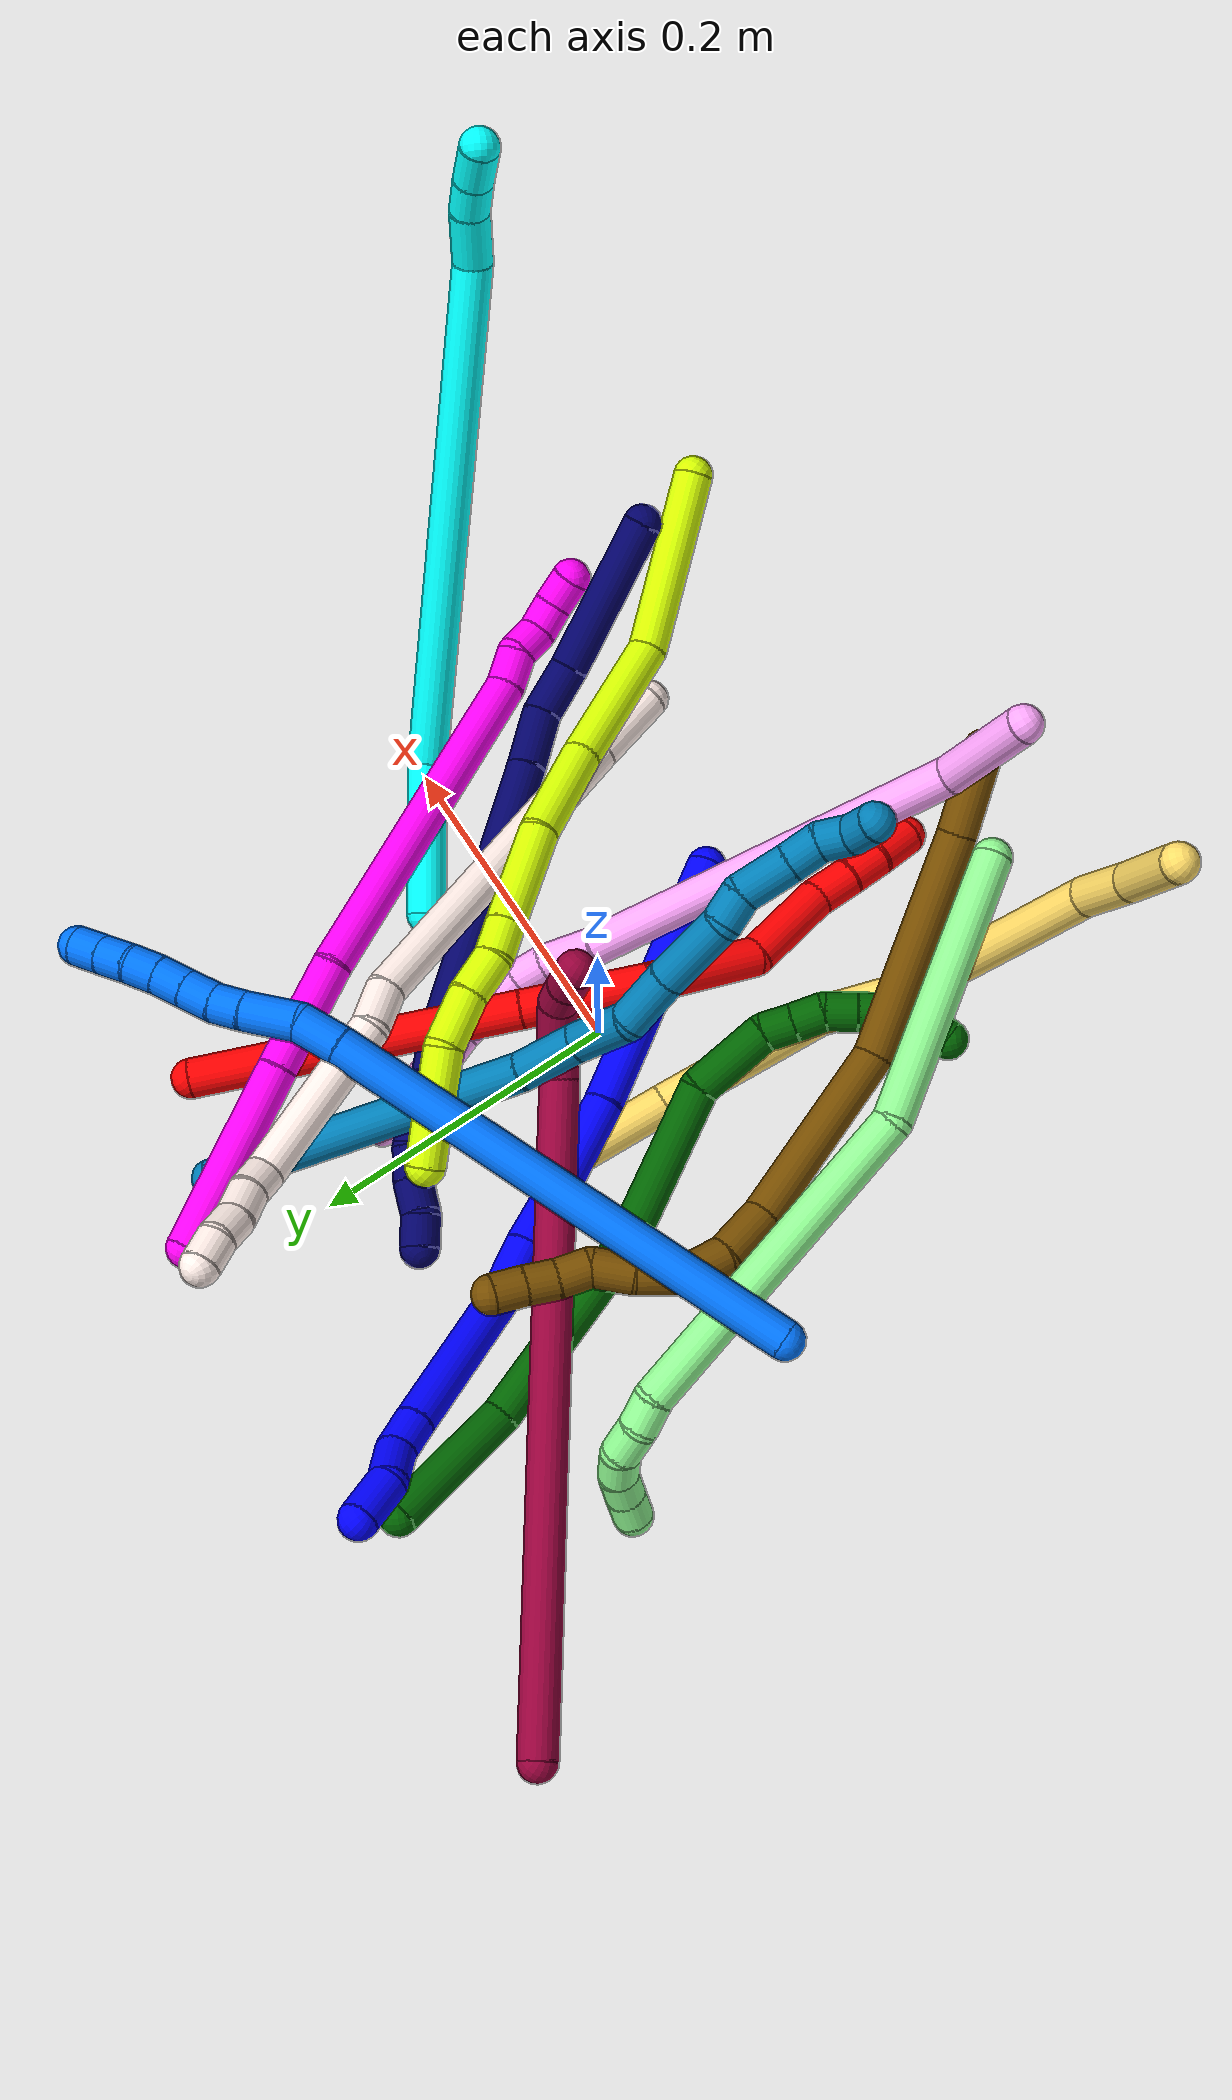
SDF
<sdf version="1.7">
 <world name="default">
  <plugin name="TubeGeneratorPlugin" filename="libtube_generator_plugin.so"/>
  <model name="photoneo_s_sensor">
   <static>1</static>
   <pose>0 0 2 1.57079 1.57079 3.14159</pose>
   <link name="link">
    <inertial><mass>0.1</mass></inertial>
    <sensor name="sensor" type="depth">
     <update_rate>30</update_rate>
     <camera>
      <horizontal_fov>1.22</horizontal_fov>
      <image><width>1920</width><height>1200</height><format>B8G8R8</format></image>
      <clip><near>0.1</near><far>4</far></clip>
      <depth_camera><output>points</output></depth_camera>
     </camera>
     <plugin name="camera_plugin" filename="libgazebo_ros_depth_camera.so">
      <baseline>0.2</baseline>
      <alwaysOn>1</alwaysOn>
      <updateRate>0.0</updateRate>
      <cameraName>camera_ir</cameraName>
      <imageTopicName>/camera/color/image_raw</imageTopicName>
      <cameraInfoTopicName>/camera/color/camera_info</cameraInfoTopicName>
      <depthImageTopicName>/camera/depth/image_raw</depthImageTopicName>
      <depthImageCameraInfoTopicName>/camera/depth/camera_info</depthImageCameraInfoTopicName>
      <pointCloudTopicName>/camera/depth/points</pointCloudTopicName>
      <frameName>fr_optical</frameName>
      <pointCloudCutoff>0.1</pointCloudCutoff>
      <pointCloudCutoffMax>2.0</pointCloudCutoffMax>
      <distortionK1>0</distortionK1>
      <distortionK2>0</distortionK2>
      <distortionK3>0</distortionK3>
      <distortionT1>0</distortionT1>
      <distortionT2>0</distortionT2>
      <CxPrime>0</CxPrime>
      <Cx>0</Cx>
      <Cy>0</Cy>
      <focalLength>0</focalLength>
      <hackBaseline>0</hackBaseline>
     </plugin>
    </sensor>
   </link>
  </model>
  <gravity>0 0 -9.8</gravity>
  <magnetic_field>6e-06 2.3e-05 -4.2e-05</magnetic_field>
  <atmosphere type="adiabatic"/>
  <physics name="default_physics" default="0" type="ode">
   <max_step_size>0.003</max_step_size>
   <real_time_factor>1</real_time_factor>
   <real_time_update_rate>1000</real_time_update_rate>
   <max_contacts>10000</max_contacts>
   <ode>
    <solver>
     <type>quick</type>
     <iters>100</iters>
     <sor>1.3</sor>
     <use_dynamic_moi_rescaling>0</use_dynamic_moi_rescaling>
    </solver>
    <constraints>
     <contact_max_correcting_vel>0</contact_max_correcting_vel>
     <contact_surface_layer>0.001</contact_surface_layer>
     <cfm>0</cfm>
     <erp>0.2</erp>
    </constraints>
   </ode>
  </physics>
  <scene><ambient>0.4 0.4 0.4 1</ambient><background>0.7 0.7 0.7 1</background><shadows>0</shadows></scene>
  <audio><device>default</device></audio>
  <spherical_coordinates>
   <surface_model>EARTH_WGS84</surface_model>
   <latitude_deg>0</latitude_deg>
   <longitude_deg>0</longitude_deg>
   <elevation>0</elevation>
   <heading_deg>0</heading_deg>
  </spherical_coordinates>
  <model name="bin">
   <static>1</static>
   <link name="bottom">
    <collision name="collision-bottom">
     <pose>0 0 -0.01 0 -0 0</pose>
     <geometry><box><size>0.8 0.6 0.02</size></box></geometry>
     <surface>
      <friction><ode><mu>100</mu><mu2>100</mu2></ode></friction>
      <contact><collide_bitmask>65535</collide_bitmask></contact>
     </surface>
    </collision>
   </link>
   <link name="west_wall">
    <collision name="collision-west_wall">
     <pose>-0.41 0 0.1 0 -0 0</pose>
     <geometry><box><size>0.02 0.6 0.2</size></box></geometry>
     <surface>
      <friction><ode><mu>100</mu><mu2>100</mu2></ode></friction>
      <contact><collide_bitmask>65535</collide_bitmask></contact>
     </surface>
    </collision>
   </link>
   <link name="east_wall">
    <collision name="collision-east_wall">
     <pose>0.41 0 0.1 0 -0 0</pose>
     <geometry><box><size>0.02 0.6 0.2</size></box></geometry>
     <surface>
      <friction><ode><mu>100</mu><mu2>100</mu2></ode></friction>
      <contact><collide_bitmask>65535</collide_bitmask></contact>
     </surface>
    </collision>
   </link>
   <link name="south_wall">
    <collision name="collision-south_wall">
     <pose>0 -0.31 0.1 0 -0 0</pose>
     <geometry><box><size>0.8 0.02 0.2</size></box></geometry>
     <surface>
      <friction><ode><mu>100</mu><mu2>100</mu2></ode></friction>
      <contact><collide_bitmask>65535</collide_bitmask></contact>
     </surface>
    </collision>
   </link>
   <link name="north_wall">
    <collision name="collision-north_wall">
     <pose>0 0.31 0.1 0 -0 0</pose>
     <geometry><box><size>0.8 0.02 0.2</size></box></geometry>
     <surface>
      <friction><ode><mu>100</mu><mu2>100</mu2></ode></friction>
      <contact><collide_bitmask>65535</collide_bitmask></contact>
     </surface>
    </collision>
   </link>
  </model>
  <model name="1">
   <static>0</static>
   <link name="1">
    <collision name="collision-cylinder-e_1_1_4">
     <pose>-0.017314 0.068207 0.05084 -0.930255 -0.200786 0.101019</pose>
     <geometry><cylinder><radius>0.0125</radius><length>0.173628</length></cylinder></geometry>
     <surface>
      <friction><ode><mu>1.16</mu><mu2>1.16</mu2><slip1>0</slip1><slip2>0</slip2></ode></friction>
      <contact><ode><kp>1e+06</kp><kd>1</kd><max_vel>0</max_vel><min_depth>0.001</min_depth></ode></contact>
     </surface>
    </collision>
    <visual name="visual-cylinder-e_1_1_4">
     <pose>-0.017314 0.068207 0.05084 -0.930255 -0.200786 0.101019</pose>
     <geometry><cylinder><radius>0.0125</radius><length>0.173628</length></cylinder></geometry>
     <material><ambient>0 0 1 1</ambient></material>
    </visual>
    <collision name="collision-cylinder-e_2_4_5">
     <pose>-0.041291 0.157869 0.120547 -0.849537 -0.229104 0.103987</pose>
     <geometry><cylinder><radius>0.0125</radius><length>0.058674</length></cylinder></geometry>
     <surface>
      <friction><ode><mu>1.16</mu><mu2>1.16</mu2><slip1>0</slip1><slip2>0</slip2></ode></friction>
      <contact><ode><kp>1e+06</kp><kd>1</kd><max_vel>0</max_vel><min_depth>0.001</min_depth></ode></contact>
     </surface>
    </collision>
    <visual name="visual-cylinder-e_2_4_5">
     <pose>-0.041291 0.157869 0.120547 -0.849537 -0.229104 0.103987</pose>
     <geometry><cylinder><radius>0.0125</radius><length>0.058674</length></cylinder></geometry>
     <material><ambient>0 0 1 1</ambient></material>
    </visual>
    <collision name="collision-cylinder-e_3_5_6">
     <pose>-0.054452 0.195398 0.153132 -0.864239 -0.298334 0.138396</pose>
     <geometry><cylinder><radius>0.0125</radius><length>0.044217</length></cylinder></geometry>
     <surface>
      <friction><ode><mu>1.16</mu><mu2>1.16</mu2><slip1>0</slip1><slip2>0</slip2></ode></friction>
      <contact><ode><kp>1e+06</kp><kd>1</kd><max_vel>0</max_vel><min_depth>0.001</min_depth></ode></contact>
     </surface>
    </collision>
    <visual name="visual-cylinder-e_3_5_6">
     <pose>-0.054452 0.195398 0.153132 -0.864239 -0.298334 0.138396</pose>
     <geometry><cylinder><radius>0.0125</radius><length>0.044217</length></cylinder></geometry>
     <material><ambient>0 0 1 1</ambient></material>
    </visual>
    <collision name="collision-cylinder-e_4_6_7">
     <pose>-0.065413 0.225719 0.177469 -0.930389 -0.246058 0.123973</pose>
     <geometry><cylinder><radius>0.0125</radius><length>0.036641</length></cylinder></geometry>
     <surface>
      <friction><ode><mu>1.16</mu><mu2>1.16</mu2><slip1>0</slip1><slip2>0</slip2></ode></friction>
      <contact><ode><kp>1e+06</kp><kd>1</kd><max_vel>0</max_vel><min_depth>0.001</min_depth></ode></contact>
     </surface>
    </collision>
    <visual name="visual-cylinder-e_4_6_7">
     <pose>-0.065413 0.225719 0.177469 -0.930389 -0.246058 0.123973</pose>
     <geometry><cylinder><radius>0.0125</radius><length>0.036641</length></cylinder></geometry>
     <material><ambient>0 0 1 1</ambient></material>
    </visual>
    <collision name="collision-cylinder-e_5_7_8">
     <pose>-0.095527 0.281477 0.208779 -1.10834 -0.505182 0.316783</pose>
     <geometry><cylinder><radius>0.0125</radius><length>0.106005</length></cylinder></geometry>
     <surface>
      <friction><ode><mu>1.16</mu><mu2>1.16</mu2><slip1>0</slip1><slip2>0</slip2></ode></friction>
      <contact><ode><kp>1e+06</kp><kd>1</kd><max_vel>0</max_vel><min_depth>0.001</min_depth></ode></contact>
     </surface>
    </collision>
    <visual name="visual-cylinder-e_5_7_8">
     <pose>-0.095527 0.281477 0.208779 -1.10834 -0.505182 0.316783</pose>
     <geometry><cylinder><radius>0.0125</radius><length>0.106005</length></cylinder></geometry>
     <material><ambient>0 0 1 1</ambient></material>
    </visual>
    <collision name="collision-cylinder-e_6_8_9">
     <pose>-0.126527 0.33211 0.234056 -1.10526 -0.482513 0.301192</pose>
     <geometry><cylinder><radius>0.0125</radius><length>0.023054</length></cylinder></geometry>
     <surface>
      <friction><ode><mu>1.16</mu><mu2>1.16</mu2><slip1>0</slip1><slip2>0</slip2></ode></friction>
      <contact><ode><kp>1e+06</kp><kd>1</kd><max_vel>0</max_vel><min_depth>0.001</min_depth></ode></contact>
     </surface>
    </collision>
    <visual name="visual-cylinder-e_6_8_9">
     <pose>-0.126527 0.33211 0.234056 -1.10526 -0.482513 0.301192</pose>
     <geometry><cylinder><radius>0.0125</radius><length>0.023054</length></cylinder></geometry>
     <material><ambient>0 0 1 1</ambient></material>
    </visual>
    <collision name="collision-cylinder-e_7_9_10">
     <pose>-0.137068 0.353756 0.239118 -1.53256 -0.39286 0.378475</pose>
     <geometry><cylinder><radius>0.0125</radius><length>0.027128</length></cylinder></geometry>
     <surface>
      <friction><ode><mu>1.16</mu><mu2>1.16</mu2><slip1>0</slip1><slip2>0</slip2></ode></friction>
      <contact><ode><kp>1e+06</kp><kd>1</kd><max_vel>0</max_vel><min_depth>0.001</min_depth></ode></contact>
     </surface>
    </collision>
    <visual name="visual-cylinder-e_7_9_10">
     <pose>-0.137068 0.353756 0.239118 -1.53256 -0.39286 0.378475</pose>
     <geometry><cylinder><radius>0.0125</radius><length>0.027128</length></cylinder></geometry>
     <material><ambient>0 0 1 1</ambient></material>
    </visual>
    <collision name="collision-cylinder-e_8_10_2">
     <pose>-0.15017 0.377737 0.246002 -1.06116 -0.542239 0.323315</pose>
     <geometry><cylinder><radius>0.0125</radius><length>0.030653</length></cylinder></geometry>
     <surface>
      <friction><ode><mu>1.16</mu><mu2>1.16</mu2><slip1>0</slip1><slip2>0</slip2></ode></friction>
      <contact><ode><kp>1e+06</kp><kd>1</kd><max_vel>0</max_vel><min_depth>0.001</min_depth></ode></contact>
     </surface>
    </collision>
    <visual name="visual-cylinder-e_8_10_2">
     <pose>-0.15017 0.377737 0.246002 -1.06116 -0.542239 0.323315</pose>
     <geometry><cylinder><radius>0.0125</radius><length>0.030653</length></cylinder></geometry>
     <material><ambient>0 0 1 1</ambient></material>
    </visual>
    <collision name="collision-sphere-2">
     <pose>-0.158079 0.389197 0.252406 0 -0 0</pose>
     <geometry><sphere><radius>0.0125</radius></sphere></geometry>
     <surface>
      <friction><ode><mu>1.16</mu><mu2>1.16</mu2><slip1>0</slip1><slip2>0</slip2></ode></friction>
      <contact><ode><kp>1e+06</kp><kd>1</kd><max_vel>0</max_vel><min_depth>0.001</min_depth></ode></contact>
     </surface>
    </collision>
    <visual name="visual-sphere-2">
     <pose>-0.158079 0.389197 0.252406 0 -0 0</pose>
     <geometry><sphere><radius>0.0125</radius></sphere></geometry>
     <material><ambient>0 0 1 1</ambient></material>
    </visual>
    <collision name="collision-sphere-10">
     <pose>-0.142261 0.366278 0.239597 0 -0 0</pose>
     <geometry><sphere><radius>0.0125</radius></sphere></geometry>
     <surface>
      <friction><ode><mu>1.16</mu><mu2>1.16</mu2><slip1>0</slip1><slip2>0</slip2></ode></friction>
      <contact><ode><kp>1e+06</kp><kd>1</kd><max_vel>0</max_vel><min_depth>0.001</min_depth></ode></contact>
     </surface>
    </collision>
    <visual name="visual-sphere-10">
     <pose>-0.142261 0.366278 0.239597 0 -0 0</pose>
     <geometry><sphere><radius>0.0125</radius></sphere></geometry>
     <material><ambient>0 0 1 1</ambient></material>
    </visual>
    <collision name="collision-sphere-9">
     <pose>-0.131875 0.341235 0.238639 0 -0 0</pose>
     <geometry><sphere><radius>0.0125</radius></sphere></geometry>
     <surface>
      <friction><ode><mu>1.16</mu><mu2>1.16</mu2><slip1>0</slip1><slip2>0</slip2></ode></friction>
      <contact><ode><kp>1e+06</kp><kd>1</kd><max_vel>0</max_vel><min_depth>0.001</min_depth></ode></contact>
     </surface>
    </collision>
    <visual name="visual-sphere-9">
     <pose>-0.131875 0.341235 0.238639 0 -0 0</pose>
     <geometry><sphere><radius>0.0125</radius></sphere></geometry>
     <material><ambient>0 0 1 1</ambient></material>
    </visual>
    <collision name="collision-sphere-4">
     <pose>-0.034628 0.136413 0.101681 0 -0 0</pose>
     <geometry><sphere><radius>0.0125</radius></sphere></geometry>
     <surface>
      <friction><ode><mu>1.16</mu><mu2>1.16</mu2><slip1>0</slip1><slip2>0</slip2></ode></friction>
      <contact><ode><kp>1e+06</kp><kd>1</kd><max_vel>0</max_vel><min_depth>0.001</min_depth></ode></contact>
     </surface>
    </collision>
    <visual name="visual-sphere-4">
     <pose>-0.034628 0.136413 0.101681 0 -0 0</pose>
     <geometry><sphere><radius>0.0125</radius></sphere></geometry>
     <material><ambient>0 0 1 1</ambient></material>
    </visual>
    <collision name="collision-sphere-1">
     <geometry><sphere><radius>0.0125</radius></sphere></geometry>
     <surface>
      <friction><ode><mu>1.16</mu><mu2>1.16</mu2><slip1>0</slip1><slip2>0</slip2></ode></friction>
      <contact><ode><kp>1e+06</kp><kd>1</kd><max_vel>0</max_vel><min_depth>0.001</min_depth></ode></contact>
     </surface>
    </collision>
    <visual name="visual-sphere-1">
     <geometry><sphere><radius>0.0125</radius></sphere></geometry>
     <material><ambient>0 0 1 1</ambient></material>
    </visual>
    <collision name="collision-sphere-8">
     <pose>-0.121178 0.322986 0.229472 0 -0 0</pose>
     <geometry><sphere><radius>0.0125</radius></sphere></geometry>
     <surface>
      <friction><ode><mu>1.16</mu><mu2>1.16</mu2><slip1>0</slip1><slip2>0</slip2></ode></friction>
      <contact><ode><kp>1e+06</kp><kd>1</kd><max_vel>0</max_vel><min_depth>0.001</min_depth></ode></contact>
     </surface>
    </collision>
    <visual name="visual-sphere-8">
     <pose>-0.121178 0.322986 0.229472 0 -0 0</pose>
     <geometry><sphere><radius>0.0125</radius></sphere></geometry>
     <material><ambient>0 0 1 1</ambient></material>
    </visual>
    <collision name="collision-sphere-5">
     <pose>-0.047954 0.179325 0.139413 0 -0 0</pose>
     <geometry><sphere><radius>0.0125</radius></sphere></geometry>
     <surface>
      <friction><ode><mu>1.16</mu><mu2>1.16</mu2><slip1>0</slip1><slip2>0</slip2></ode></friction>
      <contact><ode><kp>1e+06</kp><kd>1</kd><max_vel>0</max_vel><min_depth>0.001</min_depth></ode></contact>
     </surface>
    </collision>
    <visual name="visual-sphere-5">
     <pose>-0.047954 0.179325 0.139413 0 -0 0</pose>
     <geometry><sphere><radius>0.0125</radius></sphere></geometry>
     <material><ambient>0 0 1 1</ambient></material>
    </visual>
    <collision name="collision-sphere-6">
     <pose>-0.06095 0.211471 0.166851 0 -0 0</pose>
     <geometry><sphere><radius>0.0125</radius></sphere></geometry>
     <surface>
      <friction><ode><mu>1.16</mu><mu2>1.16</mu2><slip1>0</slip1><slip2>0</slip2></ode></friction>
      <contact><ode><kp>1e+06</kp><kd>1</kd><max_vel>0</max_vel><min_depth>0.001</min_depth></ode></contact>
     </surface>
    </collision>
    <visual name="visual-sphere-6">
     <pose>-0.06095 0.211471 0.166851 0 -0 0</pose>
     <geometry><sphere><radius>0.0125</radius></sphere></geometry>
     <material><ambient>0 0 1 1</ambient></material>
    </visual>
    <collision name="collision-sphere-7">
     <pose>-0.069875 0.239967 0.188086 0 -0 0</pose>
     <geometry><sphere><radius>0.0125</radius></sphere></geometry>
     <surface>
      <friction><ode><mu>1.16</mu><mu2>1.16</mu2><slip1>0</slip1><slip2>0</slip2></ode></friction>
      <contact><ode><kp>1e+06</kp><kd>1</kd><max_vel>0</max_vel><min_depth>0.001</min_depth></ode></contact>
     </surface>
    </collision>
    <visual name="visual-sphere-7">
     <pose>-0.069875 0.239967 0.188086 0 -0 0</pose>
     <geometry><sphere><radius>0.0125</radius></sphere></geometry>
     <material><ambient>0 0 1 1</ambient></material>
    </visual>
    <inertial>
     <pose>-0.063196 0.193371 0.141458 0 -0 0</pose>
     <mass>0.5</mass>
     <inertia>
      <ixx>0.000623</ixx>
      <ixy>0</ixy>
      <ixz>0</ixz>
      <iyy>0.000463</iyy>
      <iyz>0</iyz>
      <izz>-0.00029</izz>
     </inertia>
    </inertial>
   </link>
   <pose>0.050509 -0.115081 0.011494 2.46132 0.714027 -2.41729</pose>
  </model>
  <model name="2">
   <static>0</static>
   <link name="2">
    <collision name="collision-cylinder-e_1_1_4">
     <pose>0.015742 -0.087535 0.054325 1.01536 0.151625 0.084464</pose>
     <geometry><cylinder><radius>0.0125</radius><length>0.208435</length></cylinder></geometry>
     <surface>
      <friction><ode><mu>1.16</mu><mu2>1.16</mu2><slip1>0</slip1><slip2>0</slip2></ode></friction>
      <contact><ode><kp>1e+06</kp><kd>1</kd><max_vel>0</max_vel><min_depth>0.001</min_depth></ode></contact>
     </surface>
    </collision>
    <visual name="visual-cylinder-e_1_1_4">
     <pose>0.015742 -0.087535 0.054325 1.01536 0.151625 0.084464</pose>
     <geometry><cylinder><radius>0.0125</radius><length>0.208435</length></cylinder></geometry>
     <material><ambient>1 0 0 1</ambient></material>
    </visual>
    <collision name="collision-cylinder-e_2_4_5">
     <pose>0.03666 -0.208575 0.130108 1.00117 0.129396 0.070857</pose>
     <geometry><cylinder><radius>0.0125</radius><length>0.080248</length></cylinder></geometry>
     <surface>
      <friction><ode><mu>1.16</mu><mu2>1.16</mu2><slip1>0</slip1><slip2>0</slip2></ode></friction>
      <contact><ode><kp>1e+06</kp><kd>1</kd><max_vel>0</max_vel><min_depth>0.001</min_depth></ode></contact>
     </surface>
    </collision>
    <visual name="visual-cylinder-e_2_4_5">
     <pose>0.03666 -0.208575 0.130108 1.00117 0.129396 0.070857</pose>
     <geometry><cylinder><radius>0.0125</radius><length>0.080248</length></cylinder></geometry>
     <material><ambient>1 0 0 1</ambient></material>
    </visual>
    <collision name="collision-cylinder-e_3_5_6">
     <pose>0.032742 -0.266577 0.177069 0.76525 -0.251779 -0.101781</pose>
     <geometry><cylinder><radius>0.0125</radius><length>0.073024</length></cylinder></geometry>
     <surface>
      <friction><ode><mu>1.16</mu><mu2>1.16</mu2><slip1>0</slip1><slip2>0</slip2></ode></friction>
      <contact><ode><kp>1e+06</kp><kd>1</kd><max_vel>0</max_vel><min_depth>0.001</min_depth></ode></contact>
     </surface>
    </collision>
    <visual name="visual-cylinder-e_3_5_6">
     <pose>0.032742 -0.266577 0.177069 0.76525 -0.251779 -0.101781</pose>
     <geometry><cylinder><radius>0.0125</radius><length>0.073024</length></cylinder></geometry>
     <material><ambient>1 0 0 1</ambient></material>
    </visual>
    <collision name="collision-cylinder-e_4_6_7">
     <pose>0.005946 -0.312896 0.21393 1.09092 -0.623635 -0.386353</pose>
     <geometry><cylinder><radius>0.0125</radius><length>0.060616</length></cylinder></geometry>
     <surface>
      <friction><ode><mu>1.16</mu><mu2>1.16</mu2><slip1>0</slip1><slip2>0</slip2></ode></friction>
      <contact><ode><kp>1e+06</kp><kd>1</kd><max_vel>0</max_vel><min_depth>0.001</min_depth></ode></contact>
     </surface>
    </collision>
    <visual name="visual-cylinder-e_4_6_7">
     <pose>0.005946 -0.312896 0.21393 1.09092 -0.623635 -0.386353</pose>
     <geometry><cylinder><radius>0.0125</radius><length>0.060616</length></cylinder></geometry>
     <material><ambient>1 0 0 1</ambient></material>
    </visual>
    <collision name="collision-cylinder-e_5_7_8">
     <pose>-0.016305 -0.345389 0.230735 1.0988 -0.363103 -0.223857</pose>
     <geometry><cylinder><radius>0.0125</radius><length>0.025628</length></cylinder></geometry>
     <surface>
      <friction><ode><mu>1.16</mu><mu2>1.16</mu2><slip1>0</slip1><slip2>0</slip2></ode></friction>
      <contact><ode><kp>1e+06</kp><kd>1</kd><max_vel>0</max_vel><min_depth>0.001</min_depth></ode></contact>
     </surface>
    </collision>
    <visual name="visual-cylinder-e_5_7_8">
     <pose>-0.016305 -0.345389 0.230735 1.0988 -0.363103 -0.223857</pose>
     <geometry><cylinder><radius>0.0125</radius><length>0.025628</length></cylinder></geometry>
     <material><ambient>1 0 0 1</ambient></material>
    </visual>
    <collision name="collision-cylinder-e_6_8_9">
     <pose>-0.02593 -0.365451 0.241499 1.05568 -0.439422 -0.25894</pose>
     <geometry><cylinder><radius>0.0125</radius><length>0.023854</length></cylinder></geometry>
     <surface>
      <friction><ode><mu>1.16</mu><mu2>1.16</mu2><slip1>0</slip1><slip2>0</slip2></ode></friction>
      <contact><ode><kp>1e+06</kp><kd>1</kd><max_vel>0</max_vel><min_depth>0.001</min_depth></ode></contact>
     </surface>
    </collision>
    <visual name="visual-cylinder-e_6_8_9">
     <pose>-0.02593 -0.365451 0.241499 1.05568 -0.439422 -0.25894</pose>
     <geometry><cylinder><radius>0.0125</radius><length>0.023854</length></cylinder></geometry>
     <material><ambient>1 0 0 1</ambient></material>
    </visual>
    <collision name="collision-cylinder-e_7_9_2">
     <pose>-0.038757 -0.384471 0.253595 0.957275 -0.582341 -0.308533</pose>
     <geometry><cylinder><radius>0.0125</radius><length>0.028194</length></cylinder></geometry>
     <surface>
      <friction><ode><mu>1.16</mu><mu2>1.16</mu2><slip1>0</slip1><slip2>0</slip2></ode></friction>
      <contact><ode><kp>1e+06</kp><kd>1</kd><max_vel>0</max_vel><min_depth>0.001</min_depth></ode></contact>
     </surface>
    </collision>
    <visual name="visual-cylinder-e_7_9_2">
     <pose>-0.038757 -0.384471 0.253595 0.957275 -0.582341 -0.308533</pose>
     <geometry><cylinder><radius>0.0125</radius><length>0.028194</length></cylinder></geometry>
     <material><ambient>1 0 0 1</ambient></material>
    </visual>
    <collision name="collision-sphere-2">
     <pose>-0.04651 -0.394097 0.260373 0 -0 0</pose>
     <geometry><sphere><radius>0.0125</radius></sphere></geometry>
     <surface>
      <friction><ode><mu>1.16</mu><mu2>1.16</mu2><slip1>0</slip1><slip2>0</slip2></ode></friction>
      <contact><ode><kp>1e+06</kp><kd>1</kd><max_vel>0</max_vel><min_depth>0.001</min_depth></ode></contact>
     </surface>
    </collision>
    <visual name="visual-sphere-2">
     <pose>-0.04651 -0.394097 0.260373 0 -0 0</pose>
     <geometry><sphere><radius>0.0125</radius></sphere></geometry>
     <material><ambient>1 0 0 1</ambient></material>
    </visual>
    <collision name="collision-sphere-9">
     <pose>-0.031004 -0.374845 0.246816 0 -0 0</pose>
     <geometry><sphere><radius>0.0125</radius></sphere></geometry>
     <surface>
      <friction><ode><mu>1.16</mu><mu2>1.16</mu2><slip1>0</slip1><slip2>0</slip2></ode></friction>
      <contact><ode><kp>1e+06</kp><kd>1</kd><max_vel>0</max_vel><min_depth>0.001</min_depth></ode></contact>
     </surface>
    </collision>
    <visual name="visual-sphere-9">
     <pose>-0.031004 -0.374845 0.246816 0 -0 0</pose>
     <geometry><sphere><radius>0.0125</radius></sphere></geometry>
     <material><ambient>1 0 0 1</ambient></material>
    </visual>
    <collision name="collision-sphere-4">
     <pose>0.031483 -0.175069 0.108649 0 -0 0</pose>
     <geometry><sphere><radius>0.0125</radius></sphere></geometry>
     <surface>
      <friction><ode><mu>1.16</mu><mu2>1.16</mu2><slip1>0</slip1><slip2>0</slip2></ode></friction>
      <contact><ode><kp>1e+06</kp><kd>1</kd><max_vel>0</max_vel><min_depth>0.001</min_depth></ode></contact>
     </surface>
    </collision>
    <visual name="visual-sphere-4">
     <pose>0.031483 -0.175069 0.108649 0 -0 0</pose>
     <geometry><sphere><radius>0.0125</radius></sphere></geometry>
     <material><ambient>1 0 0 1</ambient></material>
    </visual>
    <collision name="collision-sphere-1">
     <geometry><sphere><radius>0.0125</radius></sphere></geometry>
     <surface>
      <friction><ode><mu>1.16</mu><mu2>1.16</mu2><slip1>0</slip1><slip2>0</slip2></ode></friction>
      <contact><ode><kp>1e+06</kp><kd>1</kd><max_vel>0</max_vel><min_depth>0.001</min_depth></ode></contact>
     </surface>
    </collision>
    <visual name="visual-sphere-1">
     <geometry><sphere><radius>0.0125</radius></sphere></geometry>
     <material><ambient>1 0 0 1</ambient></material>
    </visual>
    <collision name="collision-sphere-8">
     <pose>-0.020856 -0.356058 0.236181 0 -0 0</pose>
     <geometry><sphere><radius>0.0125</radius></sphere></geometry>
     <surface>
      <friction><ode><mu>1.16</mu><mu2>1.16</mu2><slip1>0</slip1><slip2>0</slip2></ode></friction>
      <contact><ode><kp>1e+06</kp><kd>1</kd><max_vel>0</max_vel><min_depth>0.001</min_depth></ode></contact>
     </surface>
    </collision>
    <visual name="visual-sphere-8">
     <pose>-0.020856 -0.356058 0.236181 0 -0 0</pose>
     <geometry><sphere><radius>0.0125</radius></sphere></geometry>
     <material><ambient>1 0 0 1</ambient></material>
    </visual>
    <collision name="collision-sphere-5">
     <pose>0.041838 -0.242082 0.151566 0 -0 0</pose>
     <geometry><sphere><radius>0.0125</radius></sphere></geometry>
     <surface>
      <friction><ode><mu>1.16</mu><mu2>1.16</mu2><slip1>0</slip1><slip2>0</slip2></ode></friction>
      <contact><ode><kp>1e+06</kp><kd>1</kd><max_vel>0</max_vel><min_depth>0.001</min_depth></ode></contact>
     </surface>
    </collision>
    <visual name="visual-sphere-5">
     <pose>0.041838 -0.242082 0.151566 0 -0 0</pose>
     <geometry><sphere><radius>0.0125</radius></sphere></geometry>
     <material><ambient>1 0 0 1</ambient></material>
    </visual>
    <collision name="collision-sphere-6">
     <pose>0.023646 -0.291072 0.202572 0 -0 0</pose>
     <geometry><sphere><radius>0.0125</radius></sphere></geometry>
     <surface>
      <friction><ode><mu>1.16</mu><mu2>1.16</mu2><slip1>0</slip1><slip2>0</slip2></ode></friction>
      <contact><ode><kp>1e+06</kp><kd>1</kd><max_vel>0</max_vel><min_depth>0.001</min_depth></ode></contact>
     </surface>
    </collision>
    <visual name="visual-sphere-6">
     <pose>0.023646 -0.291072 0.202572 0 -0 0</pose>
     <geometry><sphere><radius>0.0125</radius></sphere></geometry>
     <material><ambient>1 0 0 1</ambient></material>
    </visual>
    <collision name="collision-sphere-7">
     <pose>-0.011754 -0.33472 0.225289 0 -0 0</pose>
     <geometry><sphere><radius>0.0125</radius></sphere></geometry>
     <surface>
      <friction><ode><mu>1.16</mu><mu2>1.16</mu2><slip1>0</slip1><slip2>0</slip2></ode></friction>
      <contact><ode><kp>1e+06</kp><kd>1</kd><max_vel>0</max_vel><min_depth>0.001</min_depth></ode></contact>
     </surface>
    </collision>
    <visual name="visual-sphere-7">
     <pose>-0.011754 -0.33472 0.225289 0 -0 0</pose>
     <geometry><sphere><radius>0.0125</radius></sphere></geometry>
     <material><ambient>1 0 0 1</ambient></material>
    </visual>
    <inertial>
     <pose>0.01369 -0.203651 0.132972 0 -0 0</pose>
     <mass>0.5</mass>
     <inertia>
      <ixx>0.000905</ixx>
      <ixy>0</ixy>
      <ixz>0</ixz>
      <iyy>0.000502</iyy>
      <iyz>0</iyz>
      <izz>0.000647</izz>
     </inertia>
    </inertial>
   </link>
   <pose>0.107021 0.229578 0.041486 -2.55559 -0.722865 2.83294</pose>
  </model>
  <model name="3">
   <static>0</static>
   <link name="3">
    <collision name="collision-cylinder-e_1_1_4">
     <pose>0.003301 0.006197 0.047684 -0.129226 0.068551 -0.004437</pose>
     <geometry><cylinder><radius>0.0125</radius><length>0.096397</length></cylinder></geometry>
     <surface>
      <friction><ode><mu>1.16</mu><mu2>1.16</mu2><slip1>0</slip1><slip2>0</slip2></ode></friction>
      <contact><ode><kp>1e+06</kp><kd>1</kd><max_vel>0</max_vel><min_depth>0.001</min_depth></ode></contact>
     </surface>
    </collision>
    <visual name="visual-cylinder-e_1_1_4">
     <pose>0.003301 0.006197 0.047684 -0.129226 0.068551 -0.004437</pose>
     <geometry><cylinder><radius>0.0125</radius><length>0.096397</length></cylinder></geometry>
     <material><ambient>0.003922 1 0.996078 1</ambient></material>
    </visual>
    <collision name="collision-cylinder-e_2_4_5">
     <pose>0.04785 -0.032996 0.242217 0.299776 0.262176 0.039817</pose>
     <geometry><cylinder><radius>0.0125</radius><length>0.318282</length></cylinder></geometry>
     <surface>
      <friction><ode><mu>1.16</mu><mu2>1.16</mu2><slip1>0</slip1><slip2>0</slip2></ode></friction>
      <contact><ode><kp>1e+06</kp><kd>1</kd><max_vel>0</max_vel><min_depth>0.001</min_depth></ode></contact>
     </surface>
    </collision>
    <visual name="visual-cylinder-e_2_4_5">
     <pose>0.04785 -0.032996 0.242217 0.299776 0.262176 0.039817</pose>
     <geometry><cylinder><radius>0.0125</radius><length>0.318282</length></cylinder></geometry>
     <material><ambient>0.003922 1 0.996078 1</ambient></material>
    </visual>
    <collision name="collision-cylinder-e_3_5_6">
     <pose>0.092583 -0.090432 0.402486 0.731482 0.190981 0.073331</pose>
     <geometry><cylinder><radius>0.0125</radius><length>0.036735</length></cylinder></geometry>
     <surface>
      <friction><ode><mu>1.16</mu><mu2>1.16</mu2><slip1>0</slip1><slip2>0</slip2></ode></friction>
      <contact><ode><kp>1e+06</kp><kd>1</kd><max_vel>0</max_vel><min_depth>0.001</min_depth></ode></contact>
     </surface>
    </collision>
    <visual name="visual-cylinder-e_3_5_6">
     <pose>0.092583 -0.090432 0.402486 0.731482 0.190981 0.073331</pose>
     <geometry><cylinder><radius>0.0125</radius><length>0.036735</length></cylinder></geometry>
     <material><ambient>0.003922 1 0.996078 1</ambient></material>
    </visual>
    <collision name="collision-cylinder-e_4_6_7">
     <pose>0.099973 -0.110124 0.423342 0.799324 0.350879 0.14947</pose>
     <geometry><cylinder><radius>0.0125</radius><length>0.022716</length></cylinder></geometry>
     <surface>
      <friction><ode><mu>1.16</mu><mu2>1.16</mu2><slip1>0</slip1><slip2>0</slip2></ode></friction>
      <contact><ode><kp>1e+06</kp><kd>1</kd><max_vel>0</max_vel><min_depth>0.001</min_depth></ode></contact>
     </surface>
    </collision>
    <visual name="visual-cylinder-e_4_6_7">
     <pose>0.099973 -0.110124 0.423342 0.799324 0.350879 0.14947</pose>
     <geometry><cylinder><radius>0.0125</radius><length>0.022716</length></cylinder></geometry>
     <material><ambient>0.003922 1 0.996078 1</ambient></material>
    </visual>
    <collision name="collision-cylinder-e_5_7_2">
     <pose>0.108945 -0.126839 0.438485 0.866414 0.402526 0.18817</pose>
     <geometry><cylinder><radius>0.0125</radius><length>0.02587</length></cylinder></geometry>
     <surface>
      <friction><ode><mu>1.16</mu><mu2>1.16</mu2><slip1>0</slip1><slip2>0</slip2></ode></friction>
      <contact><ode><kp>1e+06</kp><kd>1</kd><max_vel>0</max_vel><min_depth>0.001</min_depth></ode></contact>
     </surface>
    </collision>
    <visual name="visual-cylinder-e_5_7_2">
     <pose>0.108945 -0.126839 0.438485 0.866414 0.402526 0.18817</pose>
     <geometry><cylinder><radius>0.0125</radius><length>0.02587</length></cylinder></geometry>
     <material><ambient>0.003922 1 0.996078 1</ambient></material>
    </visual>
    <collision name="collision-sphere-2">
     <pose>0.114012 -0.135907 0.446192 0 -0 0</pose>
     <geometry><sphere><radius>0.0125</radius></sphere></geometry>
     <surface>
      <friction><ode><mu>1.16</mu><mu2>1.16</mu2><slip1>0</slip1><slip2>0</slip2></ode></friction>
      <contact><ode><kp>1e+06</kp><kd>1</kd><max_vel>0</max_vel><min_depth>0.001</min_depth></ode></contact>
     </surface>
    </collision>
    <visual name="visual-sphere-2">
     <pose>0.114012 -0.135907 0.446192 0 -0 0</pose>
     <geometry><sphere><radius>0.0125</radius></sphere></geometry>
     <material><ambient>0.003922 1 0.996078 1</ambient></material>
    </visual>
    <collision name="collision-sphere-7">
     <pose>0.103877 -0.11777 0.430778 0 -0 0</pose>
     <geometry><sphere><radius>0.0125</radius></sphere></geometry>
     <surface>
      <friction><ode><mu>1.16</mu><mu2>1.16</mu2><slip1>0</slip1><slip2>0</slip2></ode></friction>
      <contact><ode><kp>1e+06</kp><kd>1</kd><max_vel>0</max_vel><min_depth>0.001</min_depth></ode></contact>
     </surface>
    </collision>
    <visual name="visual-sphere-7">
     <pose>0.103877 -0.11777 0.430778 0 -0 0</pose>
     <geometry><sphere><radius>0.0125</radius></sphere></geometry>
     <material><ambient>0.003922 1 0.996078 1</ambient></material>
    </visual>
    <collision name="collision-sphere-6">
     <pose>0.096069 -0.102477 0.415906 0 -0 0</pose>
     <geometry><sphere><radius>0.0125</radius></sphere></geometry>
     <surface>
      <friction><ode><mu>1.16</mu><mu2>1.16</mu2><slip1>0</slip1><slip2>0</slip2></ode></friction>
      <contact><ode><kp>1e+06</kp><kd>1</kd><max_vel>0</max_vel><min_depth>0.001</min_depth></ode></contact>
     </surface>
    </collision>
    <visual name="visual-sphere-6">
     <pose>0.096069 -0.102477 0.415906 0 -0 0</pose>
     <geometry><sphere><radius>0.0125</radius></sphere></geometry>
     <material><ambient>0.003922 1 0.996078 1</ambient></material>
    </visual>
    <collision name="collision-sphere-5">
     <pose>0.089096 -0.078386 0.389066 0 -0 0</pose>
     <geometry><sphere><radius>0.0125</radius></sphere></geometry>
     <surface>
      <friction><ode><mu>1.16</mu><mu2>1.16</mu2><slip1>0</slip1><slip2>0</slip2></ode></friction>
      <contact><ode><kp>1e+06</kp><kd>1</kd><max_vel>0</max_vel><min_depth>0.001</min_depth></ode></contact>
     </surface>
    </collision>
    <visual name="visual-sphere-5">
     <pose>0.089096 -0.078386 0.389066 0 -0 0</pose>
     <geometry><sphere><radius>0.0125</radius></sphere></geometry>
     <material><ambient>0.003922 1 0.996078 1</ambient></material>
    </visual>
    <collision name="collision-sphere-1">
     <geometry><sphere><radius>0.0125</radius></sphere></geometry>
     <surface>
      <friction><ode><mu>1.16</mu><mu2>1.16</mu2><slip1>0</slip1><slip2>0</slip2></ode></friction>
      <contact><ode><kp>1e+06</kp><kd>1</kd><max_vel>0</max_vel><min_depth>0.001</min_depth></ode></contact>
     </surface>
    </collision>
    <visual name="visual-sphere-1">
     <geometry><sphere><radius>0.0125</radius></sphere></geometry>
     <material><ambient>0.003922 1 0.996078 1</ambient></material>
    </visual>
    <collision name="collision-sphere-4">
     <pose>0.006603 0.012393 0.095369 0 -0 0</pose>
     <geometry><sphere><radius>0.0125</radius></sphere></geometry>
     <surface>
      <friction><ode><mu>1.16</mu><mu2>1.16</mu2><slip1>0</slip1><slip2>0</slip2></ode></friction>
      <contact><ode><kp>1e+06</kp><kd>1</kd><max_vel>0</max_vel><min_depth>0.001</min_depth></ode></contact>
     </surface>
    </collision>
    <visual name="visual-sphere-4">
     <pose>0.006603 0.012393 0.095369 0 -0 0</pose>
     <geometry><sphere><radius>0.0125</radius></sphere></geometry>
     <material><ambient>0.003922 1 0.996078 1</ambient></material>
    </visual>
    <inertial>
     <pose>0.048077 -0.038019 0.234871 0 -0 0</pose>
     <mass>0.5</mass>
     <inertia>
      <ixx>0.002806</ixx>
      <ixy>0</ixy>
      <ixz>0</ixz>
      <iyy>0.002764</iyy>
      <iyz>0</iyz>
      <izz>9.4e-05</izz>
     </inertia>
    </inertial>
   </link>
   <pose>0.121682 0.049462 0.012382 -1.28478 -0.236133 -2.12658</pose>
  </model>
  <model name="4">
   <static>0</static>
   <link name="4">
    <collision name="collision-cylinder-e_1_1_4">
     <pose>-0.010887 -0.010721 -0.030058 2.79899 -0.328781 -1.52884</pose>
     <geometry><cylinder><radius>0.0125</radius><length>0.067436</length></cylinder></geometry>
     <surface>
      <friction><ode><mu>1.16</mu><mu2>1.16</mu2><slip1>0</slip1><slip2>0</slip2></ode></friction>
      <contact><ode><kp>1e+06</kp><kd>1</kd><max_vel>0</max_vel><min_depth>0.001</min_depth></ode></contact>
     </surface>
    </collision>
    <visual name="visual-cylinder-e_1_1_4">
     <pose>-0.010887 -0.010721 -0.030058 2.79899 -0.328781 -1.52884</pose>
     <geometry><cylinder><radius>0.0125</radius><length>0.067436</length></cylinder></geometry>
     <material><ambient>1 0.65098 0.996078 1</ambient></material>
    </visual>
    <collision name="collision-cylinder-e_2_4_5">
     <pose>-0.0119 -0.029822 -0.183662 3.07386 0.079571 1.73135</pose>
     <geometry><cylinder><radius>0.0125</radius><length>0.248449</length></cylinder></geometry>
     <surface>
      <friction><ode><mu>1.16</mu><mu2>1.16</mu2><slip1>0</slip1><slip2>0</slip2></ode></friction>
      <contact><ode><kp>1e+06</kp><kd>1</kd><max_vel>0</max_vel><min_depth>0.001</min_depth></ode></contact>
     </surface>
    </collision>
    <visual name="visual-cylinder-e_2_4_5">
     <pose>-0.0119 -0.029822 -0.183662 3.07386 0.079571 1.73135</pose>
     <geometry><cylinder><radius>0.0125</radius><length>0.248449</length></cylinder></geometry>
     <material><ambient>1 0.65098 0.996078 1</ambient></material>
    </visual>
    <collision name="collision-cylinder-e_3_5_6">
     <pose>-0.000458 -0.041844 -0.324581 2.935 0.088127 0.804312</pose>
     <geometry><cylinder><radius>0.0125</radius><length>0.035636</length></cylinder></geometry>
     <surface>
      <friction><ode><mu>1.16</mu><mu2>1.16</mu2><slip1>0</slip1><slip2>0</slip2></ode></friction>
      <contact><ode><kp>1e+06</kp><kd>1</kd><max_vel>0</max_vel><min_depth>0.001</min_depth></ode></contact>
     </surface>
    </collision>
    <visual name="visual-cylinder-e_3_5_6">
     <pose>-0.000458 -0.041844 -0.324581 2.935 0.088127 0.804312</pose>
     <geometry><cylinder><radius>0.0125</radius><length>0.035636</length></cylinder></geometry>
     <material><ambient>1 0.65098 0.996078 1</ambient></material>
    </visual>
    <collision name="collision-cylinder-e_4_6_7">
     <pose>0.002196 -0.044536 -0.352341 -3.05053 0.103728 -1.70081</pose>
     <geometry><cylinder><radius>0.0125</radius><length>0.020975</length></cylinder></geometry>
     <surface>
      <friction><ode><mu>1.16</mu><mu2>1.16</mu2><slip1>0</slip1><slip2>0</slip2></ode></friction>
      <contact><ode><kp>1e+06</kp><kd>1</kd><max_vel>0</max_vel><min_depth>0.001</min_depth></ode></contact>
     </surface>
    </collision>
    <visual name="visual-cylinder-e_4_6_7">
     <pose>0.002196 -0.044536 -0.352341 -3.05053 0.103728 -1.70081</pose>
     <geometry><cylinder><radius>0.0125</radius><length>0.020975</length></cylinder></geometry>
     <material><ambient>1 0.65098 0.996078 1</ambient></material>
    </visual>
    <collision name="collision-cylinder-e_5_7_8">
     <pose>0.003554 -0.039564 -0.374401 -2.80967 0.022036 -0.131374</pose>
     <geometry><cylinder><radius>0.0125</radius><length>0.024698</length></cylinder></geometry>
     <surface>
      <friction><ode><mu>1.16</mu><mu2>1.16</mu2><slip1>0</slip1><slip2>0</slip2></ode></friction>
      <contact><ode><kp>1e+06</kp><kd>1</kd><max_vel>0</max_vel><min_depth>0.001</min_depth></ode></contact>
     </surface>
    </collision>
    <visual name="visual-cylinder-e_5_7_8">
     <pose>0.003554 -0.039564 -0.374401 -2.80967 0.022036 -0.131374</pose>
     <geometry><cylinder><radius>0.0125</radius><length>0.024698</length></cylinder></geometry>
     <material><ambient>1 0.65098 0.996078 1</ambient></material>
    </visual>
    <collision name="collision-cylinder-e_6_8_9">
     <pose>0.00405 -0.03216 -0.396709 -2.83381 0.020064 -0.129172</pose>
     <geometry><cylinder><radius>0.0125</radius><length>0.022324</length></cylinder></geometry>
     <surface>
      <friction><ode><mu>1.16</mu><mu2>1.16</mu2><slip1>0</slip1><slip2>0</slip2></ode></friction>
      <contact><ode><kp>1e+06</kp><kd>1</kd><max_vel>0</max_vel><min_depth>0.001</min_depth></ode></contact>
     </surface>
    </collision>
    <visual name="visual-cylinder-e_6_8_9">
     <pose>0.00405 -0.03216 -0.396709 -2.83381 0.020064 -0.129172</pose>
     <geometry><cylinder><radius>0.0125</radius><length>0.022324</length></cylinder></geometry>
     <material><ambient>1 0.65098 0.996078 1</ambient></material>
    </visual>
    <collision name="collision-cylinder-e_7_9_10">
     <pose>0.004694 -0.022697 -0.415469 -2.499 0.041338 -0.12406</pose>
     <geometry><cylinder><radius>0.0125</radius><length>0.020315</length></cylinder></geometry>
     <surface>
      <friction><ode><mu>1.16</mu><mu2>1.16</mu2><slip1>0</slip1><slip2>0</slip2></ode></friction>
      <contact><ode><kp>1e+06</kp><kd>1</kd><max_vel>0</max_vel><min_depth>0.001</min_depth></ode></contact>
     </surface>
    </collision>
    <visual name="visual-cylinder-e_7_9_10">
     <pose>0.004694 -0.022697 -0.415469 -2.499 0.041338 -0.12406</pose>
     <geometry><cylinder><radius>0.0125</radius><length>0.020315</length></cylinder></geometry>
     <material><ambient>1 0.65098 0.996078 1</ambient></material>
    </visual>
    <collision name="collision-cylinder-e_8_10_11">
     <pose>0.006197 -0.01069 -0.431677 -2.50899 0.107691 -0.326427</pose>
     <geometry><cylinder><radius>0.0125</radius><length>0.020162</length></cylinder></geometry>
     <surface>
      <friction><ode><mu>1.16</mu><mu2>1.16</mu2><slip1>0</slip1><slip2>0</slip2></ode></friction>
      <contact><ode><kp>1e+06</kp><kd>1</kd><max_vel>0</max_vel><min_depth>0.001</min_depth></ode></contact>
     </surface>
    </collision>
    <visual name="visual-cylinder-e_8_10_11">
     <pose>0.006197 -0.01069 -0.431677 -2.50899 0.107691 -0.326427</pose>
     <geometry><cylinder><radius>0.0125</radius><length>0.020162</length></cylinder></geometry>
     <material><ambient>1 0.65098 0.996078 1</ambient></material>
    </visual>
    <collision name="collision-cylinder-e_9_11_12">
     <pose>0.008098 0.000969 -0.447913 -2.52875 0.081751 -0.25711</pose>
     <geometry><cylinder><radius>0.0125</radius><length>0.020001</length></cylinder></geometry>
     <surface>
      <friction><ode><mu>1.16</mu><mu2>1.16</mu2><slip1>0</slip1><slip2>0</slip2></ode></friction>
      <contact><ode><kp>1e+06</kp><kd>1</kd><max_vel>0</max_vel><min_depth>0.001</min_depth></ode></contact>
     </surface>
    </collision>
    <visual name="visual-cylinder-e_9_11_12">
     <pose>0.008098 0.000969 -0.447913 -2.52875 0.081751 -0.25711</pose>
     <geometry><cylinder><radius>0.0125</radius><length>0.020001</length></cylinder></geometry>
     <material><ambient>1 0.65098 0.996078 1</ambient></material>
    </visual>
    <collision name="collision-cylinder-e_10_12_2">
     <pose>0.012447 0.014094 -0.461804 -2.23084 0.361027 -0.713463</pose>
     <geometry><cylinder><radius>0.0125</radius><length>0.020002</length></cylinder></geometry>
     <surface>
      <friction><ode><mu>1.16</mu><mu2>1.16</mu2><slip1>0</slip1><slip2>0</slip2></ode></friction>
      <contact><ode><kp>1e+06</kp><kd>1</kd><max_vel>0</max_vel><min_depth>0.001</min_depth></ode></contact>
     </surface>
    </collision>
    <visual name="visual-cylinder-e_10_12_2">
     <pose>0.012447 0.014094 -0.461804 -2.23084 0.361027 -0.713463</pose>
     <geometry><cylinder><radius>0.0125</radius><length>0.020002</length></cylinder></geometry>
     <material><ambient>1 0.65098 0.996078 1</ambient></material>
    </visual>
    <collision name="collision-sphere-2">
     <pose>0.01598 0.021485 -0.467541 0 -0 0</pose>
     <geometry><sphere><radius>0.0125</radius></sphere></geometry>
     <surface>
      <friction><ode><mu>1.16</mu><mu2>1.16</mu2><slip1>0</slip1><slip2>0</slip2></ode></friction>
      <contact><ode><kp>1e+06</kp><kd>1</kd><max_vel>0</max_vel><min_depth>0.001</min_depth></ode></contact>
     </surface>
    </collision>
    <visual name="visual-sphere-2">
     <pose>0.01598 0.021485 -0.467541 0 -0 0</pose>
     <geometry><sphere><radius>0.0125</radius></sphere></geometry>
     <material><ambient>1 0.65098 0.996078 1</ambient></material>
    </visual>
    <collision name="collision-sphere-12">
     <pose>0.008914 0.006703 -0.456067 0 -0 0</pose>
     <geometry><sphere><radius>0.0125</radius></sphere></geometry>
     <surface>
      <friction><ode><mu>1.16</mu><mu2>1.16</mu2><slip1>0</slip1><slip2>0</slip2></ode></friction>
      <contact><ode><kp>1e+06</kp><kd>1</kd><max_vel>0</max_vel><min_depth>0.001</min_depth></ode></contact>
     </surface>
    </collision>
    <visual name="visual-sphere-12">
     <pose>0.008914 0.006703 -0.456067 0 -0 0</pose>
     <geometry><sphere><radius>0.0125</radius></sphere></geometry>
     <material><ambient>1 0.65098 0.996078 1</ambient></material>
    </visual>
    <collision name="collision-sphere-11">
     <pose>0.007281 -0.004764 -0.43976 0 -0 0</pose>
     <geometry><sphere><radius>0.0125</radius></sphere></geometry>
     <surface>
      <friction><ode><mu>1.16</mu><mu2>1.16</mu2><slip1>0</slip1><slip2>0</slip2></ode></friction>
      <contact><ode><kp>1e+06</kp><kd>1</kd><max_vel>0</max_vel><min_depth>0.001</min_depth></ode></contact>
     </surface>
    </collision>
    <visual name="visual-sphere-11">
     <pose>0.007281 -0.004764 -0.43976 0 -0 0</pose>
     <geometry><sphere><radius>0.0125</radius></sphere></geometry>
     <material><ambient>1 0.65098 0.996078 1</ambient></material>
    </visual>
    <collision name="collision-sphere-10">
     <pose>0.005114 -0.016615 -0.423594 0 -0 0</pose>
     <geometry><sphere><radius>0.0125</radius></sphere></geometry>
     <surface>
      <friction><ode><mu>1.16</mu><mu2>1.16</mu2><slip1>0</slip1><slip2>0</slip2></ode></friction>
      <contact><ode><kp>1e+06</kp><kd>1</kd><max_vel>0</max_vel><min_depth>0.001</min_depth></ode></contact>
     </surface>
    </collision>
    <visual name="visual-sphere-10">
     <pose>0.005114 -0.016615 -0.423594 0 -0 0</pose>
     <geometry><sphere><radius>0.0125</radius></sphere></geometry>
     <material><ambient>1 0.65098 0.996078 1</ambient></material>
    </visual>
    <collision name="collision-sphere-9">
     <pose>0.004274 -0.028779 -0.407344 0 -0 0</pose>
     <geometry><sphere><radius>0.0125</radius></sphere></geometry>
     <surface>
      <friction><ode><mu>1.16</mu><mu2>1.16</mu2><slip1>0</slip1><slip2>0</slip2></ode></friction>
      <contact><ode><kp>1e+06</kp><kd>1</kd><max_vel>0</max_vel><min_depth>0.001</min_depth></ode></contact>
     </surface>
    </collision>
    <visual name="visual-sphere-9">
     <pose>0.004274 -0.028779 -0.407344 0 -0 0</pose>
     <geometry><sphere><radius>0.0125</radius></sphere></geometry>
     <material><ambient>1 0.65098 0.996078 1</ambient></material>
    </visual>
    <collision name="collision-sphere-4">
     <pose>-0.021775 -0.021441 -0.060115 0 -0 0</pose>
     <geometry><sphere><radius>0.0125</radius></sphere></geometry>
     <surface>
      <friction><ode><mu>1.16</mu><mu2>1.16</mu2><slip1>0</slip1><slip2>0</slip2></ode></friction>
      <contact><ode><kp>1e+06</kp><kd>1</kd><max_vel>0</max_vel><min_depth>0.001</min_depth></ode></contact>
     </surface>
    </collision>
    <visual name="visual-sphere-4">
     <pose>-0.021775 -0.021441 -0.060115 0 -0 0</pose>
     <geometry><sphere><radius>0.0125</radius></sphere></geometry>
     <material><ambient>1 0.65098 0.996078 1</ambient></material>
    </visual>
    <collision name="collision-sphere-1">
     <geometry><sphere><radius>0.0125</radius></sphere></geometry>
     <surface>
      <friction><ode><mu>1.16</mu><mu2>1.16</mu2><slip1>0</slip1><slip2>0</slip2></ode></friction>
      <contact><ode><kp>1e+06</kp><kd>1</kd><max_vel>0</max_vel><min_depth>0.001</min_depth></ode></contact>
     </surface>
    </collision>
    <visual name="visual-sphere-1">
     <geometry><sphere><radius>0.0125</radius></sphere></geometry>
     <material><ambient>1 0.65098 0.996078 1</ambient></material>
    </visual>
    <collision name="collision-sphere-8">
     <pose>0.003827 -0.035541 -0.386074 0 -0 0</pose>
     <geometry><sphere><radius>0.0125</radius></sphere></geometry>
     <surface>
      <friction><ode><mu>1.16</mu><mu2>1.16</mu2><slip1>0</slip1><slip2>0</slip2></ode></friction>
      <contact><ode><kp>1e+06</kp><kd>1</kd><max_vel>0</max_vel><min_depth>0.001</min_depth></ode></contact>
     </surface>
    </collision>
    <visual name="visual-sphere-8">
     <pose>0.003827 -0.035541 -0.386074 0 -0 0</pose>
     <geometry><sphere><radius>0.0125</radius></sphere></geometry>
     <material><ambient>1 0.65098 0.996078 1</ambient></material>
    </visual>
    <collision name="collision-sphere-5">
     <pose>-0.002026 -0.038203 -0.30721 0 -0 0</pose>
     <geometry><sphere><radius>0.0125</radius></sphere></geometry>
     <surface>
      <friction><ode><mu>1.16</mu><mu2>1.16</mu2><slip1>0</slip1><slip2>0</slip2></ode></friction>
      <contact><ode><kp>1e+06</kp><kd>1</kd><max_vel>0</max_vel><min_depth>0.001</min_depth></ode></contact>
     </surface>
    </collision>
    <visual name="visual-sphere-5">
     <pose>-0.002026 -0.038203 -0.30721 0 -0 0</pose>
     <geometry><sphere><radius>0.0125</radius></sphere></geometry>
     <material><ambient>1 0.65098 0.996078 1</ambient></material>
    </visual>
    <collision name="collision-sphere-6">
     <pose>0.001111 -0.045484 -0.341953 0 -0 0</pose>
     <geometry><sphere><radius>0.0125</radius></sphere></geometry>
     <surface>
      <friction><ode><mu>1.16</mu><mu2>1.16</mu2><slip1>0</slip1><slip2>0</slip2></ode></friction>
      <contact><ode><kp>1e+06</kp><kd>1</kd><max_vel>0</max_vel><min_depth>0.001</min_depth></ode></contact>
     </surface>
    </collision>
    <visual name="visual-sphere-6">
     <pose>0.001111 -0.045484 -0.341953 0 -0 0</pose>
     <geometry><sphere><radius>0.0125</radius></sphere></geometry>
     <material><ambient>1 0.65098 0.996078 1</ambient></material>
    </visual>
    <collision name="collision-sphere-7">
     <pose>0.003282 -0.043587 -0.362729 0 -0 0</pose>
     <geometry><sphere><radius>0.0125</radius></sphere></geometry>
     <surface>
      <friction><ode><mu>1.16</mu><mu2>1.16</mu2><slip1>0</slip1><slip2>0</slip2></ode></friction>
      <contact><ode><kp>1e+06</kp><kd>1</kd><max_vel>0</max_vel><min_depth>0.001</min_depth></ode></contact>
     </surface>
    </collision>
    <visual name="visual-sphere-7">
     <pose>0.003282 -0.043587 -0.362729 0 -0 0</pose>
     <geometry><sphere><radius>0.0125</radius></sphere></geometry>
     <material><ambient>1 0.65098 0.996078 1</ambient></material>
    </visual>
    <inertial>
     <pose>-0.005703 -0.025256 -0.240116 0 -0 0</pose>
     <mass>0.5</mass>
     <inertia><ixx>0.00105</ixx><ixy>0</ixy><ixz>0</ixz><iyy>0.001445</iyy><iyz>0</iyz><izz>-4e-05</izz></inertia>
    </inertial>
   </link>
   <pose>-0.020077 -0.285809 0.197625 0.904412 -0.813708 0.408041</pose>
  </model>
  <model name="5">
   <static>0</static>
   <link name="5">
    <collision name="collision-cylinder-e_1_1_4">
     <pose>0.00179 -0.01063 -0.02643 2.75921 0.062744 0.321475</pose>
     <geometry><cylinder><radius>0.0125</radius><length>0.057088</length></cylinder></geometry>
     <surface>
      <friction><ode><mu>1.16</mu><mu2>1.16</mu2><slip1>0</slip1><slip2>0</slip2></ode></friction>
      <contact><ode><kp>1e+06</kp><kd>1</kd><max_vel>0</max_vel><min_depth>0.001</min_depth></ode></contact>
     </surface>
    </collision>
    <visual name="visual-cylinder-e_1_1_4">
     <pose>0.00179 -0.01063 -0.02643 2.75921 0.062744 0.321475</pose>
     <geometry><cylinder><radius>0.0125</radius><length>0.057088</length></cylinder></geometry>
     <material><ambient>1 0.858824 0.4 1</ambient></material>
    </visual>
    <collision name="collision-cylinder-e_2_4_5">
     <pose>0.006028 -0.025174 -0.073227 2.95171 0.117496 1.10655</pose>
     <geometry><cylinder><radius>0.0125</radius><length>0.041766</length></cylinder></geometry>
     <surface>
      <friction><ode><mu>1.16</mu><mu2>1.16</mu2><slip1>0</slip1><slip2>0</slip2></ode></friction>
      <contact><ode><kp>1e+06</kp><kd>1</kd><max_vel>0</max_vel><min_depth>0.001</min_depth></ode></contact>
     </surface>
    </collision>
    <visual name="visual-cylinder-e_2_4_5">
     <pose>0.006028 -0.025174 -0.073227 2.95171 0.117496 1.10655</pose>
     <geometry><cylinder><radius>0.0125</radius><length>0.041766</length></cylinder></geometry>
     <material><ambient>1 0.858824 0.4 1</ambient></material>
    </visual>
    <collision name="collision-cylinder-e_3_5_6">
     <pose>0.009022 -0.024655 -0.169612 -3.08334 0.007178 -0.24515</pose>
     <geometry><cylinder><radius>0.0125</radius><length>0.1523</length></cylinder></geometry>
     <surface>
      <friction><ode><mu>1.16</mu><mu2>1.16</mu2><slip1>0</slip1><slip2>0</slip2></ode></friction>
      <contact><ode><kp>1e+06</kp><kd>1</kd><max_vel>0</max_vel><min_depth>0.001</min_depth></ode></contact>
     </surface>
    </collision>
    <visual name="visual-cylinder-e_3_5_6">
     <pose>0.009022 -0.024655 -0.169612 -3.08334 0.007178 -0.24515</pose>
     <geometry><cylinder><radius>0.0125</radius><length>0.1523</length></cylinder></geometry>
     <material><ambient>1 0.858824 0.4 1</ambient></material>
    </visual>
    <collision name="collision-cylinder-e_4_6_7">
     <pose>0.015756 -0.007509 -0.270374 -2.66696 0.218839 -0.852672</pose>
     <geometry><cylinder><radius>0.0125</radius><length>0.056996</length></cylinder></geometry>
     <surface>
      <friction><ode><mu>1.16</mu><mu2>1.16</mu2><slip1>0</slip1><slip2>0</slip2></ode></friction>
      <contact><ode><kp>1e+06</kp><kd>1</kd><max_vel>0</max_vel><min_depth>0.001</min_depth></ode></contact>
     </surface>
    </collision>
    <visual name="visual-cylinder-e_4_6_7">
     <pose>0.015756 -0.007509 -0.270374 -2.66696 0.218839 -0.852672</pose>
     <geometry><cylinder><radius>0.0125</radius><length>0.056996</length></cylinder></geometry>
     <material><ambient>1 0.858824 0.4 1</ambient></material>
    </visual>
    <collision name="collision-cylinder-e_5_7_8">
     <pose>0.021157 0.045808 -0.333632 -2.32981 -0.014033 0.032651</pose>
     <geometry><cylinder><radius>0.0125</radius><length>0.11194</length></cylinder></geometry>
     <surface>
      <friction><ode><mu>1.16</mu><mu2>1.16</mu2><slip1>0</slip1><slip2>0</slip2></ode></friction>
      <contact><ode><kp>1e+06</kp><kd>1</kd><max_vel>0</max_vel><min_depth>0.001</min_depth></ode></contact>
     </surface>
    </collision>
    <visual name="visual-cylinder-e_5_7_8">
     <pose>0.021157 0.045808 -0.333632 -2.32981 -0.014033 0.032651</pose>
     <geometry><cylinder><radius>0.0125</radius><length>0.11194</length></cylinder></geometry>
     <material><ambient>1 0.858824 0.4 1</ambient></material>
    </visual>
    <collision name="collision-cylinder-e_6_8_2">
     <pose>0.01919 0.118492 -0.395934 -2.20879 -0.029583 0.058749</pose>
     <geometry><cylinder><radius>0.0125</radius><length>0.079911</length></cylinder></geometry>
     <surface>
      <friction><ode><mu>1.16</mu><mu2>1.16</mu2><slip1>0</slip1><slip2>0</slip2></ode></friction>
      <contact><ode><kp>1e+06</kp><kd>1</kd><max_vel>0</max_vel><min_depth>0.001</min_depth></ode></contact>
     </surface>
    </collision>
    <visual name="visual-cylinder-e_6_8_2">
     <pose>0.01919 0.118492 -0.395934 -2.20879 -0.029583 0.058749</pose>
     <geometry><cylinder><radius>0.0125</radius><length>0.079911</length></cylinder></geometry>
     <material><ambient>1 0.858824 0.4 1</ambient></material>
    </visual>
    <collision name="collision-sphere-2">
     <pose>0.018008 0.150574 -0.419721 0 -0 0</pose>
     <geometry><sphere><radius>0.0125</radius></sphere></geometry>
     <surface>
      <friction><ode><mu>1.16</mu><mu2>1.16</mu2><slip1>0</slip1><slip2>0</slip2></ode></friction>
      <contact><ode><kp>1e+06</kp><kd>1</kd><max_vel>0</max_vel><min_depth>0.001</min_depth></ode></contact>
     </surface>
    </collision>
    <visual name="visual-sphere-2">
     <pose>0.018008 0.150574 -0.419721 0 -0 0</pose>
     <geometry><sphere><radius>0.0125</radius></sphere></geometry>
     <material><ambient>1 0.858824 0.4 1</ambient></material>
    </visual>
    <collision name="collision-sphere-4">
     <pose>0.00358 -0.021259 -0.052861 0 -0 0</pose>
     <geometry><sphere><radius>0.0125</radius></sphere></geometry>
     <surface>
      <friction><ode><mu>1.16</mu><mu2>1.16</mu2><slip1>0</slip1><slip2>0</slip2></ode></friction>
      <contact><ode><kp>1e+06</kp><kd>1</kd><max_vel>0</max_vel><min_depth>0.001</min_depth></ode></contact>
     </surface>
    </collision>
    <visual name="visual-sphere-4">
     <pose>0.00358 -0.021259 -0.052861 0 -0 0</pose>
     <geometry><sphere><radius>0.0125</radius></sphere></geometry>
     <material><ambient>1 0.858824 0.4 1</ambient></material>
    </visual>
    <collision name="collision-sphere-1">
     <geometry><sphere><radius>0.0125</radius></sphere></geometry>
     <surface>
      <friction><ode><mu>1.16</mu><mu2>1.16</mu2><slip1>0</slip1><slip2>0</slip2></ode></friction>
      <contact><ode><kp>1e+06</kp><kd>1</kd><max_vel>0</max_vel><min_depth>0.001</min_depth></ode></contact>
     </surface>
    </collision>
    <visual name="visual-sphere-1">
     <geometry><sphere><radius>0.0125</radius></sphere></geometry>
     <material><ambient>1 0.858824 0.4 1</ambient></material>
    </visual>
    <collision name="collision-sphere-8">
     <pose>0.020372 0.086411 -0.372147 0 -0 0</pose>
     <geometry><sphere><radius>0.0125</radius></sphere></geometry>
     <surface>
      <friction><ode><mu>1.16</mu><mu2>1.16</mu2><slip1>0</slip1><slip2>0</slip2></ode></friction>
      <contact><ode><kp>1e+06</kp><kd>1</kd><max_vel>0</max_vel><min_depth>0.001</min_depth></ode></contact>
     </surface>
    </collision>
    <visual name="visual-sphere-8">
     <pose>0.020372 0.086411 -0.372147 0 -0 0</pose>
     <geometry><sphere><radius>0.0125</radius></sphere></geometry>
     <material><ambient>1 0.858824 0.4 1</ambient></material>
    </visual>
    <collision name="collision-sphere-5">
     <pose>0.008476 -0.029088 -0.093593 0 -0 0</pose>
     <geometry><sphere><radius>0.0125</radius></sphere></geometry>
     <surface>
      <friction><ode><mu>1.16</mu><mu2>1.16</mu2><slip1>0</slip1><slip2>0</slip2></ode></friction>
      <contact><ode><kp>1e+06</kp><kd>1</kd><max_vel>0</max_vel><min_depth>0.001</min_depth></ode></contact>
     </surface>
    </collision>
    <visual name="visual-sphere-5">
     <pose>0.008476 -0.029088 -0.093593 0 -0 0</pose>
     <geometry><sphere><radius>0.0125</radius></sphere></geometry>
     <material><ambient>1 0.858824 0.4 1</ambient></material>
    </visual>
    <collision name="collision-sphere-6">
     <pose>0.009569 -0.020222 -0.245631 0 -0 0</pose>
     <geometry><sphere><radius>0.0125</radius></sphere></geometry>
     <surface>
      <friction><ode><mu>1.16</mu><mu2>1.16</mu2><slip1>0</slip1><slip2>0</slip2></ode></friction>
      <contact><ode><kp>1e+06</kp><kd>1</kd><max_vel>0</max_vel><min_depth>0.001</min_depth></ode></contact>
     </surface>
    </collision>
    <visual name="visual-sphere-6">
     <pose>0.009569 -0.020222 -0.245631 0 -0 0</pose>
     <geometry><sphere><radius>0.0125</radius></sphere></geometry>
     <material><ambient>1 0.858824 0.4 1</ambient></material>
    </visual>
    <collision name="collision-sphere-7">
     <pose>0.021942 0.005205 -0.295117 0 -0 0</pose>
     <geometry><sphere><radius>0.0125</radius></sphere></geometry>
     <surface>
      <friction><ode><mu>1.16</mu><mu2>1.16</mu2><slip1>0</slip1><slip2>0</slip2></ode></friction>
      <contact><ode><kp>1e+06</kp><kd>1</kd><max_vel>0</max_vel><min_depth>0.001</min_depth></ode></contact>
     </surface>
    </collision>
    <visual name="visual-sphere-7">
     <pose>0.021942 0.005205 -0.295117 0 -0 0</pose>
     <geometry><sphere><radius>0.0125</radius></sphere></geometry>
     <material><ambient>1 0.858824 0.4 1</ambient></material>
    </visual>
    <inertial>
     <pose>0.013056 0.017511 -0.229591 0 -0 0</pose>
     <mass>0.5</mass>
     <inertia>
      <ixx>0.000424</ixx>
      <ixy>0</ixy>
      <ixz>0</ixz>
      <iyy>-0.000484</iyy>
      <iyz>0</iyz>
      <izz>-0.00018</izz>
     </inertia>
    </inertial>
   </link>
   <pose>-0.145066 -0.300245 0.243135 0.668954 -0.166978 -0.079333</pose>
  </model>
  <model name="6">
   <static>0</static>
   <link name="6">
    <collision name="collision-cylinder-e_1_1_4">
     <pose>0.002507 -0.037342 0.025676 0.968458 0.055254 0.029069</pose>
     <geometry><cylinder><radius>0.0125</radius><length>0.090774</length></cylinder></geometry>
     <surface>
      <friction><ode><mu>1.16</mu><mu2>1.16</mu2><slip1>0</slip1><slip2>0</slip2></ode></friction>
      <contact><ode><kp>1e+06</kp><kd>1</kd><max_vel>0</max_vel><min_depth>0.001</min_depth></ode></contact>
     </surface>
    </collision>
    <visual name="visual-cylinder-e_1_1_4">
     <pose>0.002507 -0.037342 0.025676 0.968458 0.055254 0.029069</pose>
     <geometry><cylinder><radius>0.0125</radius><length>0.090774</length></cylinder></geometry>
     <material><ambient>0 0.392157 0.003922 1</ambient></material>
    </visual>
    <collision name="collision-cylinder-e_2_4_5">
     <pose>0.026877 -0.122411 0.089234 0.899874 0.344505 0.16766</pose>
     <geometry><cylinder><radius>0.0125</radius><length>0.129476</length></cylinder></geometry>
     <surface>
      <friction><ode><mu>1.16</mu><mu2>1.16</mu2><slip1>0</slip1><slip2>0</slip2></ode></friction>
      <contact><ode><kp>1e+06</kp><kd>1</kd><max_vel>0</max_vel><min_depth>0.001</min_depth></ode></contact>
     </surface>
    </collision>
    <visual name="visual-cylinder-e_2_4_5">
     <pose>0.026877 -0.122411 0.089234 0.899874 0.344505 0.16766</pose>
     <geometry><cylinder><radius>0.0125</radius><length>0.129476</length></cylinder></geometry>
     <material><ambient>0 0.392157 0.003922 1</ambient></material>
    </visual>
    <collision name="collision-cylinder-e_3_5_6">
     <pose>0.081384 -0.202708 0.154956 0.863569 0.651043 0.308582</pose>
     <geometry><cylinder><radius>0.0125</radius><length>0.107729</length></cylinder></geometry>
     <surface>
      <friction><ode><mu>1.16</mu><mu2>1.16</mu2><slip1>0</slip1><slip2>0</slip2></ode></friction>
      <contact><ode><kp>1e+06</kp><kd>1</kd><max_vel>0</max_vel><min_depth>0.001</min_depth></ode></contact>
     </surface>
    </collision>
    <visual name="visual-cylinder-e_3_5_6">
     <pose>0.081384 -0.202708 0.154956 0.863569 0.651043 0.308582</pose>
     <geometry><cylinder><radius>0.0125</radius><length>0.107729</length></cylinder></geometry>
     <material><ambient>0 0.392157 0.003922 1</ambient></material>
    </visual>
    <collision name="collision-cylinder-e_4_6_7">
     <pose>0.122631 -0.247744 0.203933 0.532815 0.337252 0.09285</pose>
     <geometry><cylinder><radius>0.0125</radius><length>0.052008</length></cylinder></geometry>
     <surface>
      <friction><ode><mu>1.16</mu><mu2>1.16</mu2><slip1>0</slip1><slip2>0</slip2></ode></friction>
      <contact><ode><kp>1e+06</kp><kd>1</kd><max_vel>0</max_vel><min_depth>0.001</min_depth></ode></contact>
     </surface>
    </collision>
    <visual name="visual-cylinder-e_4_6_7">
     <pose>0.122631 -0.247744 0.203933 0.532815 0.337252 0.09285</pose>
     <geometry><cylinder><radius>0.0125</radius><length>0.052008</length></cylinder></geometry>
     <material><ambient>0 0.392157 0.003922 1</ambient></material>
    </visual>
    <collision name="collision-cylinder-e_5_7_8">
     <pose>0.131755 -0.262684 0.234748 0.250455 0.051938 0.00654</pose>
     <geometry><cylinder><radius>0.0125</radius><length>0.020006</length></cylinder></geometry>
     <surface>
      <friction><ode><mu>1.16</mu><mu2>1.16</mu2><slip1>0</slip1><slip2>0</slip2></ode></friction>
      <contact><ode><kp>1e+06</kp><kd>1</kd><max_vel>0</max_vel><min_depth>0.001</min_depth></ode></contact>
     </surface>
    </collision>
    <visual name="visual-cylinder-e_5_7_8">
     <pose>0.131755 -0.262684 0.234748 0.250455 0.051938 0.00654</pose>
     <geometry><cylinder><radius>0.0125</radius><length>0.020006</length></cylinder></geometry>
     <material><ambient>0 0.392157 0.003922 1</ambient></material>
    </visual>
    <collision name="collision-cylinder-e_6_8_9">
     <pose>0.133231 -0.267672 0.254058 0.255066 0.095794 0.012293</pose>
     <geometry><cylinder><radius>0.0125</radius><length>0.020002</length></cylinder></geometry>
     <surface>
      <friction><ode><mu>1.16</mu><mu2>1.16</mu2><slip1>0</slip1><slip2>0</slip2></ode></friction>
      <contact><ode><kp>1e+06</kp><kd>1</kd><max_vel>0</max_vel><min_depth>0.001</min_depth></ode></contact>
     </surface>
    </collision>
    <visual name="visual-cylinder-e_6_8_9">
     <pose>0.133231 -0.267672 0.254058 0.255066 0.095794 0.012293</pose>
     <geometry><cylinder><radius>0.0125</radius><length>0.020002</length></cylinder></geometry>
     <material><ambient>0 0.392157 0.003922 1</ambient></material>
    </visual>
    <collision name="collision-cylinder-e_7_9_10">
     <pose>0.131643 -0.271261 0.273305 0.111602 -0.257179 -0.014445</pose>
     <geometry><cylinder><radius>0.0125</radius><length>0.020005</length></cylinder></geometry>
     <surface>
      <friction><ode><mu>1.16</mu><mu2>1.16</mu2><slip1>0</slip1><slip2>0</slip2></ode></friction>
      <contact><ode><kp>1e+06</kp><kd>1</kd><max_vel>0</max_vel><min_depth>0.001</min_depth></ode></contact>
     </surface>
    </collision>
    <visual name="visual-cylinder-e_7_9_10">
     <pose>0.131643 -0.271261 0.273305 0.111602 -0.257179 -0.014445</pose>
     <geometry><cylinder><radius>0.0125</radius><length>0.020005</length></cylinder></geometry>
     <material><ambient>0 0.392157 0.003922 1</ambient></material>
    </visual>
    <collision name="collision-cylinder-e_8_10_11">
     <pose>0.126445 -0.273771 0.292453 0.149115 -0.268665 -0.020189</pose>
     <geometry><cylinder><radius>0.0125</radius><length>0.02</length></cylinder></geometry>
     <surface>
      <friction><ode><mu>1.16</mu><mu2>1.16</mu2><slip1>0</slip1><slip2>0</slip2></ode></friction>
      <contact><ode><kp>1e+06</kp><kd>1</kd><max_vel>0</max_vel><min_depth>0.001</min_depth></ode></contact>
     </surface>
    </collision>
    <visual name="visual-cylinder-e_8_10_11">
     <pose>0.126445 -0.273771 0.292453 0.149115 -0.268665 -0.020189</pose>
     <geometry><cylinder><radius>0.0125</radius><length>0.02</length></cylinder></geometry>
     <material><ambient>0 0.392157 0.003922 1</ambient></material>
    </visual>
    <collision name="collision-cylinder-e_9_11_12">
     <pose>0.120635 -0.273453 0.311314 -0.185494 -0.320976 0.030112</pose>
     <geometry><cylinder><radius>0.0125</radius><length>0.02</length></cylinder></geometry>
     <surface>
      <friction><ode><mu>1.16</mu><mu2>1.16</mu2><slip1>0</slip1><slip2>0</slip2></ode></friction>
      <contact><ode><kp>1e+06</kp><kd>1</kd><max_vel>0</max_vel><min_depth>0.001</min_depth></ode></contact>
     </surface>
    </collision>
    <visual name="visual-cylinder-e_9_11_12">
     <pose>0.120635 -0.273453 0.311314 -0.185494 -0.320976 0.030112</pose>
     <geometry><cylinder><radius>0.0125</radius><length>0.02</length></cylinder></geometry>
     <material><ambient>0 0.392157 0.003922 1</ambient></material>
    </visual>
    <collision name="collision-cylinder-e_10_12_2">
     <pose>0.111303 -0.268555 0.327848 -0.411747 -0.66577 0.144158</pose>
     <geometry><cylinder><radius>0.0125</radius><length>0.02</length></cylinder></geometry>
     <surface>
      <friction><ode><mu>1.16</mu><mu2>1.16</mu2><slip1>0</slip1><slip2>0</slip2></ode></friction>
      <contact><ode><kp>1e+06</kp><kd>1</kd><max_vel>0</max_vel><min_depth>0.001</min_depth></ode></contact>
     </surface>
    </collision>
    <visual name="visual-cylinder-e_10_12_2">
     <pose>0.111303 -0.268555 0.327848 -0.411747 -0.66577 0.144158</pose>
     <geometry><cylinder><radius>0.0125</radius><length>0.02</length></cylinder></geometry>
     <material><ambient>0 0.392157 0.003922 1</ambient></material>
    </visual>
    <collision name="collision-sphere-2">
     <pose>0.105127 -0.265408 0.335055 0 -0 0</pose>
     <geometry><sphere><radius>0.0125</radius></sphere></geometry>
     <surface>
      <friction><ode><mu>1.16</mu><mu2>1.16</mu2><slip1>0</slip1><slip2>0</slip2></ode></friction>
      <contact><ode><kp>1e+06</kp><kd>1</kd><max_vel>0</max_vel><min_depth>0.001</min_depth></ode></contact>
     </surface>
    </collision>
    <visual name="visual-sphere-2">
     <pose>0.105127 -0.265408 0.335055 0 -0 0</pose>
     <geometry><sphere><radius>0.0125</radius></sphere></geometry>
     <material><ambient>0 0.392157 0.003922 1</ambient></material>
    </visual>
    <collision name="collision-sphere-12">
     <pose>0.11748 -0.271703 0.32064 0 -0 0</pose>
     <geometry><sphere><radius>0.0125</radius></sphere></geometry>
     <surface>
      <friction><ode><mu>1.16</mu><mu2>1.16</mu2><slip1>0</slip1><slip2>0</slip2></ode></friction>
      <contact><ode><kp>1e+06</kp><kd>1</kd><max_vel>0</max_vel><min_depth>0.001</min_depth></ode></contact>
     </surface>
    </collision>
    <visual name="visual-sphere-12">
     <pose>0.11748 -0.271703 0.32064 0 -0 0</pose>
     <geometry><sphere><radius>0.0125</radius></sphere></geometry>
     <material><ambient>0 0.392157 0.003922 1</ambient></material>
    </visual>
    <collision name="collision-sphere-11">
     <pose>0.12379 -0.275203 0.301987 0 -0 0</pose>
     <geometry><sphere><radius>0.0125</radius></sphere></geometry>
     <surface>
      <friction><ode><mu>1.16</mu><mu2>1.16</mu2><slip1>0</slip1><slip2>0</slip2></ode></friction>
      <contact><ode><kp>1e+06</kp><kd>1</kd><max_vel>0</max_vel><min_depth>0.001</min_depth></ode></contact>
     </surface>
    </collision>
    <visual name="visual-sphere-11">
     <pose>0.12379 -0.275203 0.301987 0 -0 0</pose>
     <geometry><sphere><radius>0.0125</radius></sphere></geometry>
     <material><ambient>0 0.392157 0.003922 1</ambient></material>
    </visual>
    <collision name="collision-sphere-10">
     <pose>0.129099 -0.272338 0.282918 0 -0 0</pose>
     <geometry><sphere><radius>0.0125</radius></sphere></geometry>
     <surface>
      <friction><ode><mu>1.16</mu><mu2>1.16</mu2><slip1>0</slip1><slip2>0</slip2></ode></friction>
      <contact><ode><kp>1e+06</kp><kd>1</kd><max_vel>0</max_vel><min_depth>0.001</min_depth></ode></contact>
     </surface>
    </collision>
    <visual name="visual-sphere-10">
     <pose>0.129099 -0.272338 0.282918 0 -0 0</pose>
     <geometry><sphere><radius>0.0125</radius></sphere></geometry>
     <material><ambient>0 0.392157 0.003922 1</ambient></material>
    </visual>
    <collision name="collision-sphere-9">
     <pose>0.134187 -0.270183 0.263691 0 -0 0</pose>
     <geometry><sphere><radius>0.0125</radius></sphere></geometry>
     <surface>
      <friction><ode><mu>1.16</mu><mu2>1.16</mu2><slip1>0</slip1><slip2>0</slip2></ode></friction>
      <contact><ode><kp>1e+06</kp><kd>1</kd><max_vel>0</max_vel><min_depth>0.001</min_depth></ode></contact>
     </surface>
    </collision>
    <visual name="visual-sphere-9">
     <pose>0.134187 -0.270183 0.263691 0 -0 0</pose>
     <geometry><sphere><radius>0.0125</radius></sphere></geometry>
     <material><ambient>0 0.392157 0.003922 1</ambient></material>
    </visual>
    <collision name="collision-sphere-4">
     <pose>0.005013 -0.074684 0.051351 0 -0 0</pose>
     <geometry><sphere><radius>0.0125</radius></sphere></geometry>
     <surface>
      <friction><ode><mu>1.16</mu><mu2>1.16</mu2><slip1>0</slip1><slip2>0</slip2></ode></friction>
      <contact><ode><kp>1e+06</kp><kd>1</kd><max_vel>0</max_vel><min_depth>0.001</min_depth></ode></contact>
     </surface>
    </collision>
    <visual name="visual-sphere-4">
     <pose>0.005013 -0.074684 0.051351 0 -0 0</pose>
     <geometry><sphere><radius>0.0125</radius></sphere></geometry>
     <material><ambient>0 0.392157 0.003922 1</ambient></material>
    </visual>
    <collision name="collision-sphere-1">
     <geometry><sphere><radius>0.0125</radius></sphere></geometry>
     <surface>
      <friction><ode><mu>1.16</mu><mu2>1.16</mu2><slip1>0</slip1><slip2>0</slip2></ode></friction>
      <contact><ode><kp>1e+06</kp><kd>1</kd><max_vel>0</max_vel><min_depth>0.001</min_depth></ode></contact>
     </surface>
    </collision>
    <visual name="visual-sphere-1">
     <geometry><sphere><radius>0.0125</radius></sphere></geometry>
     <material><ambient>0 0.392157 0.003922 1</ambient></material>
    </visual>
    <collision name="collision-sphere-8">
     <pose>0.132274 -0.26516 0.244425 0 -0 0</pose>
     <geometry><sphere><radius>0.0125</radius></sphere></geometry>
     <surface>
      <friction><ode><mu>1.16</mu><mu2>1.16</mu2><slip1>0</slip1><slip2>0</slip2></ode></friction>
      <contact><ode><kp>1e+06</kp><kd>1</kd><max_vel>0</max_vel><min_depth>0.001</min_depth></ode></contact>
     </surface>
    </collision>
    <visual name="visual-sphere-8">
     <pose>0.132274 -0.26516 0.244425 0 -0 0</pose>
     <geometry><sphere><radius>0.0125</radius></sphere></geometry>
     <material><ambient>0 0.392157 0.003922 1</ambient></material>
    </visual>
    <collision name="collision-sphere-5">
     <pose>0.048741 -0.170138 0.127118 0 -0 0</pose>
     <geometry><sphere><radius>0.0125</radius></sphere></geometry>
     <surface>
      <friction><ode><mu>1.16</mu><mu2>1.16</mu2><slip1>0</slip1><slip2>0</slip2></ode></friction>
      <contact><ode><kp>1e+06</kp><kd>1</kd><max_vel>0</max_vel><min_depth>0.001</min_depth></ode></contact>
     </surface>
    </collision>
    <visual name="visual-sphere-5">
     <pose>0.048741 -0.170138 0.127118 0 -0 0</pose>
     <geometry><sphere><radius>0.0125</radius></sphere></geometry>
     <material><ambient>0 0.392157 0.003922 1</ambient></material>
    </visual>
    <collision name="collision-sphere-6">
     <pose>0.114027 -0.235279 0.182795 0 -0 0</pose>
     <geometry><sphere><radius>0.0125</radius></sphere></geometry>
     <surface>
      <friction><ode><mu>1.16</mu><mu2>1.16</mu2><slip1>0</slip1><slip2>0</slip2></ode></friction>
      <contact><ode><kp>1e+06</kp><kd>1</kd><max_vel>0</max_vel><min_depth>0.001</min_depth></ode></contact>
     </surface>
    </collision>
    <visual name="visual-sphere-6">
     <pose>0.114027 -0.235279 0.182795 0 -0 0</pose>
     <geometry><sphere><radius>0.0125</radius></sphere></geometry>
     <material><ambient>0 0.392157 0.003922 1</ambient></material>
    </visual>
    <collision name="collision-sphere-7">
     <pose>0.131236 -0.260208 0.22507 0 -0 0</pose>
     <geometry><sphere><radius>0.0125</radius></sphere></geometry>
     <surface>
      <friction><ode><mu>1.16</mu><mu2>1.16</mu2><slip1>0</slip1><slip2>0</slip2></ode></friction>
      <contact><ode><kp>1e+06</kp><kd>1</kd><max_vel>0</max_vel><min_depth>0.001</min_depth></ode></contact>
     </surface>
    </collision>
    <visual name="visual-sphere-7">
     <pose>0.131236 -0.260208 0.22507 0 -0 0</pose>
     <geometry><sphere><radius>0.0125</radius></sphere></geometry>
     <material><ambient>0 0.392157 0.003922 1</ambient></material>
    </visual>
    <inertial>
     <pose>0.067909 -0.172625 0.150124 0 -0 0</pose>
     <mass>0.5</mass>
     <inertia><ixx>0.000408</ixx><ixy>0</ixy><ixz>0</ixz><iyy>0.0003</iyy><iyz>0</iyz><izz>0.000155</izz></inertia>
    </inertial>
   </link>
   <pose>-0.188579 0.267674 0.041274 1.09294 -0.806228 -0.176507</pose>
  </model>
  <model name="7">
   <static>0</static>
   <link name="7">
    <collision name="collision-cylinder-e_1_1_4">
     <pose>-0.037691 0.031161 -0.015806 -2.04021 -0.823251 1.23608</pose>
     <geometry><cylinder><radius>0.0125</radius><length>0.102789</length></cylinder></geometry>
     <surface>
      <friction><ode><mu>1.16</mu><mu2>1.16</mu2><slip1>0</slip1><slip2>0</slip2></ode></friction>
      <contact><ode><kp>1e+06</kp><kd>1</kd><max_vel>0</max_vel><min_depth>0.001</min_depth></ode></contact>
     </surface>
    </collision>
    <visual name="visual-cylinder-e_1_1_4">
     <pose>-0.037691 0.031161 -0.015806 -2.04021 -0.823251 1.23608</pose>
     <geometry><cylinder><radius>0.0125</radius><length>0.102789</length></cylinder></geometry>
     <material><ambient>0.003922 0 0.403922 1</ambient></material>
    </visual>
    <collision name="collision-cylinder-e_2_4_5">
     <pose>-0.089043 0.070042 -0.038671 -2.31152 -0.917264 1.68436</pose>
     <geometry><cylinder><radius>0.0125</radius><length>0.034416</length></cylinder></geometry>
     <surface>
      <friction><ode><mu>1.16</mu><mu2>1.16</mu2><slip1>0</slip1><slip2>0</slip2></ode></friction>
      <contact><ode><kp>1e+06</kp><kd>1</kd><max_vel>0</max_vel><min_depth>0.001</min_depth></ode></contact>
     </surface>
    </collision>
    <visual name="visual-cylinder-e_2_4_5">
     <pose>-0.089043 0.070042 -0.038671 -2.31152 -0.917264 1.68436</pose>
     <geometry><cylinder><radius>0.0125</radius><length>0.034416</length></cylinder></geometry>
     <material><ambient>0.003922 0 0.403922 1</ambient></material>
    </visual>
    <collision name="collision-cylinder-e_3_5_6">
     <pose>-0.114329 0.083895 -0.060327 -2.74385 -0.633313 2.03879</pose>
     <geometry><cylinder><radius>0.0125</radius><length>0.03928</length></cylinder></geometry>
     <surface>
      <friction><ode><mu>1.16</mu><mu2>1.16</mu2><slip1>0</slip1><slip2>0</slip2></ode></friction>
      <contact><ode><kp>1e+06</kp><kd>1</kd><max_vel>0</max_vel><min_depth>0.001</min_depth></ode></contact>
     </surface>
    </collision>
    <visual name="visual-cylinder-e_3_5_6">
     <pose>-0.114329 0.083895 -0.060327 -2.74385 -0.633313 2.03879</pose>
     <geometry><cylinder><radius>0.0125</radius><length>0.03928</length></cylinder></geometry>
     <material><ambient>0.003922 0 0.403922 1</ambient></material>
    </visual>
    <collision name="collision-cylinder-e_4_6_7">
     <pose>-0.183948 0.121075 -0.140354 -2.69855 -0.675222 2.00077</pose>
     <geometry><cylinder><radius>0.0125</radius><length>0.185567</length></cylinder></geometry>
     <surface>
      <friction><ode><mu>1.16</mu><mu2>1.16</mu2><slip1>0</slip1><slip2>0</slip2></ode></friction>
      <contact><ode><kp>1e+06</kp><kd>1</kd><max_vel>0</max_vel><min_depth>0.001</min_depth></ode></contact>
     </surface>
    </collision>
    <visual name="visual-cylinder-e_4_6_7">
     <pose>-0.183948 0.121075 -0.140354 -2.69855 -0.675222 2.00077</pose>
     <geometry><cylinder><radius>0.0125</radius><length>0.185567</length></cylinder></geometry>
     <material><ambient>0.003922 0 0.403922 1</ambient></material>
    </visual>
    <collision name="collision-cylinder-e_5_7_8">
     <pose>-0.249151 0.157468 -0.216197 -2.6672 -0.551942 1.72838</pose>
     <geometry><cylinder><radius>0.0125</radius><length>0.02749</length></cylinder></geometry>
     <surface>
      <friction><ode><mu>1.16</mu><mu2>1.16</mu2><slip1>0</slip1><slip2>0</slip2></ode></friction>
      <contact><ode><kp>1e+06</kp><kd>1</kd><max_vel>0</max_vel><min_depth>0.001</min_depth></ode></contact>
     </surface>
    </collision>
    <visual name="visual-cylinder-e_5_7_8">
     <pose>-0.249151 0.157468 -0.216197 -2.6672 -0.551942 1.72838</pose>
     <geometry><cylinder><radius>0.0125</radius><length>0.02749</length></cylinder></geometry>
     <material><ambient>0.003922 0 0.403922 1</ambient></material>
    </visual>
    <collision name="collision-cylinder-e_6_8_9">
     <pose>-0.262404 0.166963 -0.233955 -2.62763 -0.621721 1.77039</pose>
     <geometry><cylinder><radius>0.0125</radius><length>0.02076</length></cylinder></geometry>
     <surface>
      <friction><ode><mu>1.16</mu><mu2>1.16</mu2><slip1>0</slip1><slip2>0</slip2></ode></friction>
      <contact><ode><kp>1e+06</kp><kd>1</kd><max_vel>0</max_vel><min_depth>0.001</min_depth></ode></contact>
     </surface>
    </collision>
    <visual name="visual-cylinder-e_6_8_9">
     <pose>-0.262404 0.166963 -0.233955 -2.62763 -0.621721 1.77039</pose>
     <geometry><cylinder><radius>0.0125</radius><length>0.02076</length></cylinder></geometry>
     <material><ambient>0.003922 0 0.403922 1</ambient></material>
    </visual>
    <collision name="collision-cylinder-e_7_9_10">
     <pose>-0.276103 0.176015 -0.250456 -2.64977 -0.635169 1.83734</pose>
     <geometry><cylinder><radius>0.0125</radius><length>0.0258</length></cylinder></geometry>
     <surface>
      <friction><ode><mu>1.16</mu><mu2>1.16</mu2><slip1>0</slip1><slip2>0</slip2></ode></friction>
      <contact><ode><kp>1e+06</kp><kd>1</kd><max_vel>0</max_vel><min_depth>0.001</min_depth></ode></contact>
     </surface>
    </collision>
    <visual name="visual-cylinder-e_7_9_10">
     <pose>-0.276103 0.176015 -0.250456 -2.64977 -0.635169 1.83734</pose>
     <geometry><cylinder><radius>0.0125</radius><length>0.0258</length></cylinder></geometry>
     <material><ambient>0.003922 0 0.403922 1</ambient></material>
    </visual>
    <collision name="collision-cylinder-e_8_10_11">
     <pose>-0.287522 0.186482 -0.268136 -2.56343 -0.354237 1.08353</pose>
     <geometry><cylinder><radius>0.0125</radius><length>0.02171</length></cylinder></geometry>
     <surface>
      <friction><ode><mu>1.16</mu><mu2>1.16</mu2><slip1>0</slip1><slip2>0</slip2></ode></friction>
      <contact><ode><kp>1e+06</kp><kd>1</kd><max_vel>0</max_vel><min_depth>0.001</min_depth></ode></contact>
     </surface>
    </collision>
    <visual name="visual-cylinder-e_8_10_11">
     <pose>-0.287522 0.186482 -0.268136 -2.56343 -0.354237 1.08353</pose>
     <geometry><cylinder><radius>0.0125</radius><length>0.02171</length></cylinder></geometry>
     <material><ambient>0.003922 0 0.403922 1</ambient></material>
    </visual>
    <collision name="collision-cylinder-e_9_11_12">
     <pose>-0.292898 0.196328 -0.28659 -2.73442 -0.147844 0.688844</pose>
     <geometry><cylinder><radius>0.0125</radius><length>0.021862</length></cylinder></geometry>
     <surface>
      <friction><ode><mu>1.16</mu><mu2>1.16</mu2><slip1>0</slip1><slip2>0</slip2></ode></friction>
      <contact><ode><kp>1e+06</kp><kd>1</kd><max_vel>0</max_vel><min_depth>0.001</min_depth></ode></contact>
     </surface>
    </collision>
    <visual name="visual-cylinder-e_9_11_12">
     <pose>-0.292898 0.196328 -0.28659 -2.73442 -0.147844 0.688844</pose>
     <geometry><cylinder><radius>0.0125</radius><length>0.021862</length></cylinder></geometry>
     <material><ambient>0.003922 0 0.403922 1</ambient></material>
    </visual>
    <collision name="collision-cylinder-e_10_12_2">
     <pose>-0.298635 0.206028 -0.304062 -2.51869 -0.418083 1.16531</pose>
     <geometry><cylinder><radius>0.0125</radius><length>0.020327</length></cylinder></geometry>
     <surface>
      <friction><ode><mu>1.16</mu><mu2>1.16</mu2><slip1>0</slip1><slip2>0</slip2></ode></friction>
      <contact><ode><kp>1e+06</kp><kd>1</kd><max_vel>0</max_vel><min_depth>0.001</min_depth></ode></contact>
     </surface>
    </collision>
    <visual name="visual-cylinder-e_10_12_2">
     <pose>-0.298635 0.206028 -0.304062 -2.51869 -0.418083 1.16531</pose>
     <geometry><cylinder><radius>0.0125</radius><length>0.020327</length></cylinder></geometry>
     <material><ambient>0.003922 0 0.403922 1</ambient></material>
    </visual>
    <collision name="collision-sphere-2">
     <pose>-0.302761 0.211447 -0.311605 0 -0 0</pose>
     <geometry><sphere><radius>0.0125</radius></sphere></geometry>
     <surface>
      <friction><ode><mu>1.16</mu><mu2>1.16</mu2><slip1>0</slip1><slip2>0</slip2></ode></friction>
      <contact><ode><kp>1e+06</kp><kd>1</kd><max_vel>0</max_vel><min_depth>0.001</min_depth></ode></contact>
     </surface>
    </collision>
    <visual name="visual-sphere-2">
     <pose>-0.302761 0.211447 -0.311605 0 -0 0</pose>
     <geometry><sphere><radius>0.0125</radius></sphere></geometry>
     <material><ambient>0.003922 0 0.403922 1</ambient></material>
    </visual>
    <collision name="collision-sphere-12">
     <pose>-0.294508 0.200609 -0.296518 0 -0 0</pose>
     <geometry><sphere><radius>0.0125</radius></sphere></geometry>
     <surface>
      <friction><ode><mu>1.16</mu><mu2>1.16</mu2><slip1>0</slip1><slip2>0</slip2></ode></friction>
      <contact><ode><kp>1e+06</kp><kd>1</kd><max_vel>0</max_vel><min_depth>0.001</min_depth></ode></contact>
     </surface>
    </collision>
    <visual name="visual-sphere-12">
     <pose>-0.294508 0.200609 -0.296518 0 -0 0</pose>
     <geometry><sphere><radius>0.0125</radius></sphere></geometry>
     <material><ambient>0.003922 0 0.403922 1</ambient></material>
    </visual>
    <collision name="collision-sphere-11">
     <pose>-0.291288 0.192046 -0.276662 0 -0 0</pose>
     <geometry><sphere><radius>0.0125</radius></sphere></geometry>
     <surface>
      <friction><ode><mu>1.16</mu><mu2>1.16</mu2><slip1>0</slip1><slip2>0</slip2></ode></friction>
      <contact><ode><kp>1e+06</kp><kd>1</kd><max_vel>0</max_vel><min_depth>0.001</min_depth></ode></contact>
     </surface>
    </collision>
    <visual name="visual-sphere-11">
     <pose>-0.291288 0.192046 -0.276662 0 -0 0</pose>
     <geometry><sphere><radius>0.0125</radius></sphere></geometry>
     <material><ambient>0.003922 0 0.403922 1</ambient></material>
    </visual>
    <collision name="collision-sphere-10">
     <pose>-0.283757 0.180918 -0.259609 0 -0 0</pose>
     <geometry><sphere><radius>0.0125</radius></sphere></geometry>
     <surface>
      <friction><ode><mu>1.16</mu><mu2>1.16</mu2><slip1>0</slip1><slip2>0</slip2></ode></friction>
      <contact><ode><kp>1e+06</kp><kd>1</kd><max_vel>0</max_vel><min_depth>0.001</min_depth></ode></contact>
     </surface>
    </collision>
    <visual name="visual-sphere-10">
     <pose>-0.283757 0.180918 -0.259609 0 -0 0</pose>
     <geometry><sphere><radius>0.0125</radius></sphere></geometry>
     <material><ambient>0.003922 0 0.403922 1</ambient></material>
    </visual>
    <collision name="collision-sphere-9">
     <pose>-0.26845 0.171111 -0.241303 0 -0 0</pose>
     <geometry><sphere><radius>0.0125</radius></sphere></geometry>
     <surface>
      <friction><ode><mu>1.16</mu><mu2>1.16</mu2><slip1>0</slip1><slip2>0</slip2></ode></friction>
      <contact><ode><kp>1e+06</kp><kd>1</kd><max_vel>0</max_vel><min_depth>0.001</min_depth></ode></contact>
     </surface>
    </collision>
    <visual name="visual-sphere-9">
     <pose>-0.26845 0.171111 -0.241303 0 -0 0</pose>
     <geometry><sphere><radius>0.0125</radius></sphere></geometry>
     <material><ambient>0.003922 0 0.403922 1</ambient></material>
    </visual>
    <collision name="collision-sphere-4">
     <pose>-0.075381 0.062321 -0.031611 0 -0 0</pose>
     <geometry><sphere><radius>0.0125</radius></sphere></geometry>
     <surface>
      <friction><ode><mu>1.16</mu><mu2>1.16</mu2><slip1>0</slip1><slip2>0</slip2></ode></friction>
      <contact><ode><kp>1e+06</kp><kd>1</kd><max_vel>0</max_vel><min_depth>0.001</min_depth></ode></contact>
     </surface>
    </collision>
    <visual name="visual-sphere-4">
     <pose>-0.075381 0.062321 -0.031611 0 -0 0</pose>
     <geometry><sphere><radius>0.0125</radius></sphere></geometry>
     <material><ambient>0.003922 0 0.403922 1</ambient></material>
    </visual>
    <collision name="collision-sphere-1">
     <geometry><sphere><radius>0.0125</radius></sphere></geometry>
     <surface>
      <friction><ode><mu>1.16</mu><mu2>1.16</mu2><slip1>0</slip1><slip2>0</slip2></ode></friction>
      <contact><ode><kp>1e+06</kp><kd>1</kd><max_vel>0</max_vel><min_depth>0.001</min_depth></ode></contact>
     </surface>
    </collision>
    <visual name="visual-sphere-1">
     <geometry><sphere><radius>0.0125</radius></sphere></geometry>
     <material><ambient>0.003922 0 0.403922 1</ambient></material>
    </visual>
    <collision name="collision-sphere-8">
     <pose>-0.256358 0.162815 -0.226608 0 -0 0</pose>
     <geometry><sphere><radius>0.0125</radius></sphere></geometry>
     <surface>
      <friction><ode><mu>1.16</mu><mu2>1.16</mu2><slip1>0</slip1><slip2>0</slip2></ode></friction>
      <contact><ode><kp>1e+06</kp><kd>1</kd><max_vel>0</max_vel><min_depth>0.001</min_depth></ode></contact>
     </surface>
    </collision>
    <visual name="visual-sphere-8">
     <pose>-0.256358 0.162815 -0.226608 0 -0 0</pose>
     <geometry><sphere><radius>0.0125</radius></sphere></geometry>
     <material><ambient>0.003922 0 0.403922 1</ambient></material>
    </visual>
    <collision name="collision-sphere-5">
     <pose>-0.102705 0.077763 -0.045732 0 -0 0</pose>
     <geometry><sphere><radius>0.0125</radius></sphere></geometry>
     <surface>
      <friction><ode><mu>1.16</mu><mu2>1.16</mu2><slip1>0</slip1><slip2>0</slip2></ode></friction>
      <contact><ode><kp>1e+06</kp><kd>1</kd><max_vel>0</max_vel><min_depth>0.001</min_depth></ode></contact>
     </surface>
    </collision>
    <visual name="visual-sphere-5">
     <pose>-0.102705 0.077763 -0.045732 0 -0 0</pose>
     <geometry><sphere><radius>0.0125</radius></sphere></geometry>
     <material><ambient>0.003922 0 0.403922 1</ambient></material>
    </visual>
    <collision name="collision-sphere-6">
     <pose>-0.125952 0.090027 -0.074922 0 -0 0</pose>
     <geometry><sphere><radius>0.0125</radius></sphere></geometry>
     <surface>
      <friction><ode><mu>1.16</mu><mu2>1.16</mu2><slip1>0</slip1><slip2>0</slip2></ode></friction>
      <contact><ode><kp>1e+06</kp><kd>1</kd><max_vel>0</max_vel><min_depth>0.001</min_depth></ode></contact>
     </surface>
    </collision>
    <visual name="visual-sphere-6">
     <pose>-0.125952 0.090027 -0.074922 0 -0 0</pose>
     <geometry><sphere><radius>0.0125</radius></sphere></geometry>
     <material><ambient>0.003922 0 0.403922 1</ambient></material>
    </visual>
    <collision name="collision-sphere-7">
     <pose>-0.241944 0.152122 -0.205785 0 -0 0</pose>
     <geometry><sphere><radius>0.0125</radius></sphere></geometry>
     <surface>
      <friction><ode><mu>1.16</mu><mu2>1.16</mu2><slip1>0</slip1><slip2>0</slip2></ode></friction>
      <contact><ode><kp>1e+06</kp><kd>1</kd><max_vel>0</max_vel><min_depth>0.001</min_depth></ode></contact>
     </surface>
    </collision>
    <visual name="visual-sphere-7">
     <pose>-0.241944 0.152122 -0.205785 0 -0 0</pose>
     <geometry><sphere><radius>0.0125</radius></sphere></geometry>
     <material><ambient>0.003922 0 0.403922 1</ambient></material>
    </visual>
    <inertial>
     <pose>-0.1674 0.112482 -0.133799 0 -0 0</pose>
     <mass>0.5</mass>
     <inertia>
      <ixx>0.000281</ixx>
      <ixy>0</ixy>
      <ixz>0</ixz>
      <iyy>0.000865</iyy>
      <iyz>0</iyz>
      <izz>0.000148</izz>
     </inertia>
    </inertial>
   </link>
   <pose>0.251404 -0.199844 0.051773 -2.14383 0.002343 -1.76456</pose>
  </model>
  <model name="8">
   <static>0</static>
   <link name="8">
    <collision name="collision-cylinder-e_1_1_4">
     <pose>0.155625 -0.005562 -0.130333 3.09894 0.873167 3.05024</pose>
     <geometry><cylinder><radius>0.0125</radius><length>0.406137</length></cylinder></geometry>
     <surface>
      <friction><ode><mu>1.16</mu><mu2>1.16</mu2><slip1>0</slip1><slip2>0</slip2></ode></friction>
      <contact><ode><kp>1e+06</kp><kd>1</kd><max_vel>0</max_vel><min_depth>0.001</min_depth></ode></contact>
     </surface>
    </collision>
    <visual name="visual-cylinder-e_1_1_4">
     <pose>0.155625 -0.005562 -0.130333 3.09894 0.873167 3.05024</pose>
     <geometry><cylinder><radius>0.0125</radius><length>0.406137</length></cylinder></geometry>
     <material><ambient>0.584314 0 0.227451 1</ambient></material>
    </visual>
    <collision name="collision-cylinder-e_2_4_5">
     <pose>0.31755 -0.015414 -0.270223 2.71966 0.541394 1.82711</pose>
     <geometry><cylinder><radius>0.0125</radius><length>0.024446</length></cylinder></geometry>
     <surface>
      <friction><ode><mu>1.16</mu><mu2>1.16</mu2><slip1>0</slip1><slip2>0</slip2></ode></friction>
      <contact><ode><kp>1e+06</kp><kd>1</kd><max_vel>0</max_vel><min_depth>0.001</min_depth></ode></contact>
     </surface>
    </collision>
    <visual name="visual-cylinder-e_2_4_5">
     <pose>0.31755 -0.015414 -0.270223 2.71966 0.541394 1.82711</pose>
     <geometry><cylinder><radius>0.0125</radius><length>0.024446</length></cylinder></geometry>
     <material><ambient>0.584314 0 0.227451 1</ambient></material>
    </visual>
    <collision name="collision-cylinder-e_3_5_6">
     <pose>0.325436 -0.025971 -0.291566 2.65289 0.118373 0.466656</pose>
     <geometry><cylinder><radius>0.0125</radius><length>0.026888</length></cylinder></geometry>
     <surface>
      <friction><ode><mu>1.16</mu><mu2>1.16</mu2><slip1>0</slip1><slip2>0</slip2></ode></friction>
      <contact><ode><kp>1e+06</kp><kd>1</kd><max_vel>0</max_vel><min_depth>0.001</min_depth></ode></contact>
     </surface>
    </collision>
    <visual name="visual-cylinder-e_3_5_6">
     <pose>0.325436 -0.025971 -0.291566 2.65289 0.118373 0.466656</pose>
     <geometry><cylinder><radius>0.0125</radius><length>0.026888</length></cylinder></geometry>
     <material><ambient>0.584314 0 0.227451 1</ambient></material>
    </visual>
    <collision name="collision-cylinder-e_4_6_7">
     <pose>0.323397 -0.035863 -0.311953 2.74272 -0.370692 -1.49577</pose>
     <geometry><cylinder><radius>0.0125</radius><length>0.020023</length></cylinder></geometry>
     <surface>
      <friction><ode><mu>1.16</mu><mu2>1.16</mu2><slip1>0</slip1><slip2>0</slip2></ode></friction>
      <contact><ode><kp>1e+06</kp><kd>1</kd><max_vel>0</max_vel><min_depth>0.001</min_depth></ode></contact>
     </surface>
    </collision>
    <visual name="visual-cylinder-e_4_6_7">
     <pose>0.323397 -0.035863 -0.311953 2.74272 -0.370692 -1.49577</pose>
     <geometry><cylinder><radius>0.0125</radius><length>0.020023</length></cylinder></geometry>
     <material><ambient>0.584314 0 0.227451 1</ambient></material>
    </visual>
    <collision name="collision-cylinder-e_5_7_2">
     <pose>0.314843 -0.043932 -0.329639 2.68668 -0.453224 -1.56695</pose>
     <geometry><cylinder><radius>0.0125</radius><length>0.022505</length></cylinder></geometry>
     <surface>
      <friction><ode><mu>1.16</mu><mu2>1.16</mu2><slip1>0</slip1><slip2>0</slip2></ode></friction>
      <contact><ode><kp>1e+06</kp><kd>1</kd><max_vel>0</max_vel><min_depth>0.001</min_depth></ode></contact>
     </surface>
    </collision>
    <visual name="visual-cylinder-e_5_7_2">
     <pose>0.314843 -0.043932 -0.329639 2.68668 -0.453224 -1.56695</pose>
     <geometry><cylinder><radius>0.0125</radius><length>0.022505</length></cylinder></geometry>
     <material><ambient>0.584314 0 0.227451 1</ambient></material>
    </visual>
    <collision name="collision-sphere-2">
     <pose>0.309916 -0.048377 -0.338727 0 -0 0</pose>
     <geometry><sphere><radius>0.0125</radius></sphere></geometry>
     <surface>
      <friction><ode><mu>1.16</mu><mu2>1.16</mu2><slip1>0</slip1><slip2>0</slip2></ode></friction>
      <contact><ode><kp>1e+06</kp><kd>1</kd><max_vel>0</max_vel><min_depth>0.001</min_depth></ode></contact>
     </surface>
    </collision>
    <visual name="visual-sphere-2">
     <pose>0.309916 -0.048377 -0.338727 0 -0 0</pose>
     <geometry><sphere><radius>0.0125</radius></sphere></geometry>
     <material><ambient>0.584314 0 0.227451 1</ambient></material>
    </visual>
    <collision name="collision-sphere-7">
     <pose>0.31977 -0.039487 -0.320552 0 -0 0</pose>
     <geometry><sphere><radius>0.0125</radius></sphere></geometry>
     <surface>
      <friction><ode><mu>1.16</mu><mu2>1.16</mu2><slip1>0</slip1><slip2>0</slip2></ode></friction>
      <contact><ode><kp>1e+06</kp><kd>1</kd><max_vel>0</max_vel><min_depth>0.001</min_depth></ode></contact>
     </surface>
    </collision>
    <visual name="visual-sphere-7">
     <pose>0.31977 -0.039487 -0.320552 0 -0 0</pose>
     <geometry><sphere><radius>0.0125</radius></sphere></geometry>
     <material><ambient>0.584314 0 0.227451 1</ambient></material>
    </visual>
    <collision name="collision-sphere-6">
     <pose>0.327024 -0.032239 -0.303353 0 -0 0</pose>
     <geometry><sphere><radius>0.0125</radius></sphere></geometry>
     <surface>
      <friction><ode><mu>1.16</mu><mu2>1.16</mu2><slip1>0</slip1><slip2>0</slip2></ode></friction>
      <contact><ode><kp>1e+06</kp><kd>1</kd><max_vel>0</max_vel><min_depth>0.001</min_depth></ode></contact>
     </surface>
    </collision>
    <visual name="visual-sphere-6">
     <pose>0.327024 -0.032239 -0.303353 0 -0 0</pose>
     <geometry><sphere><radius>0.0125</radius></sphere></geometry>
     <material><ambient>0.584314 0 0.227451 1</ambient></material>
    </visual>
    <collision name="collision-sphere-5">
     <pose>0.323848 -0.019704 -0.279779 0 -0 0</pose>
     <geometry><sphere><radius>0.0125</radius></sphere></geometry>
     <surface>
      <friction><ode><mu>1.16</mu><mu2>1.16</mu2><slip1>0</slip1><slip2>0</slip2></ode></friction>
      <contact><ode><kp>1e+06</kp><kd>1</kd><max_vel>0</max_vel><min_depth>0.001</min_depth></ode></contact>
     </surface>
    </collision>
    <visual name="visual-sphere-5">
     <pose>0.323848 -0.019704 -0.279779 0 -0 0</pose>
     <geometry><sphere><radius>0.0125</radius></sphere></geometry>
     <material><ambient>0.584314 0 0.227451 1</ambient></material>
    </visual>
    <collision name="collision-sphere-1">
     <geometry><sphere><radius>0.0125</radius></sphere></geometry>
     <surface>
      <friction><ode><mu>1.16</mu><mu2>1.16</mu2><slip1>0</slip1><slip2>0</slip2></ode></friction>
      <contact><ode><kp>1e+06</kp><kd>1</kd><max_vel>0</max_vel><min_depth>0.001</min_depth></ode></contact>
     </surface>
    </collision>
    <visual name="visual-sphere-1">
     <geometry><sphere><radius>0.0125</radius></sphere></geometry>
     <material><ambient>0.584314 0 0.227451 1</ambient></material>
    </visual>
    <collision name="collision-sphere-4">
     <pose>0.311251 -0.011124 -0.260666 0 -0 0</pose>
     <geometry><sphere><radius>0.0125</radius></sphere></geometry>
     <surface>
      <friction><ode><mu>1.16</mu><mu2>1.16</mu2><slip1>0</slip1><slip2>0</slip2></ode></friction>
      <contact><ode><kp>1e+06</kp><kd>1</kd><max_vel>0</max_vel><min_depth>0.001</min_depth></ode></contact>
     </surface>
    </collision>
    <visual name="visual-sphere-4">
     <pose>0.311251 -0.011124 -0.260666 0 -0 0</pose>
     <geometry><sphere><radius>0.0125</radius></sphere></geometry>
     <material><ambient>0.584314 0 0.227451 1</ambient></material>
    </visual>
    <inertial>
     <pose>0.186559 -0.010082 -0.162087 0 -0 0</pose>
     <mass>0.5</mass>
     <inertia>
      <ixx>-0.003227</ixx>
      <ixy>0</ixy>
      <ixz>0</ixz>
      <iyy>0.00591</iyy>
      <iyz>0</iyz>
      <izz>-0.00416</izz>
     </inertia>
    </inertial>
   </link>
   <pose>-0.356158 0.277674 0.083976 -2.32019 0.576262 -0.144141</pose>
  </model>
  <model name="9">
   <static>0</static>
   <link name="9">
    <collision name="collision-cylinder-e_1_1_4">
     <pose>-0.022224 -0.102723 -0.019917 1.76231 -0.209286 -0.253329</pose>
     <geometry><cylinder><radius>0.0125</radius><length>0.213941</length></cylinder></geometry>
     <surface>
      <friction><ode><mu>1.16</mu><mu2>1.16</mu2><slip1>0</slip1><slip2>0</slip2></ode></friction>
      <contact><ode><kp>1e+06</kp><kd>1</kd><max_vel>0</max_vel><min_depth>0.001</min_depth></ode></contact>
     </surface>
    </collision>
    <visual name="visual-cylinder-e_1_1_4">
     <pose>-0.022224 -0.102723 -0.019917 1.76231 -0.209286 -0.253329</pose>
     <geometry><cylinder><radius>0.0125</radius><length>0.213941</length></cylinder></geometry>
     <material><ambient>0 0.490196 0.709804 1</ambient></material>
    </visual>
    <collision name="collision-cylinder-e_2_4_5">
     <pose>-0.046033 -0.225072 -0.042212 1.69134 -0.079981 -0.09024</pose>
     <geometry><cylinder><radius>0.0125</radius><length>0.039664</length></cylinder></geometry>
     <surface>
      <friction><ode><mu>1.16</mu><mu2>1.16</mu2><slip1>0</slip1><slip2>0</slip2></ode></friction>
      <contact><ode><kp>1e+06</kp><kd>1</kd><max_vel>0</max_vel><min_depth>0.001</min_depth></ode></contact>
     </surface>
    </collision>
    <visual name="visual-cylinder-e_2_4_5">
     <pose>-0.046033 -0.225072 -0.042212 1.69134 -0.079981 -0.09024</pose>
     <geometry><cylinder><radius>0.0125</radius><length>0.039664</length></cylinder></geometry>
     <material><ambient>0 0.490196 0.709804 1</ambient></material>
    </visual>
    <collision name="collision-cylinder-e_3_5_6">
     <pose>-0.057121 -0.264173 -0.040982 1.38766 -0.44734 -0.374007</pose>
     <geometry><cylinder><radius>0.0125</radius><length>0.04394</length></cylinder></geometry>
     <surface>
      <friction><ode><mu>1.16</mu><mu2>1.16</mu2><slip1>0</slip1><slip2>0</slip2></ode></friction>
      <contact><ode><kp>1e+06</kp><kd>1</kd><max_vel>0</max_vel><min_depth>0.001</min_depth></ode></contact>
     </surface>
    </collision>
    <visual name="visual-cylinder-e_3_5_6">
     <pose>-0.057121 -0.264173 -0.040982 1.38766 -0.44734 -0.374007</pose>
     <geometry><cylinder><radius>0.0125</radius><length>0.04394</length></cylinder></geometry>
     <material><ambient>0 0.490196 0.709804 1</ambient></material>
    </visual>
    <collision name="collision-cylinder-e_4_6_7">
     <pose>-0.065969 -0.301749 -0.033069 1.33722 0.035252 0.02785</pose>
     <geometry><cylinder><radius>0.0125</radius><length>0.03723</length></cylinder></geometry>
     <surface>
      <friction><ode><mu>1.16</mu><mu2>1.16</mu2><slip1>0</slip1><slip2>0</slip2></ode></friction>
      <contact><ode><kp>1e+06</kp><kd>1</kd><max_vel>0</max_vel><min_depth>0.001</min_depth></ode></contact>
     </surface>
    </collision>
    <visual name="visual-cylinder-e_4_6_7">
     <pose>-0.065969 -0.301749 -0.033069 1.33722 0.035252 0.02785</pose>
     <geometry><cylinder><radius>0.0125</radius><length>0.03723</length></cylinder></geometry>
     <material><ambient>0 0.490196 0.709804 1</ambient></material>
    </visual>
    <collision name="collision-cylinder-e_5_7_8">
     <pose>-0.065991 -0.34375 -0.023504 1.35425 -0.027728 -0.022291</pose>
     <geometry><cylinder><radius>0.0125</radius><length>0.048967</length></cylinder></geometry>
     <surface>
      <friction><ode><mu>1.16</mu><mu2>1.16</mu2><slip1>0</slip1><slip2>0</slip2></ode></friction>
      <contact><ode><kp>1e+06</kp><kd>1</kd><max_vel>0</max_vel><min_depth>0.001</min_depth></ode></contact>
     </surface>
    </collision>
    <visual name="visual-cylinder-e_5_7_8">
     <pose>-0.065991 -0.34375 -0.023504 1.35425 -0.027728 -0.022291</pose>
     <geometry><cylinder><radius>0.0125</radius><length>0.048967</length></cylinder></geometry>
     <material><ambient>0 0.490196 0.709804 1</ambient></material>
    </visual>
    <collision name="collision-cylinder-e_6_8_9">
     <pose>-0.062557 -0.377225 -0.016938 1.43503 0.402459 0.352346</pose>
     <geometry><cylinder><radius>0.0125</radius><length>0.021002</length></cylinder></geometry>
     <surface>
      <friction><ode><mu>1.16</mu><mu2>1.16</mu2><slip1>0</slip1><slip2>0</slip2></ode></friction>
      <contact><ode><kp>1e+06</kp><kd>1</kd><max_vel>0</max_vel><min_depth>0.001</min_depth></ode></contact>
     </surface>
    </collision>
    <visual name="visual-cylinder-e_6_8_9">
     <pose>-0.062557 -0.377225 -0.016938 1.43503 0.402459 0.352346</pose>
     <geometry><cylinder><radius>0.0125</radius><length>0.021002</length></cylinder></geometry>
     <material><ambient>0 0.490196 0.709804 1</ambient></material>
    </visual>
    <collision name="collision-cylinder-e_7_9_10">
     <pose>-0.057397 -0.403352 -0.018106 1.71923 0.062499 0.072531</pose>
     <geometry><cylinder><radius>0.0125</radius><length>0.033542</length></cylinder></geometry>
     <surface>
      <friction><ode><mu>1.16</mu><mu2>1.16</mu2><slip1>0</slip1><slip2>0</slip2></ode></friction>
      <contact><ode><kp>1e+06</kp><kd>1</kd><max_vel>0</max_vel><min_depth>0.001</min_depth></ode></contact>
     </surface>
    </collision>
    <visual name="visual-cylinder-e_7_9_10">
     <pose>-0.057397 -0.403352 -0.018106 1.71923 0.062499 0.072531</pose>
     <geometry><cylinder><radius>0.0125</radius><length>0.033542</length></cylinder></geometry>
     <material><ambient>0 0.490196 0.709804 1</ambient></material>
    </visual>
    <collision name="collision-cylinder-e_8_10_11">
     <pose>-0.055685 -0.430678 -0.02162 1.66695 0.061312 0.067505</pose>
     <geometry><cylinder><radius>0.0125</radius><length>0.021684</length></cylinder></geometry>
     <surface>
      <friction><ode><mu>1.16</mu><mu2>1.16</mu2><slip1>0</slip1><slip2>0</slip2></ode></friction>
      <contact><ode><kp>1e+06</kp><kd>1</kd><max_vel>0</max_vel><min_depth>0.001</min_depth></ode></contact>
     </surface>
    </collision>
    <visual name="visual-cylinder-e_8_10_11">
     <pose>-0.055685 -0.430678 -0.02162 1.66695 0.061312 0.067505</pose>
     <geometry><cylinder><radius>0.0125</radius><length>0.021684</length></cylinder></geometry>
     <material><ambient>0 0.490196 0.709804 1</ambient></material>
    </visual>
    <collision name="collision-cylinder-e_9_11_12">
     <pose>-0.058622 -0.450615 -0.024471 1.76603 -0.367924 -0.445416</pose>
     <geometry><cylinder><radius>0.0125</radius><length>0.020026</length></cylinder></geometry>
     <surface>
      <friction><ode><mu>1.16</mu><mu2>1.16</mu2><slip1>0</slip1><slip2>0</slip2></ode></friction>
      <contact><ode><kp>1e+06</kp><kd>1</kd><max_vel>0</max_vel><min_depth>0.001</min_depth></ode></contact>
     </surface>
    </collision>
    <visual name="visual-cylinder-e_9_11_12">
     <pose>-0.058622 -0.450615 -0.024471 1.76603 -0.367924 -0.445416</pose>
     <geometry><cylinder><radius>0.0125</radius><length>0.020026</length></cylinder></geometry>
     <material><ambient>0 0.490196 0.709804 1</ambient></material>
    </visual>
    <collision name="collision-cylinder-e_10_12_2">
     <pose>-0.066676 -0.468285 -0.023475 1.25185 -0.461315 -0.336318</pose>
     <geometry><cylinder><radius>0.0125</radius><length>0.020005</length></cylinder></geometry>
     <surface>
      <friction><ode><mu>1.16</mu><mu2>1.16</mu2><slip1>0</slip1><slip2>0</slip2></ode></friction>
      <contact><ode><kp>1e+06</kp><kd>1</kd><max_vel>0</max_vel><min_depth>0.001</min_depth></ode></contact>
     </surface>
    </collision>
    <visual name="visual-cylinder-e_10_12_2">
     <pose>-0.066676 -0.468285 -0.023475 1.25185 -0.461315 -0.336318</pose>
     <geometry><cylinder><radius>0.0125</radius><length>0.020005</length></cylinder></geometry>
     <material><ambient>0 0.490196 0.709804 1</ambient></material>
    </visual>
    <collision name="collision-sphere-2">
     <pose>-0.071128 -0.47679 -0.020667 0 -0 0</pose>
     <geometry><sphere><radius>0.0125</radius></sphere></geometry>
     <surface>
      <friction><ode><mu>1.16</mu><mu2>1.16</mu2><slip1>0</slip1><slip2>0</slip2></ode></friction>
      <contact><ode><kp>1e+06</kp><kd>1</kd><max_vel>0</max_vel><min_depth>0.001</min_depth></ode></contact>
     </surface>
    </collision>
    <visual name="visual-sphere-2">
     <pose>-0.071128 -0.47679 -0.020667 0 -0 0</pose>
     <geometry><sphere><radius>0.0125</radius></sphere></geometry>
     <material><ambient>0 0.490196 0.709804 1</ambient></material>
    </visual>
    <collision name="collision-sphere-12">
     <pose>-0.062223 -0.45978 -0.026284 0 -0 0</pose>
     <geometry><sphere><radius>0.0125</radius></sphere></geometry>
     <surface>
      <friction><ode><mu>1.16</mu><mu2>1.16</mu2><slip1>0</slip1><slip2>0</slip2></ode></friction>
      <contact><ode><kp>1e+06</kp><kd>1</kd><max_vel>0</max_vel><min_depth>0.001</min_depth></ode></contact>
     </surface>
    </collision>
    <visual name="visual-sphere-12">
     <pose>-0.062223 -0.45978 -0.026284 0 -0 0</pose>
     <geometry><sphere><radius>0.0125</radius></sphere></geometry>
     <material><ambient>0 0.490196 0.709804 1</ambient></material>
    </visual>
    <collision name="collision-sphere-11">
     <pose>-0.05502 -0.44145 -0.022659 0 -0 0</pose>
     <geometry><sphere><radius>0.0125</radius></sphere></geometry>
     <surface>
      <friction><ode><mu>1.16</mu><mu2>1.16</mu2><slip1>0</slip1><slip2>0</slip2></ode></friction>
      <contact><ode><kp>1e+06</kp><kd>1</kd><max_vel>0</max_vel><min_depth>0.001</min_depth></ode></contact>
     </surface>
    </collision>
    <visual name="visual-sphere-11">
     <pose>-0.05502 -0.44145 -0.022659 0 -0 0</pose>
     <geometry><sphere><radius>0.0125</radius></sphere></geometry>
     <material><ambient>0 0.490196 0.709804 1</ambient></material>
    </visual>
    <collision name="collision-sphere-10">
     <pose>-0.056349 -0.419906 -0.020581 0 -0 0</pose>
     <geometry><sphere><radius>0.0125</radius></sphere></geometry>
     <surface>
      <friction><ode><mu>1.16</mu><mu2>1.16</mu2><slip1>0</slip1><slip2>0</slip2></ode></friction>
      <contact><ode><kp>1e+06</kp><kd>1</kd><max_vel>0</max_vel><min_depth>0.001</min_depth></ode></contact>
     </surface>
    </collision>
    <visual name="visual-sphere-10">
     <pose>-0.056349 -0.419906 -0.020581 0 -0 0</pose>
     <geometry><sphere><radius>0.0125</radius></sphere></geometry>
     <material><ambient>0 0.490196 0.709804 1</ambient></material>
    </visual>
    <collision name="collision-sphere-9">
     <pose>-0.058444 -0.386798 -0.01563 0 -0 0</pose>
     <geometry><sphere><radius>0.0125</radius></sphere></geometry>
     <surface>
      <friction><ode><mu>1.16</mu><mu2>1.16</mu2><slip1>0</slip1><slip2>0</slip2></ode></friction>
      <contact><ode><kp>1e+06</kp><kd>1</kd><max_vel>0</max_vel><min_depth>0.001</min_depth></ode></contact>
     </surface>
    </collision>
    <visual name="visual-sphere-9">
     <pose>-0.058444 -0.386798 -0.01563 0 -0 0</pose>
     <geometry><sphere><radius>0.0125</radius></sphere></geometry>
     <material><ambient>0 0.490196 0.709804 1</ambient></material>
    </visual>
    <collision name="collision-sphere-4">
     <pose>-0.044449 -0.205447 -0.039835 0 -0 0</pose>
     <geometry><sphere><radius>0.0125</radius></sphere></geometry>
     <surface>
      <friction><ode><mu>1.16</mu><mu2>1.16</mu2><slip1>0</slip1><slip2>0</slip2></ode></friction>
      <contact><ode><kp>1e+06</kp><kd>1</kd><max_vel>0</max_vel><min_depth>0.001</min_depth></ode></contact>
     </surface>
    </collision>
    <visual name="visual-sphere-4">
     <pose>-0.044449 -0.205447 -0.039835 0 -0 0</pose>
     <geometry><sphere><radius>0.0125</radius></sphere></geometry>
     <material><ambient>0 0.490196 0.709804 1</ambient></material>
    </visual>
    <collision name="collision-sphere-1">
     <geometry><sphere><radius>0.0125</radius></sphere></geometry>
     <surface>
      <friction><ode><mu>1.16</mu><mu2>1.16</mu2><slip1>0</slip1><slip2>0</slip2></ode></friction>
      <contact><ode><kp>1e+06</kp><kd>1</kd><max_vel>0</max_vel><min_depth>0.001</min_depth></ode></contact>
     </surface>
    </collision>
    <visual name="visual-sphere-1">
     <geometry><sphere><radius>0.0125</radius></sphere></geometry>
     <material><ambient>0 0.490196 0.709804 1</ambient></material>
    </visual>
    <collision name="collision-sphere-8">
     <pose>-0.06667 -0.367652 -0.018246 0 -0 0</pose>
     <geometry><sphere><radius>0.0125</radius></sphere></geometry>
     <surface>
      <friction><ode><mu>1.16</mu><mu2>1.16</mu2><slip1>0</slip1><slip2>0</slip2></ode></friction>
      <contact><ode><kp>1e+06</kp><kd>1</kd><max_vel>0</max_vel><min_depth>0.001</min_depth></ode></contact>
     </surface>
    </collision>
    <visual name="visual-sphere-8">
     <pose>-0.06667 -0.367652 -0.018246 0 -0 0</pose>
     <geometry><sphere><radius>0.0125</radius></sphere></geometry>
     <material><ambient>0 0.490196 0.709804 1</ambient></material>
    </visual>
    <collision name="collision-sphere-5">
     <pose>-0.047618 -0.244697 -0.044589 0 -0 0</pose>
     <geometry><sphere><radius>0.0125</radius></sphere></geometry>
     <surface>
      <friction><ode><mu>1.16</mu><mu2>1.16</mu2><slip1>0</slip1><slip2>0</slip2></ode></friction>
      <contact><ode><kp>1e+06</kp><kd>1</kd><max_vel>0</max_vel><min_depth>0.001</min_depth></ode></contact>
     </surface>
    </collision>
    <visual name="visual-sphere-5">
     <pose>-0.047618 -0.244697 -0.044589 0 -0 0</pose>
     <geometry><sphere><radius>0.0125</radius></sphere></geometry>
     <material><ambient>0 0.490196 0.709804 1</ambient></material>
    </visual>
    <collision name="collision-sphere-6">
     <pose>-0.066625 -0.28365 -0.037375 0 -0 0</pose>
     <geometry><sphere><radius>0.0125</radius></sphere></geometry>
     <surface>
      <friction><ode><mu>1.16</mu><mu2>1.16</mu2><slip1>0</slip1><slip2>0</slip2></ode></friction>
      <contact><ode><kp>1e+06</kp><kd>1</kd><max_vel>0</max_vel><min_depth>0.001</min_depth></ode></contact>
     </surface>
    </collision>
    <visual name="visual-sphere-6">
     <pose>-0.066625 -0.28365 -0.037375 0 -0 0</pose>
     <geometry><sphere><radius>0.0125</radius></sphere></geometry>
     <material><ambient>0 0.490196 0.709804 1</ambient></material>
    </visual>
    <collision name="collision-sphere-7">
     <pose>-0.065312 -0.319847 -0.028763 0 -0 0</pose>
     <geometry><sphere><radius>0.0125</radius></sphere></geometry>
     <surface>
      <friction><ode><mu>1.16</mu><mu2>1.16</mu2><slip1>0</slip1><slip2>0</slip2></ode></friction>
      <contact><ode><kp>1e+06</kp><kd>1</kd><max_vel>0</max_vel><min_depth>0.001</min_depth></ode></contact>
     </surface>
    </collision>
    <visual name="visual-sphere-7">
     <pose>-0.065312 -0.319847 -0.028763 0 -0 0</pose>
     <geometry><sphere><radius>0.0125</radius></sphere></geometry>
     <material><ambient>0 0.490196 0.709804 1</ambient></material>
    </visual>
    <inertial>
     <pose>-0.043464 -0.239521 -0.02502 0 -0 0</pose>
     <mass>0.5</mass>
     <inertia>
      <ixx>0.000611</ixx>
      <ixy>0</ixy>
      <ixz>0</ixz>
      <iyy>-0.000347</iyy>
      <iyz>0</iyz>
      <izz>0.001008</izz>
     </inertia>
    </inertial>
   </link>
   <pose>0.052527 0.25211 0.015014 -0.496668 0.568976 -0.308044</pose>
  </model>
  <model name="10">
   <static>0</static>
   <link name="10">
    <collision name="collision-cylinder-e_1_1_4">
     <pose>0.041188 -0.029727 0.033477 0.726136 0.743751 0.294206</pose>
     <geometry><cylinder><radius>0.0125</radius><length>0.121669</length></cylinder></geometry>
     <surface>
      <friction><ode><mu>1.16</mu><mu2>1.16</mu2><slip1>0</slip1><slip2>0</slip2></ode></friction>
      <contact><ode><kp>1e+06</kp><kd>1</kd><max_vel>0</max_vel><min_depth>0.001</min_depth></ode></contact>
     </surface>
    </collision>
    <visual name="visual-cylinder-e_1_1_4">
     <pose>0.041188 -0.029727 0.033477 0.726136 0.743751 0.294206</pose>
     <geometry><cylinder><radius>0.0125</radius><length>0.121669</length></cylinder></geometry>
     <material><ambient>1 0 0.964706 1</ambient></material>
    </visual>
    <collision name="collision-cylinder-e_2_4_5">
     <pose>0.107634 -0.077686 0.0852 0.785021 0.774888 0.334716</pose>
     <geometry><cylinder><radius>0.0125</radius><length>0.072203</length></cylinder></geometry>
     <surface>
      <friction><ode><mu>1.16</mu><mu2>1.16</mu2><slip1>0</slip1><slip2>0</slip2></ode></friction>
      <contact><ode><kp>1e+06</kp><kd>1</kd><max_vel>0</max_vel><min_depth>0.001</min_depth></ode></contact>
     </surface>
    </collision>
    <visual name="visual-cylinder-e_2_4_5">
     <pose>0.107634 -0.077686 0.0852 0.785021 0.774888 0.334716</pose>
     <geometry><cylinder><radius>0.0125</radius><length>0.072203</length></cylinder></geometry>
     <material><ambient>1 0 0.964706 1</ambient></material>
    </visual>
    <collision name="collision-cylinder-e_3_5_6">
     <pose>0.215991 -0.157247 0.141813 1.01177 0.854501 0.494134</pose>
     <geometry><cylinder><radius>0.0125</radius><length>0.220351</length></cylinder></geometry>
     <surface>
      <friction><ode><mu>1.16</mu><mu2>1.16</mu2><slip1>0</slip1><slip2>0</slip2></ode></friction>
      <contact><ode><kp>1e+06</kp><kd>1</kd><max_vel>0</max_vel><min_depth>0.001</min_depth></ode></contact>
     </surface>
    </collision>
    <visual name="visual-cylinder-e_3_5_6">
     <pose>0.215991 -0.157247 0.141813 1.01177 0.854501 0.494134</pose>
     <geometry><cylinder><radius>0.0125</radius><length>0.220351</length></cylinder></geometry>
     <material><ambient>1 0 0.964706 1</ambient></material>
    </visual>
    <collision name="collision-cylinder-e_4_6_7">
     <pose>0.307934 -0.222867 0.186597 0.589358 0.853136 0.274149</pose>
     <geometry><cylinder><radius>0.0125</radius><length>0.023479</length></cylinder></geometry>
     <surface>
      <friction><ode><mu>1.16</mu><mu2>1.16</mu2><slip1>0</slip1><slip2>0</slip2></ode></friction>
      <contact><ode><kp>1e+06</kp><kd>1</kd><max_vel>0</max_vel><min_depth>0.001</min_depth></ode></contact>
     </surface>
    </collision>
    <visual name="visual-cylinder-e_4_6_7">
     <pose>0.307934 -0.222867 0.186597 0.589358 0.853136 0.274149</pose>
     <geometry><cylinder><radius>0.0125</radius><length>0.023479</length></cylinder></geometry>
     <material><ambient>1 0 0.964706 1</ambient></material>
    </visual>
    <collision name="collision-cylinder-e_5_7_8">
     <pose>0.323617 -0.234419 0.19562 1.22639 0.725288 0.521817</pose>
     <geometry><cylinder><radius>0.0125</radius><length>0.020619</length></cylinder></geometry>
     <surface>
      <friction><ode><mu>1.16</mu><mu2>1.16</mu2><slip1>0</slip1><slip2>0</slip2></ode></friction>
      <contact><ode><kp>1e+06</kp><kd>1</kd><max_vel>0</max_vel><min_depth>0.001</min_depth></ode></contact>
     </surface>
    </collision>
    <visual name="visual-cylinder-e_5_7_8">
     <pose>0.323617 -0.234419 0.19562 1.22639 0.725288 0.521817</pose>
     <geometry><cylinder><radius>0.0125</radius><length>0.020619</length></cylinder></geometry>
     <material><ambient>1 0 0.964706 1</ambient></material>
    </visual>
    <collision name="collision-cylinder-e_6_8_9">
     <pose>0.336738 -0.247224 0.204279 0.741402 0.653185 0.261796</pose>
     <geometry><cylinder><radius>0.0125</radius><length>0.020674</length></cylinder></geometry>
     <surface>
      <friction><ode><mu>1.16</mu><mu2>1.16</mu2><slip1>0</slip1><slip2>0</slip2></ode></friction>
      <contact><ode><kp>1e+06</kp><kd>1</kd><max_vel>0</max_vel><min_depth>0.001</min_depth></ode></contact>
     </surface>
    </collision>
    <visual name="visual-cylinder-e_6_8_9">
     <pose>0.336738 -0.247224 0.204279 0.741402 0.653185 0.261796</pose>
     <geometry><cylinder><radius>0.0125</radius><length>0.020674</length></cylinder></geometry>
     <material><ambient>1 0 0.964706 1</ambient></material>
    </visual>
    <collision name="collision-cylinder-e_7_9_2">
     <pose>0.345909 -0.258097 0.21891 0.555929 0.278697 0.080003</pose>
     <geometry><cylinder><radius>0.0125</radius><length>0.021005</length></cylinder></geometry>
     <surface>
      <friction><ode><mu>1.16</mu><mu2>1.16</mu2><slip1>0</slip1><slip2>0</slip2></ode></friction>
      <contact><ode><kp>1e+06</kp><kd>1</kd><max_vel>0</max_vel><min_depth>0.001</min_depth></ode></contact>
     </surface>
    </collision>
    <visual name="visual-cylinder-e_7_9_2">
     <pose>0.345909 -0.258097 0.21891 0.555929 0.278697 0.080003</pose>
     <geometry><cylinder><radius>0.0125</radius><length>0.021005</length></cylinder></geometry>
     <material><ambient>1 0 0.964706 1</ambient></material>
    </visual>
    <collision name="collision-sphere-2">
     <pose>0.348798 -0.263426 0.227487 0 -0 0</pose>
     <geometry><sphere><radius>0.0125</radius></sphere></geometry>
     <surface>
      <friction><ode><mu>1.16</mu><mu2>1.16</mu2><slip1>0</slip1><slip2>0</slip2></ode></friction>
      <contact><ode><kp>1e+06</kp><kd>1</kd><max_vel>0</max_vel><min_depth>0.001</min_depth></ode></contact>
     </surface>
    </collision>
    <visual name="visual-sphere-2">
     <pose>0.348798 -0.263426 0.227487 0 -0 0</pose>
     <geometry><sphere><radius>0.0125</radius></sphere></geometry>
     <material><ambient>1 0 0.964706 1</ambient></material>
    </visual>
    <collision name="collision-sphere-9">
     <pose>0.34302 -0.252768 0.210333 0 -0 0</pose>
     <geometry><sphere><radius>0.0125</radius></sphere></geometry>
     <surface>
      <friction><ode><mu>1.16</mu><mu2>1.16</mu2><slip1>0</slip1><slip2>0</slip2></ode></friction>
      <contact><ode><kp>1e+06</kp><kd>1</kd><max_vel>0</max_vel><min_depth>0.001</min_depth></ode></contact>
     </surface>
    </collision>
    <visual name="visual-sphere-9">
     <pose>0.34302 -0.252768 0.210333 0 -0 0</pose>
     <geometry><sphere><radius>0.0125</radius></sphere></geometry>
     <material><ambient>1 0 0.964706 1</ambient></material>
    </visual>
    <collision name="collision-sphere-4">
     <pose>0.082376 -0.059453 0.066953 0 -0 0</pose>
     <geometry><sphere><radius>0.0125</radius></sphere></geometry>
     <surface>
      <friction><ode><mu>1.16</mu><mu2>1.16</mu2><slip1>0</slip1><slip2>0</slip2></ode></friction>
      <contact><ode><kp>1e+06</kp><kd>1</kd><max_vel>0</max_vel><min_depth>0.001</min_depth></ode></contact>
     </surface>
    </collision>
    <visual name="visual-sphere-4">
     <pose>0.082376 -0.059453 0.066953 0 -0 0</pose>
     <geometry><sphere><radius>0.0125</radius></sphere></geometry>
     <material><ambient>1 0 0.964706 1</ambient></material>
    </visual>
    <collision name="collision-sphere-1">
     <geometry><sphere><radius>0.0125</radius></sphere></geometry>
     <surface>
      <friction><ode><mu>1.16</mu><mu2>1.16</mu2><slip1>0</slip1><slip2>0</slip2></ode></friction>
      <contact><ode><kp>1e+06</kp><kd>1</kd><max_vel>0</max_vel><min_depth>0.001</min_depth></ode></contact>
     </surface>
    </collision>
    <visual name="visual-sphere-1">
     <geometry><sphere><radius>0.0125</radius></sphere></geometry>
     <material><ambient>1 0 0.964706 1</ambient></material>
    </visual>
    <collision name="collision-sphere-8">
     <pose>0.330456 -0.241681 0.198224 0 -0 0</pose>
     <geometry><sphere><radius>0.0125</radius></sphere></geometry>
     <surface>
      <friction><ode><mu>1.16</mu><mu2>1.16</mu2><slip1>0</slip1><slip2>0</slip2></ode></friction>
      <contact><ode><kp>1e+06</kp><kd>1</kd><max_vel>0</max_vel><min_depth>0.001</min_depth></ode></contact>
     </surface>
    </collision>
    <visual name="visual-sphere-8">
     <pose>0.330456 -0.241681 0.198224 0 -0 0</pose>
     <geometry><sphere><radius>0.0125</radius></sphere></geometry>
     <material><ambient>1 0 0.964706 1</ambient></material>
    </visual>
    <collision name="collision-sphere-5">
     <pose>0.132892 -0.095919 0.103446 0 -0 0</pose>
     <geometry><sphere><radius>0.0125</radius></sphere></geometry>
     <surface>
      <friction><ode><mu>1.16</mu><mu2>1.16</mu2><slip1>0</slip1><slip2>0</slip2></ode></friction>
      <contact><ode><kp>1e+06</kp><kd>1</kd><max_vel>0</max_vel><min_depth>0.001</min_depth></ode></contact>
     </surface>
    </collision>
    <visual name="visual-sphere-5">
     <pose>0.132892 -0.095919 0.103446 0 -0 0</pose>
     <geometry><sphere><radius>0.0125</radius></sphere></geometry>
     <material><ambient>1 0 0.964706 1</ambient></material>
    </visual>
    <collision name="collision-sphere-6">
     <pose>0.299091 -0.218576 0.18018 0 -0 0</pose>
     <geometry><sphere><radius>0.0125</radius></sphere></geometry>
     <surface>
      <friction><ode><mu>1.16</mu><mu2>1.16</mu2><slip1>0</slip1><slip2>0</slip2></ode></friction>
      <contact><ode><kp>1e+06</kp><kd>1</kd><max_vel>0</max_vel><min_depth>0.001</min_depth></ode></contact>
     </surface>
    </collision>
    <visual name="visual-sphere-6">
     <pose>0.299091 -0.218576 0.18018 0 -0 0</pose>
     <geometry><sphere><radius>0.0125</radius></sphere></geometry>
     <material><ambient>1 0 0.964706 1</ambient></material>
    </visual>
    <collision name="collision-sphere-7">
     <pose>0.316778 -0.227158 0.193015 0 -0 0</pose>
     <geometry><sphere><radius>0.0125</radius></sphere></geometry>
     <surface>
      <friction><ode><mu>1.16</mu><mu2>1.16</mu2><slip1>0</slip1><slip2>0</slip2></ode></friction>
      <contact><ode><kp>1e+06</kp><kd>1</kd><max_vel>0</max_vel><min_depth>0.001</min_depth></ode></contact>
     </surface>
    </collision>
    <visual name="visual-sphere-7">
     <pose>0.316778 -0.227158 0.193015 0 -0 0</pose>
     <geometry><sphere><radius>0.0125</radius></sphere></geometry>
     <material><ambient>1 0 0.964706 1</ambient></material>
    </visual>
    <inertial>
     <pose>0.177014 -0.128948 0.117419 0 -0 0</pose>
     <mass>0.5</mass>
     <inertia>
      <ixx>0.001007</ixx>
      <ixy>0</ixy>
      <ixz>0</ixz>
      <iyy>0.00116</iyy>
      <iyz>0</iyz>
      <izz>-0.000196</izz>
     </inertia>
    </inertial>
   </link>
   <pose>0.013776 0.287892 0.068615 0.199885 0.527236 -0.406868</pose>
  </model>
  <model name="11">
   <static>0</static>
   <link name="11">
    <collision name="collision-cylinder-e_1_1_4">
     <pose>0.002523 0.009903 0.023756 -0.394956 0.09771 -0.019565</pose>
     <geometry><cylinder><radius>0.0125</radius><length>0.051722</length></cylinder></geometry>
     <surface>
      <friction><ode><mu>1.16</mu><mu2>1.16</mu2><slip1>0</slip1><slip2>0</slip2></ode></friction>
      <contact><ode><kp>1e+06</kp><kd>1</kd><max_vel>0</max_vel><min_depth>0.001</min_depth></ode></contact>
     </surface>
    </collision>
    <visual name="visual-cylinder-e_1_1_4">
     <pose>0.002523 0.009903 0.023756 -0.394956 0.09771 -0.019565</pose>
     <geometry><cylinder><radius>0.0125</radius><length>0.051722</length></cylinder></geometry>
     <material><ambient>1 0.933333 0.909804 1</ambient></material>
    </visual>
    <collision name="collision-cylinder-e_2_4_5">
     <pose>0.006067 0.053339 0.156837 -0.297623 0.00893 -0.001339</pose>
     <geometry><cylinder><radius>0.0125</radius><length>0.228713</length></cylinder></geometry>
     <surface>
      <friction><ode><mu>1.16</mu><mu2>1.16</mu2><slip1>0</slip1><slip2>0</slip2></ode></friction>
      <contact><ode><kp>1e+06</kp><kd>1</kd><max_vel>0</max_vel><min_depth>0.001</min_depth></ode></contact>
     </surface>
    </collision>
    <visual name="visual-cylinder-e_2_4_5">
     <pose>0.006067 0.053339 0.156837 -0.297623 0.00893 -0.001339</pose>
     <geometry><cylinder><radius>0.0125</radius><length>0.228713</length></cylinder></geometry>
     <material><ambient>1 0.933333 0.909804 1</ambient></material>
    </visual>
    <collision name="collision-cylinder-e_3_5_6">
     <pose>0.002902 0.091858 0.279072 -0.368494 -0.293734 0.055124</pose>
     <geometry><cylinder><radius>0.0125</radius><length>0.028918</length></cylinder></geometry>
     <surface>
      <friction><ode><mu>1.16</mu><mu2>1.16</mu2><slip1>0</slip1><slip2>0</slip2></ode></friction>
      <contact><ode><kp>1e+06</kp><kd>1</kd><max_vel>0</max_vel><min_depth>0.001</min_depth></ode></contact>
     </surface>
    </collision>
    <visual name="visual-cylinder-e_3_5_6">
     <pose>0.002902 0.091858 0.279072 -0.368494 -0.293734 0.055124</pose>
     <geometry><cylinder><radius>0.0125</radius><length>0.028918</length></cylinder></geometry>
     <material><ambient>1 0.933333 0.909804 1</ambient></material>
    </visual>
    <collision name="collision-cylinder-e_4_6_7">
     <pose>0.00102 0.124323 0.338643 -0.532242 0.042523 -0.011593</pose>
     <geometry><cylinder><radius>0.0125</radius><length>0.108399</length></cylinder></geometry>
     <surface>
      <friction><ode><mu>1.16</mu><mu2>1.16</mu2><slip1>0</slip1><slip2>0</slip2></ode></friction>
      <contact><ode><kp>1e+06</kp><kd>1</kd><max_vel>0</max_vel><min_depth>0.001</min_depth></ode></contact>
     </surface>
    </collision>
    <visual name="visual-cylinder-e_4_6_7">
     <pose>0.00102 0.124323 0.338643 -0.532242 0.042523 -0.011593</pose>
     <geometry><cylinder><radius>0.0125</radius><length>0.108399</length></cylinder></geometry>
     <material><ambient>1 0.933333 0.909804 1</ambient></material>
    </visual>
    <collision name="collision-cylinder-e_5_7_8">
     <pose>0.001808 0.152477 0.395402 -0.066689 -0.148636 0.004967</pose>
     <geometry><cylinder><radius>0.0125</radius><length>0.020469</length></cylinder></geometry>
     <surface>
      <friction><ode><mu>1.16</mu><mu2>1.16</mu2><slip1>0</slip1><slip2>0</slip2></ode></friction>
      <contact><ode><kp>1e+06</kp><kd>1</kd><max_vel>0</max_vel><min_depth>0.001</min_depth></ode></contact>
     </surface>
    </collision>
    <visual name="visual-cylinder-e_5_7_8">
     <pose>0.001808 0.152477 0.395402 -0.066689 -0.148636 0.004967</pose>
     <geometry><cylinder><radius>0.0125</radius><length>0.020469</length></cylinder></geometry>
     <material><ambient>1 0.933333 0.909804 1</ambient></material>
    </visual>
    <collision name="collision-cylinder-e_6_8_9">
     <pose>-0.003009 0.15513 0.415544 -0.19453 -0.311976 0.030687</pose>
     <geometry><cylinder><radius>0.0125</radius><length>0.021508</length></cylinder></geometry>
     <surface>
      <friction><ode><mu>1.16</mu><mu2>1.16</mu2><slip1>0</slip1><slip2>0</slip2></ode></friction>
      <contact><ode><kp>1e+06</kp><kd>1</kd><max_vel>0</max_vel><min_depth>0.001</min_depth></ode></contact>
     </surface>
    </collision>
    <visual name="visual-cylinder-e_6_8_9">
     <pose>-0.003009 0.15513 0.415544 -0.19453 -0.311976 0.030687</pose>
     <geometry><cylinder><radius>0.0125</radius><length>0.021508</length></cylinder></geometry>
     <material><ambient>1 0.933333 0.909804 1</ambient></material>
    </visual>
    <collision name="collision-cylinder-e_7_9_10">
     <pose>-0.007501 0.157768 0.435528 -0.066181 -0.118983 0.003943</pose>
     <geometry><cylinder><radius>0.0125</radius><length>0.020069</length></cylinder></geometry>
     <surface>
      <friction><ode><mu>1.16</mu><mu2>1.16</mu2><slip1>0</slip1><slip2>0</slip2></ode></friction>
      <contact><ode><kp>1e+06</kp><kd>1</kd><max_vel>0</max_vel><min_depth>0.001</min_depth></ode></contact>
     </surface>
    </collision>
    <visual name="visual-cylinder-e_7_9_10">
     <pose>-0.007501 0.157768 0.435528 -0.066181 -0.118983 0.003943</pose>
     <geometry><cylinder><radius>0.0125</radius><length>0.020069</length></cylinder></geometry>
     <material><ambient>1 0.933333 0.909804 1</ambient></material>
    </visual>
    <collision name="collision-cylinder-e_8_10_2">
     <pose>-0.010282 0.161698 0.454892 -0.334186 -0.15812 0.026724</pose>
     <geometry><cylinder><radius>0.0125</radius><length>0.020201</length></cylinder></geometry>
     <surface>
      <friction><ode><mu>1.16</mu><mu2>1.16</mu2><slip1>0</slip1><slip2>0</slip2></ode></friction>
      <contact><ode><kp>1e+06</kp><kd>1</kd><max_vel>0</max_vel><min_depth>0.001</min_depth></ode></contact>
     </surface>
    </collision>
    <visual name="visual-cylinder-e_8_10_2">
     <pose>-0.010282 0.161698 0.454892 -0.334186 -0.15812 0.026724</pose>
     <geometry><cylinder><radius>0.0125</radius><length>0.020201</length></cylinder></geometry>
     <material><ambient>1 0.933333 0.909804 1</ambient></material>
    </visual>
    <collision name="collision-sphere-2">
     <pose>-0.011873 0.16497 0.464315 0 -0 0</pose>
     <geometry><sphere><radius>0.0125</radius></sphere></geometry>
     <surface>
      <friction><ode><mu>1.16</mu><mu2>1.16</mu2><slip1>0</slip1><slip2>0</slip2></ode></friction>
      <contact><ode><kp>1e+06</kp><kd>1</kd><max_vel>0</max_vel><min_depth>0.001</min_depth></ode></contact>
     </surface>
    </collision>
    <visual name="visual-sphere-2">
     <pose>-0.011873 0.16497 0.464315 0 -0 0</pose>
     <geometry><sphere><radius>0.0125</radius></sphere></geometry>
     <material><ambient>1 0.933333 0.909804 1</ambient></material>
    </visual>
    <collision name="collision-sphere-10">
     <pose>-0.008692 0.158427 0.445469 0 -0 0</pose>
     <geometry><sphere><radius>0.0125</radius></sphere></geometry>
     <surface>
      <friction><ode><mu>1.16</mu><mu2>1.16</mu2><slip1>0</slip1><slip2>0</slip2></ode></friction>
      <contact><ode><kp>1e+06</kp><kd>1</kd><max_vel>0</max_vel><min_depth>0.001</min_depth></ode></contact>
     </surface>
    </collision>
    <visual name="visual-sphere-10">
     <pose>-0.008692 0.158427 0.445469 0 -0 0</pose>
     <geometry><sphere><radius>0.0125</radius></sphere></geometry>
     <material><ambient>1 0.933333 0.909804 1</ambient></material>
    </visual>
    <collision name="collision-sphere-9">
     <pose>-0.00631 0.157109 0.425586 0 -0 0</pose>
     <geometry><sphere><radius>0.0125</radius></sphere></geometry>
     <surface>
      <friction><ode><mu>1.16</mu><mu2>1.16</mu2><slip1>0</slip1><slip2>0</slip2></ode></friction>
      <contact><ode><kp>1e+06</kp><kd>1</kd><max_vel>0</max_vel><min_depth>0.001</min_depth></ode></contact>
     </surface>
    </collision>
    <visual name="visual-sphere-9">
     <pose>-0.00631 0.157109 0.425586 0 -0 0</pose>
     <geometry><sphere><radius>0.0125</radius></sphere></geometry>
     <material><ambient>1 0.933333 0.909804 1</ambient></material>
    </visual>
    <collision name="collision-sphere-4">
     <pose>0.005046 0.019806 0.047512 0 -0 0</pose>
     <geometry><sphere><radius>0.0125</radius></sphere></geometry>
     <surface>
      <friction><ode><mu>1.16</mu><mu2>1.16</mu2><slip1>0</slip1><slip2>0</slip2></ode></friction>
      <contact><ode><kp>1e+06</kp><kd>1</kd><max_vel>0</max_vel><min_depth>0.001</min_depth></ode></contact>
     </surface>
    </collision>
    <visual name="visual-sphere-4">
     <pose>0.005046 0.019806 0.047512 0 -0 0</pose>
     <geometry><sphere><radius>0.0125</radius></sphere></geometry>
     <material><ambient>1 0.933333 0.909804 1</ambient></material>
    </visual>
    <collision name="collision-sphere-1">
     <geometry><sphere><radius>0.0125</radius></sphere></geometry>
     <surface>
      <friction><ode><mu>1.16</mu><mu2>1.16</mu2><slip1>0</slip1><slip2>0</slip2></ode></friction>
      <contact><ode><kp>1e+06</kp><kd>1</kd><max_vel>0</max_vel><min_depth>0.001</min_depth></ode></contact>
     </surface>
    </collision>
    <visual name="visual-sphere-1">
     <geometry><sphere><radius>0.0125</radius></sphere></geometry>
     <material><ambient>1 0.933333 0.909804 1</ambient></material>
    </visual>
    <collision name="collision-sphere-8">
     <pose>0.000292 0.153152 0.405502 0 -0 0</pose>
     <geometry><sphere><radius>0.0125</radius></sphere></geometry>
     <surface>
      <friction><ode><mu>1.16</mu><mu2>1.16</mu2><slip1>0</slip1><slip2>0</slip2></ode></friction>
      <contact><ode><kp>1e+06</kp><kd>1</kd><max_vel>0</max_vel><min_depth>0.001</min_depth></ode></contact>
     </surface>
    </collision>
    <visual name="visual-sphere-8">
     <pose>0.000292 0.153152 0.405502 0 -0 0</pose>
     <geometry><sphere><radius>0.0125</radius></sphere></geometry>
     <material><ambient>1 0.933333 0.909804 1</ambient></material>
    </visual>
    <collision name="collision-sphere-5">
     <pose>0.007088 0.086873 0.266161 0 -0 0</pose>
     <geometry><sphere><radius>0.0125</radius></sphere></geometry>
     <surface>
      <friction><ode><mu>1.16</mu><mu2>1.16</mu2><slip1>0</slip1><slip2>0</slip2></ode></friction>
      <contact><ode><kp>1e+06</kp><kd>1</kd><max_vel>0</max_vel><min_depth>0.001</min_depth></ode></contact>
     </surface>
    </collision>
    <visual name="visual-sphere-5">
     <pose>0.007088 0.086873 0.266161 0 -0 0</pose>
     <geometry><sphere><radius>0.0125</radius></sphere></geometry>
     <material><ambient>1 0.933333 0.909804 1</ambient></material>
    </visual>
    <collision name="collision-sphere-6">
     <pose>-0.001285 0.096844 0.291983 0 -0 0</pose>
     <geometry><sphere><radius>0.0125</radius></sphere></geometry>
     <surface>
      <friction><ode><mu>1.16</mu><mu2>1.16</mu2><slip1>0</slip1><slip2>0</slip2></ode></friction>
      <contact><ode><kp>1e+06</kp><kd>1</kd><max_vel>0</max_vel><min_depth>0.001</min_depth></ode></contact>
     </surface>
    </collision>
    <visual name="visual-sphere-6">
     <pose>-0.001285 0.096844 0.291983 0 -0 0</pose>
     <geometry><sphere><radius>0.0125</radius></sphere></geometry>
     <material><ambient>1 0.933333 0.909804 1</ambient></material>
    </visual>
    <collision name="collision-sphere-7">
     <pose>0.003324 0.151803 0.385303 0 -0 0</pose>
     <geometry><sphere><radius>0.0125</radius></sphere></geometry>
     <surface>
      <friction><ode><mu>1.16</mu><mu2>1.16</mu2><slip1>0</slip1><slip2>0</slip2></ode></friction>
      <contact><ode><kp>1e+06</kp><kd>1</kd><max_vel>0</max_vel><min_depth>0.001</min_depth></ode></contact>
     </surface>
    </collision>
    <visual name="visual-sphere-7">
     <pose>0.003324 0.151803 0.385303 0 -0 0</pose>
     <geometry><sphere><radius>0.0125</radius></sphere></geometry>
     <material><ambient>1 0.933333 0.909804 1</ambient></material>
    </visual>
    <inertial>
     <pose>0.002653 0.08347 0.233679 0 -0 0</pose>
     <mass>0.5</mass>
     <inertia>
      <ixx>0.001135</ixx>
      <ixy>0</ixy>
      <ixz>0</ixz>
      <iyy>0.001089</iyy>
      <iyz>0</iyz>
      <izz>-0.000335</izz>
     </inertia>
    </inertial>
   </link>
   <pose>0.16227 -0.145639 0.012491 -0.902579 0.333631 0.483682</pose>
  </model>
  <model name="12">
   <static>0</static>
   <link name="12">
    <collision name="collision-cylinder-e_1_1_4">
     <pose>-0.010339 0.006979 0.023636 -0.287104 -0.397204 0.058165</pose>
     <geometry><cylinder><radius>0.0125</radius><length>0.053451</length></cylinder></geometry>
     <surface>
      <friction><ode><mu>1.16</mu><mu2>1.16</mu2><slip1>0</slip1><slip2>0</slip2></ode></friction>
      <contact><ode><kp>1e+06</kp><kd>1</kd><max_vel>0</max_vel><min_depth>0.001</min_depth></ode></contact>
     </surface>
    </collision>
    <visual name="visual-cylinder-e_1_1_4">
     <pose>-0.010339 0.006979 0.023636 -0.287104 -0.397204 0.058165</pose>
     <geometry><cylinder><radius>0.0125</radius><length>0.053451</length></cylinder></geometry>
     <material><ambient>0.466667 0.301961 0 1</ambient></material>
    </visual>
    <collision name="collision-cylinder-e_2_4_5">
     <pose>-0.043238 0.038996 0.110924 -0.374777 -0.318598 0.060908</pose>
     <geometry><cylinder><radius>0.0125</radius><length>0.144047</length></cylinder></geometry>
     <surface>
      <friction><ode><mu>1.16</mu><mu2>1.16</mu2><slip1>0</slip1><slip2>0</slip2></ode></friction>
      <contact><ode><kp>1e+06</kp><kd>1</kd><max_vel>0</max_vel><min_depth>0.001</min_depth></ode></contact>
     </surface>
    </collision>
    <visual name="visual-cylinder-e_2_4_5">
     <pose>-0.043238 0.038996 0.110924 -0.374777 -0.318598 0.060908</pose>
     <geometry><cylinder><radius>0.0125</radius><length>0.144047</length></cylinder></geometry>
     <material><ambient>0.466667 0.301961 0 1</ambient></material>
    </visual>
    <collision name="collision-cylinder-e_3_5_6">
     <pose>-0.065512 0.102794 0.221582 -0.689529 0.004698 -0.001687</pose>
     <geometry><cylinder><radius>0.0125</radius><length>0.121852</length></cylinder></geometry>
     <surface>
      <friction><ode><mu>1.16</mu><mu2>1.16</mu2><slip1>0</slip1><slip2>0</slip2></ode></friction>
      <contact><ode><kp>1e+06</kp><kd>1</kd><max_vel>0</max_vel><min_depth>0.001</min_depth></ode></contact>
     </surface>
    </collision>
    <visual name="visual-cylinder-e_3_5_6">
     <pose>-0.065512 0.102794 0.221582 -0.689529 0.004698 -0.001687</pose>
     <geometry><cylinder><radius>0.0125</radius><length>0.121852</length></cylinder></geometry>
     <material><ambient>0.466667 0.301961 0 1</ambient></material>
    </visual>
    <collision name="collision-cylinder-e_4_6_7">
     <pose>-0.062842 0.154564 0.28026 -0.839633 0.135535 -0.060571</pose>
     <geometry><cylinder><radius>0.0125</radius><length>0.035281</length></cylinder></geometry>
     <surface>
      <friction><ode><mu>1.16</mu><mu2>1.16</mu2><slip1>0</slip1><slip2>0</slip2></ode></friction>
      <contact><ode><kp>1e+06</kp><kd>1</kd><max_vel>0</max_vel><min_depth>0.001</min_depth></ode></contact>
     </surface>
    </collision>
    <visual name="visual-cylinder-e_4_6_7">
     <pose>-0.062842 0.154564 0.28026 -0.839633 0.135535 -0.060571</pose>
     <geometry><cylinder><radius>0.0125</radius><length>0.035281</length></cylinder></geometry>
     <material><ambient>0.466667 0.301961 0 1</ambient></material>
    </visual>
    <collision name="collision-cylinder-e_5_7_8">
     <pose>-0.060175 0.179487 0.297123 -1.15974 0.021794 -0.014275</pose>
     <geometry><cylinder><radius>0.0125</radius><length>0.025994</length></cylinder></geometry>
     <surface>
      <friction><ode><mu>1.16</mu><mu2>1.16</mu2><slip1>0</slip1><slip2>0</slip2></ode></friction>
      <contact><ode><kp>1e+06</kp><kd>1</kd><max_vel>0</max_vel><min_depth>0.001</min_depth></ode></contact>
     </surface>
    </collision>
    <visual name="visual-cylinder-e_5_7_8">
     <pose>-0.060175 0.179487 0.297123 -1.15974 0.021794 -0.014275</pose>
     <geometry><cylinder><radius>0.0125</radius><length>0.025994</length></cylinder></geometry>
     <material><ambient>0.466667 0.301961 0 1</ambient></material>
    </visual>
    <collision name="collision-cylinder-e_6_8_9">
     <pose>-0.0627 0.206668 0.301382 -1.63182 -0.181553 0.192916</pose>
     <geometry><cylinder><radius>0.0125</radius><length>0.031107</length></cylinder></geometry>
     <surface>
      <friction><ode><mu>1.16</mu><mu2>1.16</mu2><slip1>0</slip1><slip2>0</slip2></ode></friction>
      <contact><ode><kp>1e+06</kp><kd>1</kd><max_vel>0</max_vel><min_depth>0.001</min_depth></ode></contact>
     </surface>
    </collision>
    <visual name="visual-cylinder-e_6_8_9">
     <pose>-0.0627 0.206668 0.301382 -1.63182 -0.181553 0.192916</pose>
     <geometry><cylinder><radius>0.0125</radius><length>0.031107</length></cylinder></geometry>
     <material><ambient>0.466667 0.301961 0 1</ambient></material>
    </visual>
    <collision name="collision-cylinder-e_7_9_10">
     <pose>-0.068663 0.23432 0.297261 -1.82281 -0.241874 0.31104</pose>
     <geometry><cylinder><radius>0.0125</radius><length>0.026341</length></cylinder></geometry>
     <surface>
      <friction><ode><mu>1.16</mu><mu2>1.16</mu2><slip1>0</slip1><slip2>0</slip2></ode></friction>
      <contact><ode><kp>1e+06</kp><kd>1</kd><max_vel>0</max_vel><min_depth>0.001</min_depth></ode></contact>
     </surface>
    </collision>
    <visual name="visual-cylinder-e_7_9_10">
     <pose>-0.068663 0.23432 0.297261 -1.82281 -0.241874 0.31104</pose>
     <geometry><cylinder><radius>0.0125</radius><length>0.026341</length></cylinder></geometry>
     <material><ambient>0.466667 0.301961 0 1</ambient></material>
    </visual>
    <collision name="collision-cylinder-e_8_10_11">
     <pose>-0.074171 0.256652 0.296913 -1.29271 -0.223625 0.169021</pose>
     <geometry><cylinder><radius>0.0125</radius><length>0.021221</length></cylinder></geometry>
     <surface>
      <friction><ode><mu>1.16</mu><mu2>1.16</mu2><slip1>0</slip1><slip2>0</slip2></ode></friction>
      <contact><ode><kp>1e+06</kp><kd>1</kd><max_vel>0</max_vel><min_depth>0.001</min_depth></ode></contact>
     </surface>
    </collision>
    <visual name="visual-cylinder-e_8_10_11">
     <pose>-0.074171 0.256652 0.296913 -1.29271 -0.223625 0.169021</pose>
     <geometry><cylinder><radius>0.0125</radius><length>0.021221</length></cylinder></geometry>
     <material><ambient>0.466667 0.301961 0 1</ambient></material>
    </visual>
    <collision name="collision-cylinder-e_9_11_12">
     <pose>-0.07736 0.276626 0.301254 -1.42217 -0.082277 0.070885</pose>
     <geometry><cylinder><radius>0.0125</radius><length>0.020341</length></cylinder></geometry>
     <surface>
      <friction><ode><mu>1.16</mu><mu2>1.16</mu2><slip1>0</slip1><slip2>0</slip2></ode></friction>
      <contact><ode><kp>1e+06</kp><kd>1</kd><max_vel>0</max_vel><min_depth>0.001</min_depth></ode></contact>
     </surface>
    </collision>
    <visual name="visual-cylinder-e_9_11_12">
     <pose>-0.07736 0.276626 0.301254 -1.42217 -0.082277 0.070885</pose>
     <geometry><cylinder><radius>0.0125</radius><length>0.020341</length></cylinder></geometry>
     <material><ambient>0.466667 0.301961 0 1</ambient></material>
    </visual>
    <collision name="collision-cylinder-e_10_12_2">
     <pose>-0.078496 0.296619 0.304805 -1.368 -0.029476 0.024033</pose>
     <geometry><cylinder><radius>0.0125</radius><length>0.020364</length></cylinder></geometry>
     <surface>
      <friction><ode><mu>1.16</mu><mu2>1.16</mu2><slip1>0</slip1><slip2>0</slip2></ode></friction>
      <contact><ode><kp>1e+06</kp><kd>1</kd><max_vel>0</max_vel><min_depth>0.001</min_depth></ode></contact>
     </surface>
    </collision>
    <visual name="visual-cylinder-e_10_12_2">
     <pose>-0.078496 0.296619 0.304805 -1.368 -0.029476 0.024033</pose>
     <geometry><cylinder><radius>0.0125</radius><length>0.020364</length></cylinder></geometry>
     <material><ambient>0.466667 0.301961 0 1</ambient></material>
    </visual>
    <collision name="collision-sphere-2">
     <pose>-0.078796 0.306588 0.306855 0 -0 0</pose>
     <geometry><sphere><radius>0.0125</radius></sphere></geometry>
     <surface>
      <friction><ode><mu>1.16</mu><mu2>1.16</mu2><slip1>0</slip1><slip2>0</slip2></ode></friction>
      <contact><ode><kp>1e+06</kp><kd>1</kd><max_vel>0</max_vel><min_depth>0.001</min_depth></ode></contact>
     </surface>
    </collision>
    <visual name="visual-sphere-2">
     <pose>-0.078796 0.306588 0.306855 0 -0 0</pose>
     <geometry><sphere><radius>0.0125</radius></sphere></geometry>
     <material><ambient>0.466667 0.301961 0 1</ambient></material>
    </visual>
    <collision name="collision-sphere-12">
     <pose>-0.078196 0.28665 0.302755 0 -0 0</pose>
     <geometry><sphere><radius>0.0125</radius></sphere></geometry>
     <surface>
      <friction><ode><mu>1.16</mu><mu2>1.16</mu2><slip1>0</slip1><slip2>0</slip2></ode></friction>
      <contact><ode><kp>1e+06</kp><kd>1</kd><max_vel>0</max_vel><min_depth>0.001</min_depth></ode></contact>
     </surface>
    </collision>
    <visual name="visual-sphere-12">
     <pose>-0.078196 0.28665 0.302755 0 -0 0</pose>
     <geometry><sphere><radius>0.0125</radius></sphere></geometry>
     <material><ambient>0.466667 0.301961 0 1</ambient></material>
    </visual>
    <collision name="collision-sphere-11">
     <pose>-0.076524 0.266601 0.299753 0 -0 0</pose>
     <geometry><sphere><radius>0.0125</radius></sphere></geometry>
     <surface>
      <friction><ode><mu>1.16</mu><mu2>1.16</mu2><slip1>0</slip1><slip2>0</slip2></ode></friction>
      <contact><ode><kp>1e+06</kp><kd>1</kd><max_vel>0</max_vel><min_depth>0.001</min_depth></ode></contact>
     </surface>
    </collision>
    <visual name="visual-sphere-11">
     <pose>-0.076524 0.266601 0.299753 0 -0 0</pose>
     <geometry><sphere><radius>0.0125</radius></sphere></geometry>
     <material><ambient>0.466667 0.301961 0 1</ambient></material>
    </visual>
    <collision name="collision-sphere-10">
     <pose>-0.071818 0.246704 0.294073 0 -0 0</pose>
     <geometry><sphere><radius>0.0125</radius></sphere></geometry>
     <surface>
      <friction><ode><mu>1.16</mu><mu2>1.16</mu2><slip1>0</slip1><slip2>0</slip2></ode></friction>
      <contact><ode><kp>1e+06</kp><kd>1</kd><max_vel>0</max_vel><min_depth>0.001</min_depth></ode></contact>
     </surface>
    </collision>
    <visual name="visual-sphere-10">
     <pose>-0.071818 0.246704 0.294073 0 -0 0</pose>
     <geometry><sphere><radius>0.0125</radius></sphere></geometry>
     <material><ambient>0.466667 0.301961 0 1</ambient></material>
    </visual>
    <collision name="collision-sphere-9">
     <pose>-0.065508 0.221937 0.30045 0 -0 0</pose>
     <geometry><sphere><radius>0.0125</radius></sphere></geometry>
     <surface>
      <friction><ode><mu>1.16</mu><mu2>1.16</mu2><slip1>0</slip1><slip2>0</slip2></ode></friction>
      <contact><ode><kp>1e+06</kp><kd>1</kd><max_vel>0</max_vel><min_depth>0.001</min_depth></ode></contact>
     </surface>
    </collision>
    <visual name="visual-sphere-9">
     <pose>-0.065508 0.221937 0.30045 0 -0 0</pose>
     <geometry><sphere><radius>0.0125</radius></sphere></geometry>
     <material><ambient>0.466667 0.301961 0 1</ambient></material>
    </visual>
    <collision name="collision-sphere-4">
     <pose>-0.020677 0.013958 0.047272 0 -0 0</pose>
     <geometry><sphere><radius>0.0125</radius></sphere></geometry>
     <surface>
      <friction><ode><mu>1.16</mu><mu2>1.16</mu2><slip1>0</slip1><slip2>0</slip2></ode></friction>
      <contact><ode><kp>1e+06</kp><kd>1</kd><max_vel>0</max_vel><min_depth>0.001</min_depth></ode></contact>
     </surface>
    </collision>
    <visual name="visual-sphere-4">
     <pose>-0.020677 0.013958 0.047272 0 -0 0</pose>
     <geometry><sphere><radius>0.0125</radius></sphere></geometry>
     <material><ambient>0.466667 0.301961 0 1</ambient></material>
    </visual>
    <collision name="collision-sphere-1">
     <geometry><sphere><radius>0.0125</radius></sphere></geometry>
     <surface>
      <friction><ode><mu>1.16</mu><mu2>1.16</mu2><slip1>0</slip1><slip2>0</slip2></ode></friction>
      <contact><ode><kp>1e+06</kp><kd>1</kd><max_vel>0</max_vel><min_depth>0.001</min_depth></ode></contact>
     </surface>
    </collision>
    <visual name="visual-sphere-1">
     <geometry><sphere><radius>0.0125</radius></sphere></geometry>
     <material><ambient>0.466667 0.301961 0 1</ambient></material>
    </visual>
    <collision name="collision-sphere-8">
     <pose>-0.059892 0.191398 0.302315 0 -0 0</pose>
     <geometry><sphere><radius>0.0125</radius></sphere></geometry>
     <surface>
      <friction><ode><mu>1.16</mu><mu2>1.16</mu2><slip1>0</slip1><slip2>0</slip2></ode></friction>
      <contact><ode><kp>1e+06</kp><kd>1</kd><max_vel>0</max_vel><min_depth>0.001</min_depth></ode></contact>
     </surface>
    </collision>
    <visual name="visual-sphere-8">
     <pose>-0.059892 0.191398 0.302315 0 -0 0</pose>
     <geometry><sphere><radius>0.0125</radius></sphere></geometry>
     <material><ambient>0.466667 0.301961 0 1</ambient></material>
    </visual>
    <collision name="collision-sphere-5">
     <pose>-0.065798 0.064035 0.174575 0 -0 0</pose>
     <geometry><sphere><radius>0.0125</radius></sphere></geometry>
     <surface>
      <friction><ode><mu>1.16</mu><mu2>1.16</mu2><slip1>0</slip1><slip2>0</slip2></ode></friction>
      <contact><ode><kp>1e+06</kp><kd>1</kd><max_vel>0</max_vel><min_depth>0.001</min_depth></ode></contact>
     </surface>
    </collision>
    <visual name="visual-sphere-5">
     <pose>-0.065798 0.064035 0.174575 0 -0 0</pose>
     <geometry><sphere><radius>0.0125</radius></sphere></geometry>
     <material><ambient>0.466667 0.301961 0 1</ambient></material>
    </visual>
    <collision name="collision-sphere-6">
     <pose>-0.065226 0.141553 0.268589 0 -0 0</pose>
     <geometry><sphere><radius>0.0125</radius></sphere></geometry>
     <surface>
      <friction><ode><mu>1.16</mu><mu2>1.16</mu2><slip1>0</slip1><slip2>0</slip2></ode></friction>
      <contact><ode><kp>1e+06</kp><kd>1</kd><max_vel>0</max_vel><min_depth>0.001</min_depth></ode></contact>
     </surface>
    </collision>
    <visual name="visual-sphere-6">
     <pose>-0.065226 0.141553 0.268589 0 -0 0</pose>
     <geometry><sphere><radius>0.0125</radius></sphere></geometry>
     <material><ambient>0.466667 0.301961 0 1</ambient></material>
    </visual>
    <collision name="collision-sphere-7">
     <pose>-0.060458 0.167575 0.291931 0 -0 0</pose>
     <geometry><sphere><radius>0.0125</radius></sphere></geometry>
     <surface>
      <friction><ode><mu>1.16</mu><mu2>1.16</mu2><slip1>0</slip1><slip2>0</slip2></ode></friction>
      <contact><ode><kp>1e+06</kp><kd>1</kd><max_vel>0</max_vel><min_depth>0.001</min_depth></ode></contact>
     </surface>
    </collision>
    <visual name="visual-sphere-7">
     <pose>-0.060458 0.167575 0.291931 0 -0 0</pose>
     <geometry><sphere><radius>0.0125</radius></sphere></geometry>
     <material><ambient>0.466667 0.301961 0 1</ambient></material>
    </visual>
    <inertial>
     <pose>-0.0541 0.116699 0.195388 0 -0 0</pose>
     <mass>0.5</mass>
     <inertia>
      <ixx>0.000439</ixx>
      <ixy>0</ixy>
      <ixz>0</ixz>
      <iyy>0.000418</iyy>
      <iyz>0</iyz>
      <izz>-9.8e-05</izz>
     </inertia>
    </inertial>
   </link>
   <pose>-0.007161 -0.273644 0.134284 1.85851 -1.33829 -2.36822</pose>
  </model>
  <model name="13">
   <static>0</static>
   <link name="13">
    <collision name="collision-cylinder-e_1_1_4">
     <pose>-0.057693 0.058933 0.036893 -1.01147 -0.692634 0.394473</pose>
     <geometry><cylinder><radius>0.0125</radius><length>0.180694</length></cylinder></geometry>
     <surface>
      <friction><ode><mu>1.16</mu><mu2>1.16</mu2><slip1>0</slip1><slip2>0</slip2></ode></friction>
      <contact><ode><kp>1e+06</kp><kd>1</kd><max_vel>0</max_vel><min_depth>0.001</min_depth></ode></contact>
     </surface>
    </collision>
    <visual name="visual-cylinder-e_1_1_4">
     <pose>-0.057693 0.058933 0.036893 -1.01147 -0.692634 0.394473</pose>
     <geometry><cylinder><radius>0.0125</radius><length>0.180694</length></cylinder></geometry>
     <material><ambient>0.564706 0.984314 0.572549 1</ambient></material>
    </visual>
    <collision name="collision-cylinder-e_2_4_5">
     <pose>-0.158496 0.216156 0.083458 -1.4727 -0.411571 0.373993</pose>
     <geometry><cylinder><radius>0.0125</radius><length>0.215529</length></cylinder></geometry>
     <surface>
      <friction><ode><mu>1.16</mu><mu2>1.16</mu2><slip1>0</slip1><slip2>0</slip2></ode></friction>
      <contact><ode><kp>1e+06</kp><kd>1</kd><max_vel>0</max_vel><min_depth>0.001</min_depth></ode></contact>
     </surface>
    </collision>
    <visual name="visual-cylinder-e_2_4_5">
     <pose>-0.158496 0.216156 0.083458 -1.4727 -0.411571 0.373993</pose>
     <geometry><cylinder><radius>0.0125</radius><length>0.215529</length></cylinder></geometry>
     <material><ambient>0.564706 0.984314 0.572549 1</ambient></material>
    </visual>
    <collision name="collision-cylinder-e_3_5_6">
     <pose>-0.207761 0.322741 0.091897 -1.71849 -0.633056 0.72608</pose>
     <geometry><cylinder><radius>0.0125</radius><length>0.020801</length></cylinder></geometry>
     <surface>
      <friction><ode><mu>1.16</mu><mu2>1.16</mu2><slip1>0</slip1><slip2>0</slip2></ode></friction>
      <contact><ode><kp>1e+06</kp><kd>1</kd><max_vel>0</max_vel><min_depth>0.001</min_depth></ode></contact>
     </surface>
    </collision>
    <visual name="visual-cylinder-e_3_5_6">
     <pose>-0.207761 0.322741 0.091897 -1.71849 -0.633056 0.72608</pose>
     <geometry><cylinder><radius>0.0125</radius><length>0.020801</length></cylinder></geometry>
     <material><ambient>0.564706 0.984314 0.572549 1</ambient></material>
    </visual>
    <collision name="collision-cylinder-e_4_6_7">
     <pose>-0.218929 0.339956 0.086531 -2.00448 -0.47171 0.719539</pose>
     <geometry><cylinder><radius>0.0125</radius><length>0.022075</length></cylinder></geometry>
     <surface>
      <friction><ode><mu>1.16</mu><mu2>1.16</mu2><slip1>0</slip1><slip2>0</slip2></ode></friction>
      <contact><ode><kp>1e+06</kp><kd>1</kd><max_vel>0</max_vel><min_depth>0.001</min_depth></ode></contact>
     </surface>
    </collision>
    <visual name="visual-cylinder-e_4_6_7">
     <pose>-0.218929 0.339956 0.086531 -2.00448 -0.47171 0.719539</pose>
     <geometry><cylinder><radius>0.0125</radius><length>0.022075</length></cylinder></geometry>
     <material><ambient>0.564706 0.984314 0.572549 1</ambient></material>
    </visual>
    <collision name="collision-cylinder-e_5_7_8">
     <pose>-0.23004 0.353645 0.075636 -2.52761 -0.634933 1.60662</pose>
     <geometry><cylinder><radius>0.0125</radius><length>0.020555</length></cylinder></geometry>
     <surface>
      <friction><ode><mu>1.16</mu><mu2>1.16</mu2><slip1>0</slip1><slip2>0</slip2></ode></friction>
      <contact><ode><kp>1e+06</kp><kd>1</kd><max_vel>0</max_vel><min_depth>0.001</min_depth></ode></contact>
     </surface>
    </collision>
    <visual name="visual-cylinder-e_5_7_8">
     <pose>-0.23004 0.353645 0.075636 -2.52761 -0.634933 1.60662</pose>
     <geometry><cylinder><radius>0.0125</radius><length>0.020555</length></cylinder></geometry>
     <material><ambient>0.564706 0.984314 0.572549 1</ambient></material>
    </visual>
    <collision name="collision-cylinder-e_6_8_9">
     <pose>-0.243119 0.360484 0.061812 -2.85625 -0.759155 2.45033</pose>
     <geometry><cylinder><radius>0.0125</radius><length>0.020289</length></cylinder></geometry>
     <surface>
      <friction><ode><mu>1.16</mu><mu2>1.16</mu2><slip1>0</slip1><slip2>0</slip2></ode></friction>
      <contact><ode><kp>1e+06</kp><kd>1</kd><max_vel>0</max_vel><min_depth>0.001</min_depth></ode></contact>
     </surface>
    </collision>
    <visual name="visual-cylinder-e_6_8_9">
     <pose>-0.243119 0.360484 0.061812 -2.85625 -0.759155 2.45033</pose>
     <geometry><cylinder><radius>0.0125</radius><length>0.020289</length></cylinder></geometry>
     <material><ambient>0.564706 0.984314 0.572549 1</ambient></material>
    </visual>
    <collision name="collision-cylinder-e_7_9_2">
     <pose>-0.257582 0.364382 0.048326 -2.8646 -0.84202 2.53805</pose>
     <geometry><cylinder><radius>0.0125</radius><length>0.020058</length></cylinder></geometry>
     <surface>
      <friction><ode><mu>1.16</mu><mu2>1.16</mu2><slip1>0</slip1><slip2>0</slip2></ode></friction>
      <contact><ode><kp>1e+06</kp><kd>1</kd><max_vel>0</max_vel><min_depth>0.001</min_depth></ode></contact>
     </surface>
    </collision>
    <visual name="visual-cylinder-e_7_9_2">
     <pose>-0.257582 0.364382 0.048326 -2.8646 -0.84202 2.53805</pose>
     <geometry><cylinder><radius>0.0125</radius><length>0.020058</length></cylinder></geometry>
     <material><ambient>0.564706 0.984314 0.572549 1</ambient></material>
    </visual>
    <collision name="collision-sphere-2">
     <pose>-0.265064 0.366208 0.041902 0 -0 0</pose>
     <geometry><sphere><radius>0.0125</radius></sphere></geometry>
     <surface>
      <friction><ode><mu>1.16</mu><mu2>1.16</mu2><slip1>0</slip1><slip2>0</slip2></ode></friction>
      <contact><ode><kp>1e+06</kp><kd>1</kd><max_vel>0</max_vel><min_depth>0.001</min_depth></ode></contact>
     </surface>
    </collision>
    <visual name="visual-sphere-2">
     <pose>-0.265064 0.366208 0.041902 0 -0 0</pose>
     <geometry><sphere><radius>0.0125</radius></sphere></geometry>
     <material><ambient>0.564706 0.984314 0.572549 1</ambient></material>
    </visual>
    <collision name="collision-sphere-9">
     <pose>-0.250101 0.362555 0.05475 0 -0 0</pose>
     <geometry><sphere><radius>0.0125</radius></sphere></geometry>
     <surface>
      <friction><ode><mu>1.16</mu><mu2>1.16</mu2><slip1>0</slip1><slip2>0</slip2></ode></friction>
      <contact><ode><kp>1e+06</kp><kd>1</kd><max_vel>0</max_vel><min_depth>0.001</min_depth></ode></contact>
     </surface>
    </collision>
    <visual name="visual-sphere-9">
     <pose>-0.250101 0.362555 0.05475 0 -0 0</pose>
     <geometry><sphere><radius>0.0125</radius></sphere></geometry>
     <material><ambient>0.564706 0.984314 0.572549 1</ambient></material>
    </visual>
    <collision name="collision-sphere-4">
     <pose>-0.115385 0.117866 0.073785 0 -0 0</pose>
     <geometry><sphere><radius>0.0125</radius></sphere></geometry>
     <surface>
      <friction><ode><mu>1.16</mu><mu2>1.16</mu2><slip1>0</slip1><slip2>0</slip2></ode></friction>
      <contact><ode><kp>1e+06</kp><kd>1</kd><max_vel>0</max_vel><min_depth>0.001</min_depth></ode></contact>
     </surface>
    </collision>
    <visual name="visual-sphere-4">
     <pose>-0.115385 0.117866 0.073785 0 -0 0</pose>
     <geometry><sphere><radius>0.0125</radius></sphere></geometry>
     <material><ambient>0.564706 0.984314 0.572549 1</ambient></material>
    </visual>
    <collision name="collision-sphere-1">
     <geometry><sphere><radius>0.0125</radius></sphere></geometry>
     <surface>
      <friction><ode><mu>1.16</mu><mu2>1.16</mu2><slip1>0</slip1><slip2>0</slip2></ode></friction>
      <contact><ode><kp>1e+06</kp><kd>1</kd><max_vel>0</max_vel><min_depth>0.001</min_depth></ode></contact>
     </surface>
    </collision>
    <visual name="visual-sphere-1">
     <geometry><sphere><radius>0.0125</radius></sphere></geometry>
     <material><ambient>0.564706 0.984314 0.572549 1</ambient></material>
    </visual>
    <collision name="collision-sphere-8">
     <pose>-0.236136 0.358412 0.068873 0 -0 0</pose>
     <geometry><sphere><radius>0.0125</radius></sphere></geometry>
     <surface>
      <friction><ode><mu>1.16</mu><mu2>1.16</mu2><slip1>0</slip1><slip2>0</slip2></ode></friction>
      <contact><ode><kp>1e+06</kp><kd>1</kd><max_vel>0</max_vel><min_depth>0.001</min_depth></ode></contact>
     </surface>
    </collision>
    <visual name="visual-sphere-8">
     <pose>-0.236136 0.358412 0.068873 0 -0 0</pose>
     <geometry><sphere><radius>0.0125</radius></sphere></geometry>
     <material><ambient>0.564706 0.984314 0.572549 1</ambient></material>
    </visual>
    <collision name="collision-sphere-5">
     <pose>-0.201607 0.314447 0.093131 0 -0 0</pose>
     <geometry><sphere><radius>0.0125</radius></sphere></geometry>
     <surface>
      <friction><ode><mu>1.16</mu><mu2>1.16</mu2><slip1>0</slip1><slip2>0</slip2></ode></friction>
      <contact><ode><kp>1e+06</kp><kd>1</kd><max_vel>0</max_vel><min_depth>0.001</min_depth></ode></contact>
     </surface>
    </collision>
    <visual name="visual-sphere-5">
     <pose>-0.201607 0.314447 0.093131 0 -0 0</pose>
     <geometry><sphere><radius>0.0125</radius></sphere></geometry>
     <material><ambient>0.564706 0.984314 0.572549 1</ambient></material>
    </visual>
    <collision name="collision-sphere-6">
     <pose>-0.213914 0.331035 0.090663 0 -0 0</pose>
     <geometry><sphere><radius>0.0125</radius></sphere></geometry>
     <surface>
      <friction><ode><mu>1.16</mu><mu2>1.16</mu2><slip1>0</slip1><slip2>0</slip2></ode></friction>
      <contact><ode><kp>1e+06</kp><kd>1</kd><max_vel>0</max_vel><min_depth>0.001</min_depth></ode></contact>
     </surface>
    </collision>
    <visual name="visual-sphere-6">
     <pose>-0.213914 0.331035 0.090663 0 -0 0</pose>
     <geometry><sphere><radius>0.0125</radius></sphere></geometry>
     <material><ambient>0.564706 0.984314 0.572549 1</ambient></material>
    </visual>
    <collision name="collision-sphere-7">
     <pose>-0.223945 0.348878 0.082399 0 -0 0</pose>
     <geometry><sphere><radius>0.0125</radius></sphere></geometry>
     <surface>
      <friction><ode><mu>1.16</mu><mu2>1.16</mu2><slip1>0</slip1><slip2>0</slip2></ode></friction>
      <contact><ode><kp>1e+06</kp><kd>1</kd><max_vel>0</max_vel><min_depth>0.001</min_depth></ode></contact>
     </surface>
    </collision>
    <visual name="visual-sphere-7">
     <pose>-0.223945 0.348878 0.082399 0 -0 0</pose>
     <geometry><sphere><radius>0.0125</radius></sphere></geometry>
     <material><ambient>0.564706 0.984314 0.572549 1</ambient></material>
    </visual>
    <inertial>
     <pose>-0.137134 0.186692 0.064507 0 -0 0</pose>
     <mass>0.5</mass>
     <inertia>
      <ixx>0.001487</ixx>
      <ixy>0</ixy>
      <ixz>0</ixz>
      <iyy>0.001014</iyy>
      <iyz>0</iyz>
      <izz>-0.000434</izz>
     </inertia>
    </inertial>
   </link>
   <pose>-0.061071 -0.245822 0.106922 -0.242059 -0.186503 -0.129709</pose>
  </model>
  <model name="14">
   <static>0</static>
   <link name="14">
    <collision name="collision-cylinder-e_1_1_4">
     <pose>0.034443 0.13337 -0.076656 -2.09245 0.220268 -0.377654</pose>
     <geometry><cylinder><radius>0.0125</radius><length>0.315277</length></cylinder></geometry>
     <surface>
      <friction><ode><mu>1.16</mu><mu2>1.16</mu2><slip1>0</slip1><slip2>0</slip2></ode></friction>
      <contact><ode><kp>1e+06</kp><kd>1</kd><max_vel>0</max_vel><min_depth>0.001</min_depth></ode></contact>
     </surface>
    </collision>
    <visual name="visual-cylinder-e_1_1_4">
     <pose>0.034443 0.13337 -0.076656 -2.09245 0.220268 -0.377654</pose>
     <geometry><cylinder><radius>0.0125</radius><length>0.315277</length></cylinder></geometry>
     <material><ambient>0 0.462745 1 1</ambient></material>
    </visual>
    <collision name="collision-cylinder-e_2_4_5">
     <pose>0.07084 0.278831 -0.160408 -2.10154 0.138568 -0.241211</pose>
     <geometry><cylinder><radius>0.0125</radius><length>0.028311</length></cylinder></geometry>
     <surface>
      <friction><ode><mu>1.16</mu><mu2>1.16</mu2><slip1>0</slip1><slip2>0</slip2></ode></friction>
      <contact><ode><kp>1e+06</kp><kd>1</kd><max_vel>0</max_vel><min_depth>0.001</min_depth></ode></contact>
     </surface>
    </collision>
    <visual name="visual-cylinder-e_2_4_5">
     <pose>0.07084 0.278831 -0.160408 -2.10154 0.138568 -0.241211</pose>
     <geometry><cylinder><radius>0.0125</radius><length>0.028311</length></cylinder></geometry>
     <material><ambient>0 0.462745 1 1</ambient></material>
    </visual>
    <collision name="collision-cylinder-e_3_5_6">
     <pose>0.069632 0.306831 -0.174985 -2.01033 -0.17807 0.279414</pose>
     <geometry><cylinder><radius>0.0125</radius><length>0.035725</length></cylinder></geometry>
     <surface>
      <friction><ode><mu>1.16</mu><mu2>1.16</mu2><slip1>0</slip1><slip2>0</slip2></ode></friction>
      <contact><ode><kp>1e+06</kp><kd>1</kd><max_vel>0</max_vel><min_depth>0.001</min_depth></ode></contact>
     </surface>
    </collision>
    <visual name="visual-cylinder-e_3_5_6">
     <pose>0.069632 0.306831 -0.174985 -2.01033 -0.17807 0.279414</pose>
     <geometry><cylinder><radius>0.0125</radius><length>0.035725</length></cylinder></geometry>
     <material><ambient>0 0.462745 1 1</ambient></material>
    </visual>
    <collision name="collision-cylinder-e_4_6_7">
     <pose>0.064843 0.331322 -0.187357 -2.08884 -0.16302 0.279348</pose>
     <geometry><cylinder><radius>0.0125</radius><length>0.020023</length></cylinder></geometry>
     <surface>
      <friction><ode><mu>1.16</mu><mu2>1.16</mu2><slip1>0</slip1><slip2>0</slip2></ode></friction>
      <contact><ode><kp>1e+06</kp><kd>1</kd><max_vel>0</max_vel><min_depth>0.001</min_depth></ode></contact>
     </surface>
    </collision>
    <visual name="visual-cylinder-e_4_6_7">
     <pose>0.064843 0.331322 -0.187357 -2.08884 -0.16302 0.279348</pose>
     <geometry><cylinder><radius>0.0125</radius><length>0.020023</length></cylinder></geometry>
     <material><ambient>0 0.462745 1 1</ambient></material>
    </visual>
    <collision name="collision-cylinder-e_5_7_8">
     <pose>0.063246 0.348357 -0.19801 -2.169 0.002743 -0.00519</pose>
     <geometry><cylinder><radius>0.0125</radius><length>0.020459</length></cylinder></geometry>
     <surface>
      <friction><ode><mu>1.16</mu><mu2>1.16</mu2><slip1>0</slip1><slip2>0</slip2></ode></friction>
      <contact><ode><kp>1e+06</kp><kd>1</kd><max_vel>0</max_vel><min_depth>0.001</min_depth></ode></contact>
     </surface>
    </collision>
    <visual name="visual-cylinder-e_5_7_8">
     <pose>0.063246 0.348357 -0.19801 -2.169 0.002743 -0.00519</pose>
     <geometry><cylinder><radius>0.0125</radius><length>0.020459</length></cylinder></geometry>
     <material><ambient>0 0.462745 1 1</ambient></material>
    </visual>
    <collision name="collision-cylinder-e_6_8_9">
     <pose>0.063383 0.365155 -0.209411 -2.16523 0.010798 -0.020333</pose>
     <geometry><cylinder><radius>0.0125</radius><length>0.020146</length></cylinder></geometry>
     <surface>
      <friction><ode><mu>1.16</mu><mu2>1.16</mu2><slip1>0</slip1><slip2>0</slip2></ode></friction>
      <contact><ode><kp>1e+06</kp><kd>1</kd><max_vel>0</max_vel><min_depth>0.001</min_depth></ode></contact>
     </surface>
    </collision>
    <visual name="visual-cylinder-e_6_8_9">
     <pose>0.063383 0.365155 -0.209411 -2.16523 0.010798 -0.020333</pose>
     <geometry><cylinder><radius>0.0125</radius><length>0.020146</length></cylinder></geometry>
     <material><ambient>0 0.462745 1 1</ambient></material>
    </visual>
    <collision name="collision-cylinder-e_7_9_10">
     <pose>0.063055 0.382138 -0.220095 -2.09918 -0.043613 0.075934</pose>
     <geometry><cylinder><radius>0.0125</radius><length>0.020024</length></cylinder></geometry>
     <surface>
      <friction><ode><mu>1.16</mu><mu2>1.16</mu2><slip1>0</slip1><slip2>0</slip2></ode></friction>
      <contact><ode><kp>1e+06</kp><kd>1</kd><max_vel>0</max_vel><min_depth>0.001</min_depth></ode></contact>
     </surface>
    </collision>
    <visual name="visual-cylinder-e_7_9_10">
     <pose>0.063055 0.382138 -0.220095 -2.09918 -0.043613 0.075934</pose>
     <geometry><cylinder><radius>0.0125</radius><length>0.020024</length></cylinder></geometry>
     <material><ambient>0 0.462745 1 1</ambient></material>
    </visual>
    <collision name="collision-cylinder-e_8_10_11">
     <pose>0.060776 0.398612 -0.2311 -2.22128 -0.185042 0.370124</pose>
     <geometry><cylinder><radius>0.0125</radius><length>0.020033</length></cylinder></geometry>
     <surface>
      <friction><ode><mu>1.16</mu><mu2>1.16</mu2><slip1>0</slip1><slip2>0</slip2></ode></friction>
      <contact><ode><kp>1e+06</kp><kd>1</kd><max_vel>0</max_vel><min_depth>0.001</min_depth></ode></contact>
     </surface>
    </collision>
    <visual name="visual-cylinder-e_8_10_11">
     <pose>0.060776 0.398612 -0.2311 -2.22128 -0.185042 0.370124</pose>
     <geometry><cylinder><radius>0.0125</radius><length>0.020033</length></cylinder></geometry>
     <material><ambient>0 0.462745 1 1</ambient></material>
    </visual>
    <collision name="collision-cylinder-e_9_11_2">
     <pose>0.057193 0.414267 -0.243049 -2.22418 -0.174807 0.351224</pose>
     <geometry><cylinder><radius>0.0125</radius><length>0.020003</length></cylinder></geometry>
     <surface>
      <friction><ode><mu>1.16</mu><mu2>1.16</mu2><slip1>0</slip1><slip2>0</slip2></ode></friction>
      <contact><ode><kp>1e+06</kp><kd>1</kd><max_vel>0</max_vel><min_depth>0.001</min_depth></ode></contact>
     </surface>
    </collision>
    <visual name="visual-cylinder-e_9_11_2">
     <pose>0.057193 0.414267 -0.243049 -2.22418 -0.174807 0.351224</pose>
     <geometry><cylinder><radius>0.0125</radius><length>0.020003</length></cylinder></geometry>
     <material><ambient>0 0.462745 1 1</ambient></material>
    </visual>
    <collision name="collision-sphere-2">
     <pose>0.055454 0.422087 -0.249036 0 -0 0</pose>
     <geometry><sphere><radius>0.0125</radius></sphere></geometry>
     <surface>
      <friction><ode><mu>1.16</mu><mu2>1.16</mu2><slip1>0</slip1><slip2>0</slip2></ode></friction>
      <contact><ode><kp>1e+06</kp><kd>1</kd><max_vel>0</max_vel><min_depth>0.001</min_depth></ode></contact>
     </surface>
    </collision>
    <visual name="visual-sphere-2">
     <pose>0.055454 0.422087 -0.249036 0 -0 0</pose>
     <geometry><sphere><radius>0.0125</radius></sphere></geometry>
     <material><ambient>0 0.462745 1 1</ambient></material>
    </visual>
    <collision name="collision-sphere-11">
     <pose>0.058933 0.406447 -0.237062 0 -0 0</pose>
     <geometry><sphere><radius>0.0125</radius></sphere></geometry>
     <surface>
      <friction><ode><mu>1.16</mu><mu2>1.16</mu2><slip1>0</slip1><slip2>0</slip2></ode></friction>
      <contact><ode><kp>1e+06</kp><kd>1</kd><max_vel>0</max_vel><min_depth>0.001</min_depth></ode></contact>
     </surface>
    </collision>
    <visual name="visual-sphere-11">
     <pose>0.058933 0.406447 -0.237062 0 -0 0</pose>
     <geometry><sphere><radius>0.0125</radius></sphere></geometry>
     <material><ambient>0 0.462745 1 1</ambient></material>
    </visual>
    <collision name="collision-sphere-10">
     <pose>0.062619 0.390777 -0.225138 0 -0 0</pose>
     <geometry><sphere><radius>0.0125</radius></sphere></geometry>
     <surface>
      <friction><ode><mu>1.16</mu><mu2>1.16</mu2><slip1>0</slip1><slip2>0</slip2></ode></friction>
      <contact><ode><kp>1e+06</kp><kd>1</kd><max_vel>0</max_vel><min_depth>0.001</min_depth></ode></contact>
     </surface>
    </collision>
    <visual name="visual-sphere-10">
     <pose>0.062619 0.390777 -0.225138 0 -0 0</pose>
     <geometry><sphere><radius>0.0125</radius></sphere></geometry>
     <material><ambient>0 0.462745 1 1</ambient></material>
    </visual>
    <collision name="collision-sphere-9">
     <pose>0.063492 0.373499 -0.215052 0 -0 0</pose>
     <geometry><sphere><radius>0.0125</radius></sphere></geometry>
     <surface>
      <friction><ode><mu>1.16</mu><mu2>1.16</mu2><slip1>0</slip1><slip2>0</slip2></ode></friction>
      <contact><ode><kp>1e+06</kp><kd>1</kd><max_vel>0</max_vel><min_depth>0.001</min_depth></ode></contact>
     </surface>
    </collision>
    <visual name="visual-sphere-9">
     <pose>0.063492 0.373499 -0.215052 0 -0 0</pose>
     <geometry><sphere><radius>0.0125</radius></sphere></geometry>
     <material><ambient>0 0.462745 1 1</ambient></material>
    </visual>
    <collision name="collision-sphere-4">
     <pose>0.068885 0.26674 -0.153312 0 -0 0</pose>
     <geometry><sphere><radius>0.0125</radius></sphere></geometry>
     <surface>
      <friction><ode><mu>1.16</mu><mu2>1.16</mu2><slip1>0</slip1><slip2>0</slip2></ode></friction>
      <contact><ode><kp>1e+06</kp><kd>1</kd><max_vel>0</max_vel><min_depth>0.001</min_depth></ode></contact>
     </surface>
    </collision>
    <visual name="visual-sphere-4">
     <pose>0.068885 0.26674 -0.153312 0 -0 0</pose>
     <geometry><sphere><radius>0.0125</radius></sphere></geometry>
     <material><ambient>0 0.462745 1 1</ambient></material>
    </visual>
    <collision name="collision-sphere-1">
     <geometry><sphere><radius>0.0125</radius></sphere></geometry>
     <surface>
      <friction><ode><mu>1.16</mu><mu2>1.16</mu2><slip1>0</slip1><slip2>0</slip2></ode></friction>
      <contact><ode><kp>1e+06</kp><kd>1</kd><max_vel>0</max_vel><min_depth>0.001</min_depth></ode></contact>
     </surface>
    </collision>
    <visual name="visual-sphere-1">
     <geometry><sphere><radius>0.0125</radius></sphere></geometry>
     <material><ambient>0 0.462745 1 1</ambient></material>
    </visual>
    <collision name="collision-sphere-8">
     <pose>0.063274 0.35681 -0.20377 0 -0 0</pose>
     <geometry><sphere><radius>0.0125</radius></sphere></geometry>
     <surface>
      <friction><ode><mu>1.16</mu><mu2>1.16</mu2><slip1>0</slip1><slip2>0</slip2></ode></friction>
      <contact><ode><kp>1e+06</kp><kd>1</kd><max_vel>0</max_vel><min_depth>0.001</min_depth></ode></contact>
     </surface>
    </collision>
    <visual name="visual-sphere-8">
     <pose>0.063274 0.35681 -0.20377 0 -0 0</pose>
     <geometry><sphere><radius>0.0125</radius></sphere></geometry>
     <material><ambient>0 0.462745 1 1</ambient></material>
    </visual>
    <collision name="collision-sphere-5">
     <pose>0.072796 0.290922 -0.167505 0 -0 0</pose>
     <geometry><sphere><radius>0.0125</radius></sphere></geometry>
     <surface>
      <friction><ode><mu>1.16</mu><mu2>1.16</mu2><slip1>0</slip1><slip2>0</slip2></ode></friction>
      <contact><ode><kp>1e+06</kp><kd>1</kd><max_vel>0</max_vel><min_depth>0.001</min_depth></ode></contact>
     </surface>
    </collision>
    <visual name="visual-sphere-5">
     <pose>0.072796 0.290922 -0.167505 0 -0 0</pose>
     <geometry><sphere><radius>0.0125</radius></sphere></geometry>
     <material><ambient>0 0.462745 1 1</ambient></material>
    </visual>
    <collision name="collision-sphere-6">
     <pose>0.066468 0.322739 -0.182466 0 -0 0</pose>
     <geometry><sphere><radius>0.0125</radius></sphere></geometry>
     <surface>
      <friction><ode><mu>1.16</mu><mu2>1.16</mu2><slip1>0</slip1><slip2>0</slip2></ode></friction>
      <contact><ode><kp>1e+06</kp><kd>1</kd><max_vel>0</max_vel><min_depth>0.001</min_depth></ode></contact>
     </surface>
    </collision>
    <visual name="visual-sphere-6">
     <pose>0.066468 0.322739 -0.182466 0 -0 0</pose>
     <geometry><sphere><radius>0.0125</radius></sphere></geometry>
     <material><ambient>0 0.462745 1 1</ambient></material>
    </visual>
    <collision name="collision-sphere-7">
     <pose>0.063218 0.339904 -0.192249 0 -0 0</pose>
     <geometry><sphere><radius>0.0125</radius></sphere></geometry>
     <surface>
      <friction><ode><mu>1.16</mu><mu2>1.16</mu2><slip1>0</slip1><slip2>0</slip2></ode></friction>
      <contact><ode><kp>1e+06</kp><kd>1</kd><max_vel>0</max_vel><min_depth>0.001</min_depth></ode></contact>
     </surface>
    </collision>
    <visual name="visual-sphere-7">
     <pose>0.063218 0.339904 -0.192249 0 -0 0</pose>
     <geometry><sphere><radius>0.0125</radius></sphere></geometry>
     <material><ambient>0 0.462745 1 1</ambient></material>
    </visual>
    <inertial>
     <pose>0.045691 0.21189 -0.12176 0 -0 0</pose>
     <mass>0.5</mass>
     <inertia>
      <ixx>0.001459</ixx>
      <ixy>0</ixy>
      <ixz>0</ixz>
      <iyy>-0.001949</iyy>
      <iyz>0</iyz>
      <izz>-0.002826</izz>
     </inertia>
    </inertial>
   </link>
   <pose>-0.235855 0.025426 0.122379 0.297413 -0.813676 -0.860707</pose>
  </model>
  <model name="15">
   <static>0</static>
   <link name="15">
    <collision name="collision-cylinder-e_1_1_4">
     <pose>-0.030392 0.042224 -0.025613 -2.11606 -0.551682 0.931716</pose>
     <geometry><cylinder><radius>0.0125</radius><length>0.115975</length></cylinder></geometry>
     <surface>
      <friction><ode><mu>1.16</mu><mu2>1.16</mu2><slip1>0</slip1><slip2>0</slip2></ode></friction>
      <contact><ode><kp>1e+06</kp><kd>1</kd><max_vel>0</max_vel><min_depth>0.001</min_depth></ode></contact>
     </surface>
    </collision>
    <visual name="visual-cylinder-e_1_1_4">
     <pose>-0.030392 0.042224 -0.025613 -2.11606 -0.551682 0.931716</pose>
     <geometry><cylinder><radius>0.0125</radius><length>0.115975</length></cylinder></geometry>
     <material><ambient>0.835294 1 0 1</ambient></material>
    </visual>
    <collision name="collision-cylinder-e_2_4_5">
     <pose>-0.097952 0.110582 -0.055009 -1.71455 -0.953059 1.0754</pose>
     <geometry><cylinder><radius>0.0125</radius><length>0.091186</length></cylinder></geometry>
     <surface>
      <friction><ode><mu>1.16</mu><mu2>1.16</mu2><slip1>0</slip1><slip2>0</slip2></ode></friction>
      <contact><ode><kp>1e+06</kp><kd>1</kd><max_vel>0</max_vel><min_depth>0.001</min_depth></ode></contact>
     </surface>
    </collision>
    <visual name="visual-cylinder-e_2_4_5">
     <pose>-0.097952 0.110582 -0.055009 -1.71455 -0.953059 1.0754</pose>
     <geometry><cylinder><radius>0.0125</radius><length>0.091186</length></cylinder></geometry>
     <material><ambient>0.835294 1 0 1</ambient></material>
    </visual>
    <collision name="collision-cylinder-e_3_5_6">
     <pose>-0.16356 0.152484 -0.062125 -1.77912 -1.05527 1.24647</pose>
     <geometry><cylinder><radius>0.0125</radius><length>0.065378</length></cylinder></geometry>
     <surface>
      <friction><ode><mu>1.16</mu><mu2>1.16</mu2><slip1>0</slip1><slip2>0</slip2></ode></friction>
      <contact><ode><kp>1e+06</kp><kd>1</kd><max_vel>0</max_vel><min_depth>0.001</min_depth></ode></contact>
     </surface>
    </collision>
    <visual name="visual-cylinder-e_3_5_6">
     <pose>-0.16356 0.152484 -0.062125 -1.77912 -1.05527 1.24647</pose>
     <geometry><cylinder><radius>0.0125</radius><length>0.065378</length></cylinder></geometry>
     <material><ambient>0.835294 1 0 1</ambient></material>
    </visual>
    <collision name="collision-cylinder-e_4_6_7">
     <pose>-0.218773 0.18627 -0.074451 -2.03373 -0.925877 1.35791</pose>
     <geometry><cylinder><radius>0.0125</radius><length>0.067002</length></cylinder></geometry>
     <surface>
      <friction><ode><mu>1.16</mu><mu2>1.16</mu2><slip1>0</slip1><slip2>0</slip2></ode></friction>
      <contact><ode><kp>1e+06</kp><kd>1</kd><max_vel>0</max_vel><min_depth>0.001</min_depth></ode></contact>
     </surface>
    </collision>
    <visual name="visual-cylinder-e_4_6_7">
     <pose>-0.218773 0.18627 -0.074451 -2.03373 -0.925877 1.35791</pose>
     <geometry><cylinder><radius>0.0125</radius><length>0.067002</length></cylinder></geometry>
     <material><ambient>0.835294 1 0 1</ambient></material>
    </visual>
    <collision name="collision-cylinder-e_5_7_8">
     <pose>-0.254931 0.210417 -0.086689 -2.0577 -0.934552 1.39497</pose>
     <geometry><cylinder><radius>0.0125</radius><length>0.023338</length></cylinder></geometry>
     <surface>
      <friction><ode><mu>1.16</mu><mu2>1.16</mu2><slip1>0</slip1><slip2>0</slip2></ode></friction>
      <contact><ode><kp>1e+06</kp><kd>1</kd><max_vel>0</max_vel><min_depth>0.001</min_depth></ode></contact>
     </surface>
    </collision>
    <visual name="visual-cylinder-e_5_7_8">
     <pose>-0.254931 0.210417 -0.086689 -2.0577 -0.934552 1.39497</pose>
     <geometry><cylinder><radius>0.0125</radius><length>0.023338</length></cylinder></geometry>
     <material><ambient>0.835294 1 0 1</ambient></material>
    </visual>
    <collision name="collision-cylinder-e_6_8_9">
     <pose>-0.274355 0.226531 -0.09101 -1.67825 -0.785069 0.864066</pose>
     <geometry><cylinder><radius>0.0125</radius><length>0.028402</length></cylinder></geometry>
     <surface>
      <friction><ode><mu>1.16</mu><mu2>1.16</mu2><slip1>0</slip1><slip2>0</slip2></ode></friction>
      <contact><ode><kp>1e+06</kp><kd>1</kd><max_vel>0</max_vel><min_depth>0.001</min_depth></ode></contact>
     </surface>
    </collision>
    <visual name="visual-cylinder-e_6_8_9">
     <pose>-0.274355 0.226531 -0.09101 -1.67825 -0.785069 0.864066</pose>
     <geometry><cylinder><radius>0.0125</radius><length>0.028402</length></cylinder></geometry>
     <material><ambient>0.835294 1 0 1</ambient></material>
    </visual>
    <collision name="collision-cylinder-e_7_9_10">
     <pose>-0.297838 0.248122 -0.096163 -1.90851 -0.829874 1.11227</pose>
     <geometry><cylinder><radius>0.0125</radius><length>0.036443</length></cylinder></geometry>
     <surface>
      <friction><ode><mu>1.16</mu><mu2>1.16</mu2><slip1>0</slip1><slip2>0</slip2></ode></friction>
      <contact><ode><kp>1e+06</kp><kd>1</kd><max_vel>0</max_vel><min_depth>0.001</min_depth></ode></contact>
     </surface>
    </collision>
    <visual name="visual-cylinder-e_7_9_10">
     <pose>-0.297838 0.248122 -0.096163 -1.90851 -0.829874 1.11227</pose>
     <geometry><cylinder><radius>0.0125</radius><length>0.036443</length></cylinder></geometry>
     <material><ambient>0.835294 1 0 1</ambient></material>
    </visual>
    <collision name="collision-cylinder-e_8_10_11">
     <pose>-0.322516 0.274698 -0.11186 -2.23092 -0.535028 1.0206</pose>
     <geometry><cylinder><radius>0.0125</radius><length>0.044064</length></cylinder></geometry>
     <surface>
      <friction><ode><mu>1.16</mu><mu2>1.16</mu2><slip1>0</slip1><slip2>0</slip2></ode></friction>
      <contact><ode><kp>1e+06</kp><kd>1</kd><max_vel>0</max_vel><min_depth>0.001</min_depth></ode></contact>
     </surface>
    </collision>
    <visual name="visual-cylinder-e_8_10_11">
     <pose>-0.322516 0.274698 -0.11186 -2.23092 -0.535028 1.0206</pose>
     <geometry><cylinder><radius>0.0125</radius><length>0.044064</length></cylinder></geometry>
     <material><ambient>0.835294 1 0 1</ambient></material>
    </visual>
    <collision name="collision-cylinder-e_9_11_2">
     <pose>-0.339576 0.299879 -0.131279 -2.22295 -0.425796 0.824092</pose>
     <geometry><cylinder><radius>0.0125</radius><length>0.028211</length></cylinder></geometry>
     <surface>
      <friction><ode><mu>1.16</mu><mu2>1.16</mu2><slip1>0</slip1><slip2>0</slip2></ode></friction>
      <contact><ode><kp>1e+06</kp><kd>1</kd><max_vel>0</max_vel><min_depth>0.001</min_depth></ode></contact>
     </surface>
    </collision>
    <visual name="visual-cylinder-e_9_11_2">
     <pose>-0.339576 0.299879 -0.131279 -2.22295 -0.425796 0.824092</pose>
     <geometry><cylinder><radius>0.0125</radius><length>0.028211</length></cylinder></geometry>
     <material><ambient>0.835294 1 0 1</ambient></material>
    </visual>
    <collision name="collision-sphere-2">
     <pose>-0.345402 0.310089 -0.139075 0 -0 0</pose>
     <geometry><sphere><radius>0.0125</radius></sphere></geometry>
     <surface>
      <friction><ode><mu>1.16</mu><mu2>1.16</mu2><slip1>0</slip1><slip2>0</slip2></ode></friction>
      <contact><ode><kp>1e+06</kp><kd>1</kd><max_vel>0</max_vel><min_depth>0.001</min_depth></ode></contact>
     </surface>
    </collision>
    <visual name="visual-sphere-2">
     <pose>-0.345402 0.310089 -0.139075 0 -0 0</pose>
     <geometry><sphere><radius>0.0125</radius></sphere></geometry>
     <material><ambient>0.835294 1 0 1</ambient></material>
    </visual>
    <collision name="collision-sphere-11">
     <pose>-0.333749 0.28967 -0.123483 0 -0 0</pose>
     <geometry><sphere><radius>0.0125</radius></sphere></geometry>
     <surface>
      <friction><ode><mu>1.16</mu><mu2>1.16</mu2><slip1>0</slip1><slip2>0</slip2></ode></friction>
      <contact><ode><kp>1e+06</kp><kd>1</kd><max_vel>0</max_vel><min_depth>0.001</min_depth></ode></contact>
     </surface>
    </collision>
    <visual name="visual-sphere-11">
     <pose>-0.333749 0.28967 -0.123483 0 -0 0</pose>
     <geometry><sphere><radius>0.0125</radius></sphere></geometry>
     <material><ambient>0.835294 1 0 1</ambient></material>
    </visual>
    <collision name="collision-sphere-10">
     <pose>-0.311282 0.259727 -0.100238 0 -0 0</pose>
     <geometry><sphere><radius>0.0125</radius></sphere></geometry>
     <surface>
      <friction><ode><mu>1.16</mu><mu2>1.16</mu2><slip1>0</slip1><slip2>0</slip2></ode></friction>
      <contact><ode><kp>1e+06</kp><kd>1</kd><max_vel>0</max_vel><min_depth>0.001</min_depth></ode></contact>
     </surface>
    </collision>
    <visual name="visual-sphere-10">
     <pose>-0.311282 0.259727 -0.100238 0 -0 0</pose>
     <geometry><sphere><radius>0.0125</radius></sphere></geometry>
     <material><ambient>0.835294 1 0 1</ambient></material>
    </visual>
    <collision name="collision-sphere-9">
     <pose>-0.284393 0.236518 -0.092088 0 -0 0</pose>
     <geometry><sphere><radius>0.0125</radius></sphere></geometry>
     <surface>
      <friction><ode><mu>1.16</mu><mu2>1.16</mu2><slip1>0</slip1><slip2>0</slip2></ode></friction>
      <contact><ode><kp>1e+06</kp><kd>1</kd><max_vel>0</max_vel><min_depth>0.001</min_depth></ode></contact>
     </surface>
    </collision>
    <visual name="visual-sphere-9">
     <pose>-0.284393 0.236518 -0.092088 0 -0 0</pose>
     <geometry><sphere><radius>0.0125</radius></sphere></geometry>
     <material><ambient>0.835294 1 0 1</ambient></material>
    </visual>
    <collision name="collision-sphere-4">
     <pose>-0.060785 0.084447 -0.051226 0 -0 0</pose>
     <geometry><sphere><radius>0.0125</radius></sphere></geometry>
     <surface>
      <friction><ode><mu>1.16</mu><mu2>1.16</mu2><slip1>0</slip1><slip2>0</slip2></ode></friction>
      <contact><ode><kp>1e+06</kp><kd>1</kd><max_vel>0</max_vel><min_depth>0.001</min_depth></ode></contact>
     </surface>
    </collision>
    <visual name="visual-sphere-4">
     <pose>-0.060785 0.084447 -0.051226 0 -0 0</pose>
     <geometry><sphere><radius>0.0125</radius></sphere></geometry>
     <material><ambient>0.835294 1 0 1</ambient></material>
    </visual>
    <collision name="collision-sphere-1">
     <geometry><sphere><radius>0.0125</radius></sphere></geometry>
     <surface>
      <friction><ode><mu>1.16</mu><mu2>1.16</mu2><slip1>0</slip1><slip2>0</slip2></ode></friction>
      <contact><ode><kp>1e+06</kp><kd>1</kd><max_vel>0</max_vel><min_depth>0.001</min_depth></ode></contact>
     </surface>
    </collision>
    <visual name="visual-sphere-1">
     <geometry><sphere><radius>0.0125</radius></sphere></geometry>
     <material><ambient>0.835294 1 0 1</ambient></material>
    </visual>
    <collision name="collision-sphere-8">
     <pose>-0.264317 0.216545 -0.089933 0 -0 0</pose>
     <geometry><sphere><radius>0.0125</radius></sphere></geometry>
     <surface>
      <friction><ode><mu>1.16</mu><mu2>1.16</mu2><slip1>0</slip1><slip2>0</slip2></ode></friction>
      <contact><ode><kp>1e+06</kp><kd>1</kd><max_vel>0</max_vel><min_depth>0.001</min_depth></ode></contact>
     </surface>
    </collision>
    <visual name="visual-sphere-8">
     <pose>-0.264317 0.216545 -0.089933 0 -0 0</pose>
     <geometry><sphere><radius>0.0125</radius></sphere></geometry>
     <material><ambient>0.835294 1 0 1</ambient></material>
    </visual>
    <collision name="collision-sphere-5">
     <pose>-0.135119 0.136717 -0.058792 0 -0 0</pose>
     <geometry><sphere><radius>0.0125</radius></sphere></geometry>
     <surface>
      <friction><ode><mu>1.16</mu><mu2>1.16</mu2><slip1>0</slip1><slip2>0</slip2></ode></friction>
      <contact><ode><kp>1e+06</kp><kd>1</kd><max_vel>0</max_vel><min_depth>0.001</min_depth></ode></contact>
     </surface>
    </collision>
    <visual name="visual-sphere-5">
     <pose>-0.135119 0.136717 -0.058792 0 -0 0</pose>
     <geometry><sphere><radius>0.0125</radius></sphere></geometry>
     <material><ambient>0.835294 1 0 1</ambient></material>
    </visual>
    <collision name="collision-sphere-6">
     <pose>-0.192001 0.168251 -0.065458 0 -0 0</pose>
     <geometry><sphere><radius>0.0125</radius></sphere></geometry>
     <surface>
      <friction><ode><mu>1.16</mu><mu2>1.16</mu2><slip1>0</slip1><slip2>0</slip2></ode></friction>
      <contact><ode><kp>1e+06</kp><kd>1</kd><max_vel>0</max_vel><min_depth>0.001</min_depth></ode></contact>
     </surface>
    </collision>
    <visual name="visual-sphere-6">
     <pose>-0.192001 0.168251 -0.065458 0 -0 0</pose>
     <geometry><sphere><radius>0.0125</radius></sphere></geometry>
     <material><ambient>0.835294 1 0 1</ambient></material>
    </visual>
    <collision name="collision-sphere-7">
     <pose>-0.245545 0.204289 -0.083445 0 -0 0</pose>
     <geometry><sphere><radius>0.0125</radius></sphere></geometry>
     <surface>
      <friction><ode><mu>1.16</mu><mu2>1.16</mu2><slip1>0</slip1><slip2>0</slip2></ode></friction>
      <contact><ode><kp>1e+06</kp><kd>1</kd><max_vel>0</max_vel><min_depth>0.001</min_depth></ode></contact>
     </surface>
    </collision>
    <visual name="visual-sphere-7">
     <pose>-0.245545 0.204289 -0.083445 0 -0 0</pose>
     <geometry><sphere><radius>0.0125</radius></sphere></geometry>
     <material><ambient>0.835294 1 0 1</ambient></material>
    </visual>
    <inertial>
     <pose>-0.172391 0.156763 -0.067563 0 -0 0</pose>
     <mass>0.5</mass>
     <inertia><ixx>0.000245</ixx><ixy>0</ixy><ixz>0</ixz><iyy>0.000283</iyy><iyz>0</iyz><izz>-6e-06</izz></inertia>
    </inertial>
   </link>
   <pose>0.261117 -0.245027 0.050582 -1.02709 0.851478 -0.844775</pose>
  </model>
 </world>
</sdf>
